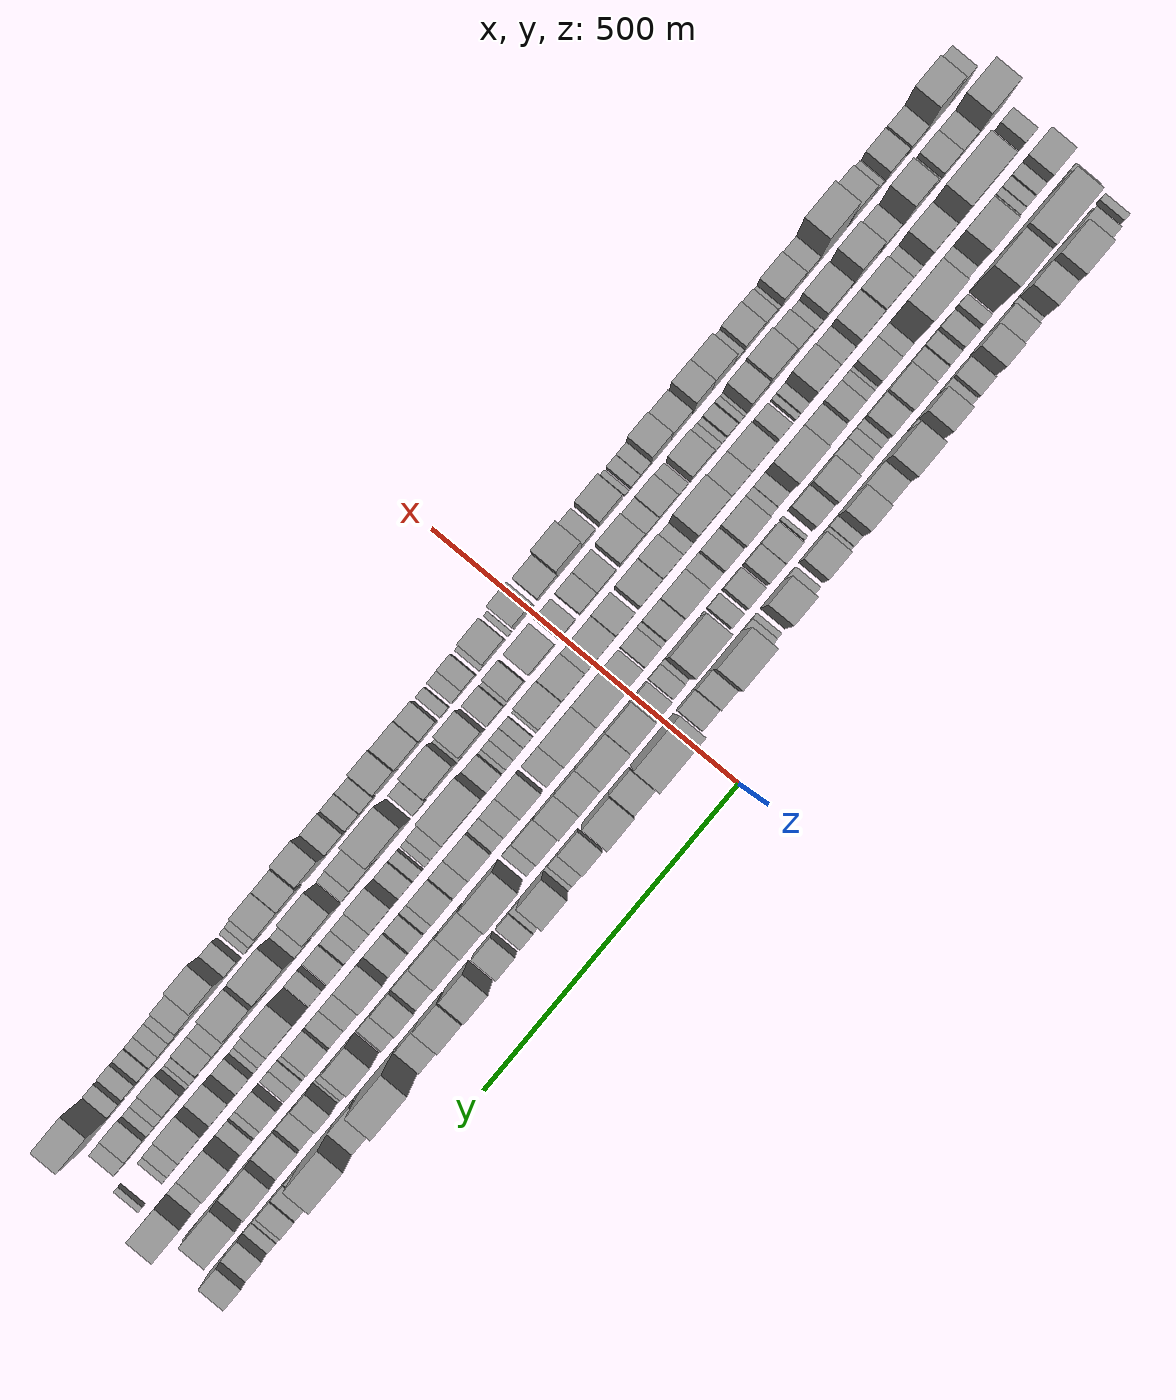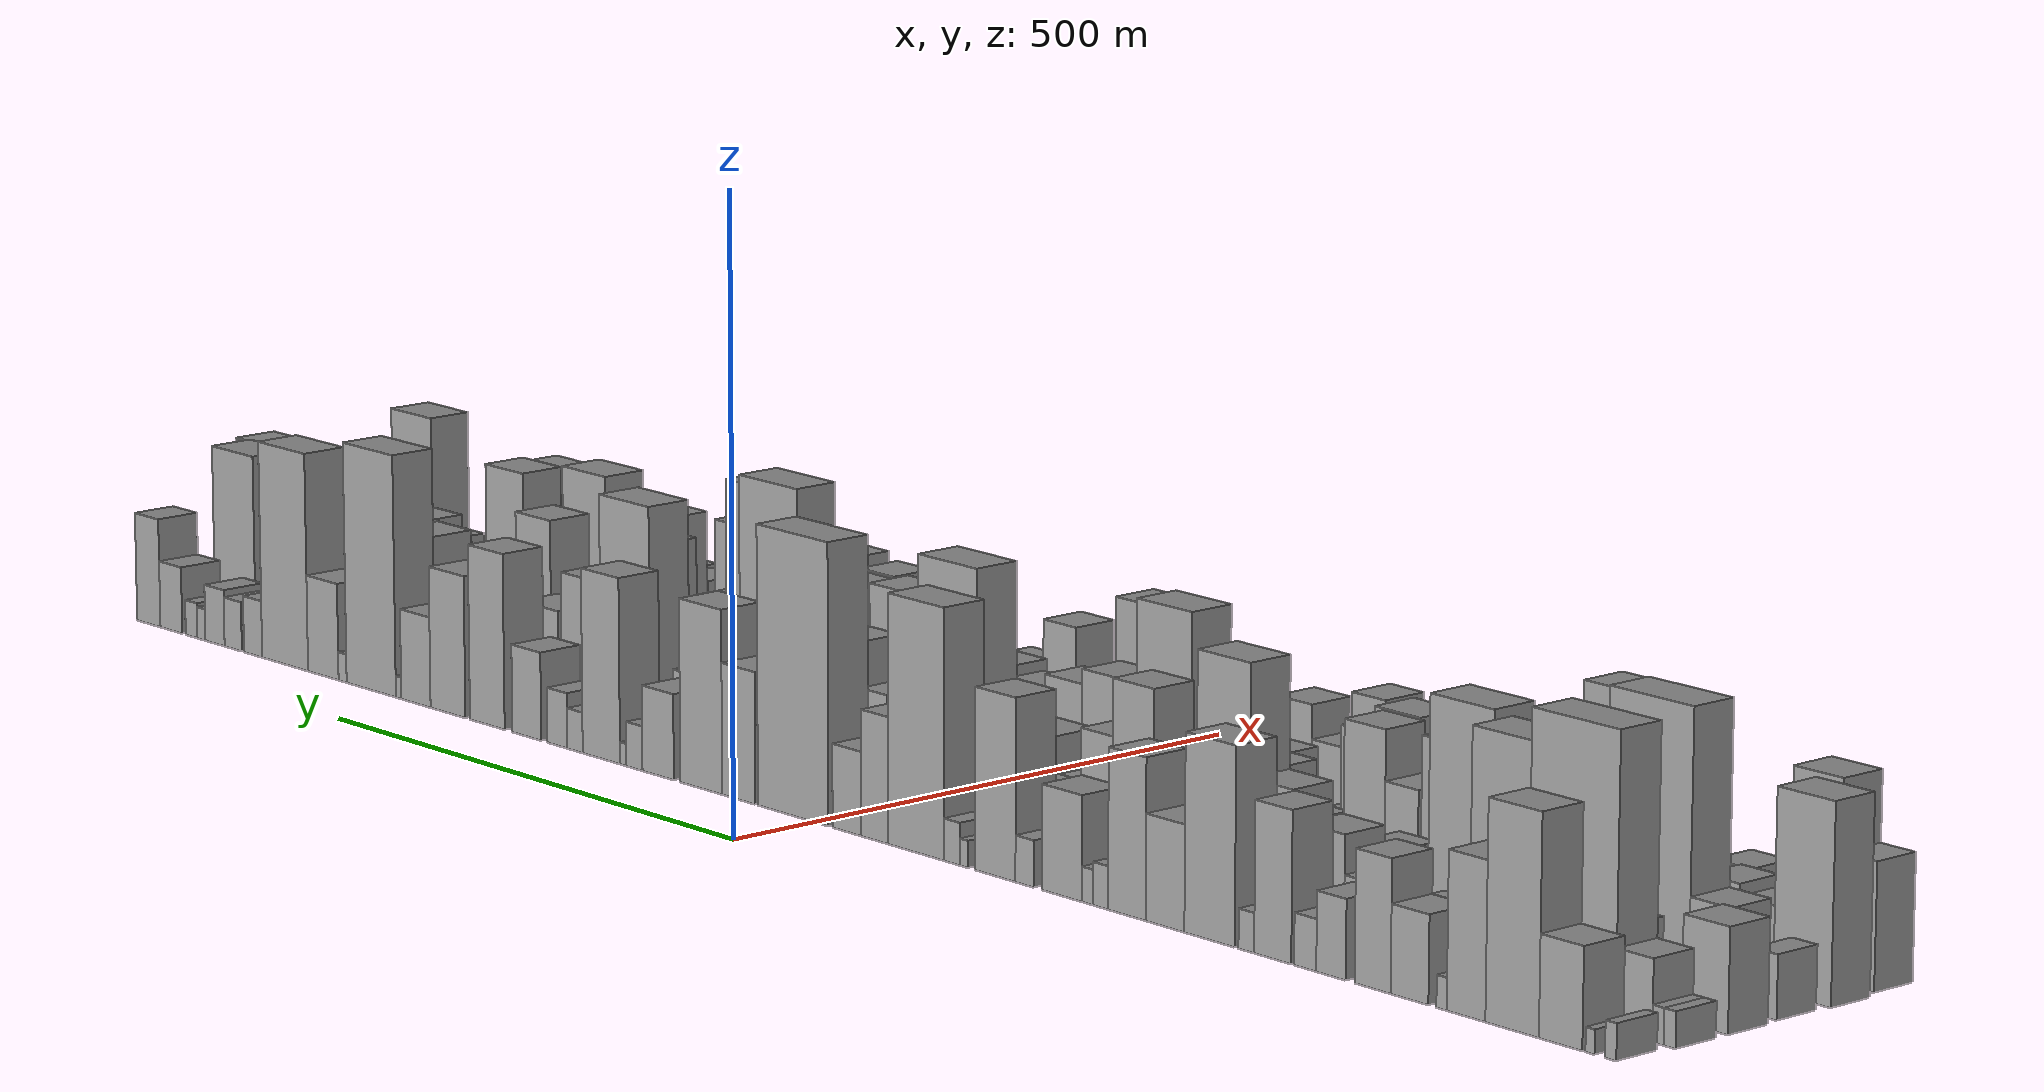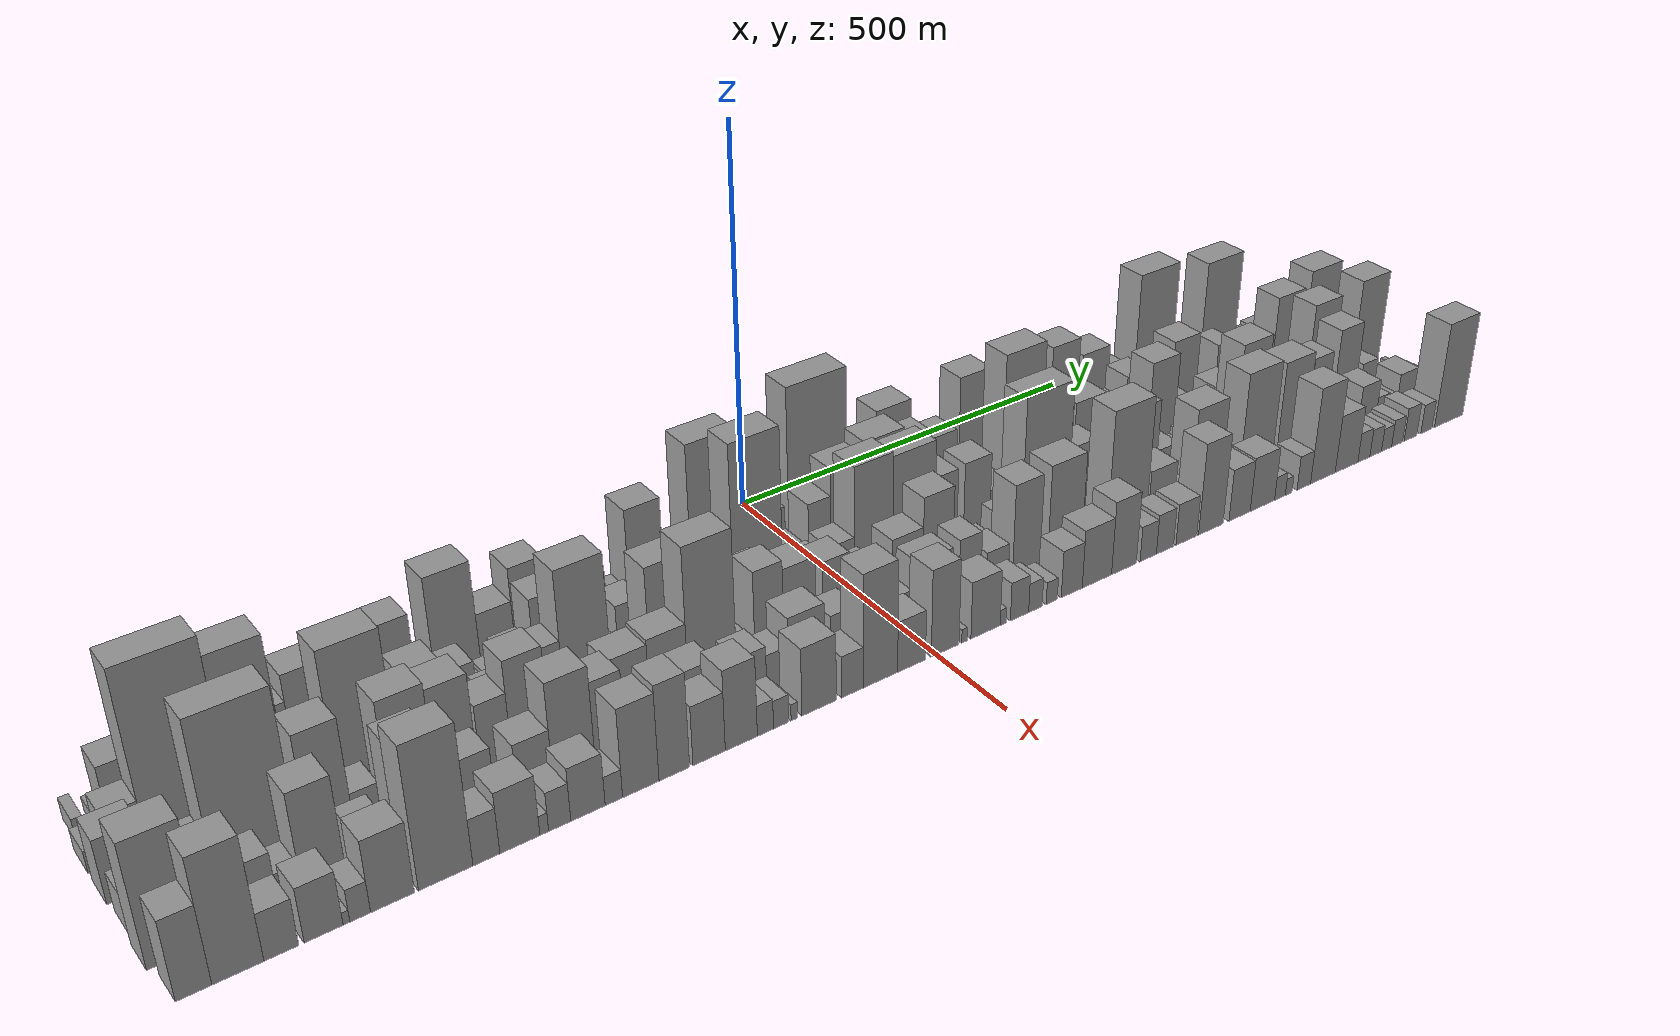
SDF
<sdf version="1.6">
 <world name="default">
  <scene>
   <sky><clouds><speed>12</speed></clouds></sky>
   <ambient>0.4 0.4 0.4 1</ambient>
   <background>0.7 0.7 0.7 1</background>
   <shadows>1</shadows>
  </scene>
  <gravity>0 0 -9.8066</gravity>
  <magnetic_field>6e-06 2.3e-05 -4.2e-05</magnetic_field>
  <physics default="0" name="default_physics" type="ode">
   <ode>
    <solver>
     <type>quick</type>
     <iters>10</iters>
     <sor>1.0</sor>
     <use_dynamic_moi_rescaling>0</use_dynamic_moi_rescaling>
    </solver>
    <constraints>
     <cfm>0</cfm>
     <erp>0.2</erp>
     <contact_max_correcting_vel>100</contact_max_correcting_vel>
     <contact_surface_layer>0.001</contact_surface_layer>
    </constraints>
   </ode>
   <max_step_size>0.004</max_step_size>
   <real_time_factor>1</real_time_factor>
   <real_time_update_rate>250</real_time_update_rate>
  </physics>
  <light name="sun" type="directional">
   <pose>0 0 10 0 0 0</pose>
   <diffuse>0.8 0.8 0.8 1</diffuse>
   <specular>0.2 0.2 0.2 1</specular>
   <attenuation>
    <range>1000</range>
    <constant>0.9</constant>
    <linear>0.01</linear>
    <quadratic>0.001</quadratic>
   </attenuation>
   <direction>-0.5 0.1 -0.9</direction>
  </light>
  <model name="building_1">
   <static>1</static>
   <pose>100.0000 -848.5765 0 0.000000 0.000000 0.000000</pose>
   <link name="link">
    <pose>0 0 13.50 0 0 0</pose>
    <collision name="collision"><geometry><box><size>40.0000 10.8470 27.0000</size></box></geometry></collision>
    <visual name="visual">
     <cast_shadows>0</cast_shadows>
     <geometry><box><size>40.0000 10.8470 27.0000</size></box></geometry>
     <material>
      <script>
       <uri>model://grey_wall/materials/scripts</uri>
       <uri>model://grey_wall/materials/textures</uri>
       <name>vrc/grey_wall</name>
      </script>
     </material>
    </visual>
   </link>
  </model>
  <model name="building_2">
   <static>1</static>
   <pose>100.0000 -828.7338 0 0.000000 0.000000 0.000000</pose>
   <link name="link">
    <pose>0 0 9.00 0 0 0</pose>
    <collision name="collision"><geometry><box><size>40.0000 8.8384 18.0000</size></box></geometry></collision>
    <visual name="visual">
     <cast_shadows>0</cast_shadows>
     <geometry><box><size>40.0000 8.8384 18.0000</size></box></geometry>
     <material>
      <script>
       <uri>model://grey_wall/materials/scripts</uri>
       <uri>model://grey_wall/materials/textures</uri>
       <name>vrc/grey_wall</name>
      </script>
     </material>
    </visual>
   </link>
  </model>
  <model name="building_3">
   <static>1</static>
   <pose>100.0000 -800.2279 0 0.000000 0.000000 0.000000</pose>
   <link name="link">
    <pose>0 0 37.50 0 0 0</pose>
    <collision name="collision"><geometry><box><size>40.0000 42.1734 75.0000</size></box></geometry></collision>
    <visual name="visual">
     <cast_shadows>0</cast_shadows>
     <geometry><box><size>40.0000 42.1734 75.0000</size></box></geometry>
     <material>
      <script>
       <uri>model://grey_wall/materials/scripts</uri>
       <uri>model://grey_wall/materials/textures</uri>
       <name>vrc/grey_wall</name>
      </script>
     </material>
    </visual>
   </link>
  </model>
  <model name="building_4">
   <static>1</static>
   <pose>100.0000 -752.8294 0 0.000000 0.000000 0.000000</pose>
   <link name="link">
    <pose>0 0 81.00 0 0 0</pose>
    <collision name="collision"><geometry><box><size>40.0000 52.6236 162.0000</size></box></geometry></collision>
    <visual name="visual">
     <cast_shadows>0</cast_shadows>
     <geometry><box><size>40.0000 52.6236 162.0000</size></box></geometry>
     <material>
      <script>
       <uri>model://grey_wall/materials/scripts</uri>
       <uri>model://grey_wall/materials/textures</uri>
       <name>vrc/grey_wall</name>
      </script>
     </material>
    </visual>
   </link>
  </model>
  <model name="building_5">
   <static>1</static>
   <pose>100.0000 -707.2681 0 0.000000 0.000000 0.000000</pose>
   <link name="link">
    <pose>0 0 58.50 0 0 0</pose>
    <collision name="collision"><geometry><box><size>40.0000 38.4989 117.0000</size></box></geometry></collision>
    <visual name="visual">
     <cast_shadows>0</cast_shadows>
     <geometry><box><size>40.0000 38.4989 117.0000</size></box></geometry>
     <material>
      <script>
       <uri>model://grey_wall/materials/scripts</uri>
       <uri>model://grey_wall/materials/textures</uri>
       <name>vrc/grey_wall</name>
      </script>
     </material>
    </visual>
   </link>
  </model>
  <model name="building_6">
   <static>1</static>
   <pose>100.0000 -682.8651 0 0.000000 0.000000 0.000000</pose>
   <link name="link">
    <pose>0 0 12.00 0 0 0</pose>
    <collision name="collision"><geometry><box><size>40.0000 10.3071 24.0000</size></box></geometry></collision>
    <visual name="visual">
     <cast_shadows>0</cast_shadows>
     <geometry><box><size>40.0000 10.3071 24.0000</size></box></geometry>
     <material>
      <script>
       <uri>model://grey_wall/materials/scripts</uri>
       <uri>model://grey_wall/materials/textures</uri>
       <name>vrc/grey_wall</name>
      </script>
     </material>
    </visual>
   </link>
  </model>
  <model name="building_7">
   <static>1</static>
   <pose>100.0000 -650.5858 0 0.000000 0.000000 0.000000</pose>
   <link name="link">
    <pose>0 0 33.00 0 0 0</pose>
    <collision name="collision"><geometry><box><size>40.0000 38.2516 66.0000</size></box></geometry></collision>
    <visual name="visual">
     <cast_shadows>0</cast_shadows>
     <geometry><box><size>40.0000 38.2516 66.0000</size></box></geometry>
     <material>
      <script>
       <uri>model://grey_wall/materials/scripts</uri>
       <uri>model://grey_wall/materials/textures</uri>
       <name>vrc/grey_wall</name>
      </script>
     </material>
    </visual>
   </link>
  </model>
  <model name="building_8">
   <static>1</static>
   <pose>100.0000 -613.0949 0 0.000000 0.000000 0.000000</pose>
   <link name="link">
    <pose>0 0 49.50 0 0 0</pose>
    <collision name="collision"><geometry><box><size>40.0000 36.7302 99.0000</size></box></geometry></collision>
    <visual name="visual">
     <cast_shadows>0</cast_shadows>
     <geometry><box><size>40.0000 36.7302 99.0000</size></box></geometry>
     <material>
      <script>
       <uri>model://grey_wall/materials/scripts</uri>
       <uri>model://grey_wall/materials/textures</uri>
       <name>vrc/grey_wall</name>
      </script>
     </material>
    </visual>
   </link>
  </model>
  <model name="building_9">
   <static>1</static>
   <pose>100.0000 -570.5289 0 0.000000 0.000000 0.000000</pose>
   <link name="link">
    <pose>0 0 30.00 0 0 0</pose>
    <collision name="collision"><geometry><box><size>40.0000 30.4017 60.0000</size></box></geometry></collision>
    <visual name="visual">
     <cast_shadows>0</cast_shadows>
     <geometry><box><size>40.0000 30.4017 60.0000</size></box></geometry>
     <material>
      <script>
       <uri>model://grey_wall/materials/scripts</uri>
       <uri>model://grey_wall/materials/textures</uri>
       <name>vrc/grey_wall</name>
      </script>
     </material>
    </visual>
   </link>
  </model>
  <model name="building_10">
   <static>1</static>
   <pose>100.0000 -543.8364 0 0.000000 0.000000 0.000000</pose>
   <link name="link">
    <pose>0 0 19.50 0 0 0</pose>
    <collision name="collision"><geometry><box><size>40.0000 22.9834 39.0000</size></box></geometry></collision>
    <visual name="visual">
     <cast_shadows>0</cast_shadows>
     <geometry><box><size>40.0000 22.9834 39.0000</size></box></geometry>
     <material>
      <script>
       <uri>model://grey_wall/materials/scripts</uri>
       <uri>model://grey_wall/materials/textures</uri>
       <name>vrc/grey_wall</name>
      </script>
     </material>
    </visual>
   </link>
  </model>
  <model name="building_11">
   <static>1</static>
   <pose>100.0000 -509.9247 0 0.000000 0.000000 0.000000</pose>
   <link name="link">
    <pose>0 0 57.00 0 0 0</pose>
    <collision name="collision"><geometry><box><size>40.0000 38.8399 114.0000</size></box></geometry></collision>
    <visual name="visual">
     <cast_shadows>0</cast_shadows>
     <geometry><box><size>40.0000 38.8399 114.0000</size></box></geometry>
     <material>
      <script>
       <uri>model://grey_wall/materials/scripts</uri>
       <uri>model://grey_wall/materials/textures</uri>
       <name>vrc/grey_wall</name>
      </script>
     </material>
    </visual>
   </link>
  </model>
  <model name="building_12">
   <static>1</static>
   <pose>100.0000 -482.2226 0 0.000000 0.000000 0.000000</pose>
   <link name="link">
    <pose>0 0 15.00 0 0 0</pose>
    <collision name="collision"><geometry><box><size>40.0000 16.5643 30.0000</size></box></geometry></collision>
    <visual name="visual">
     <cast_shadows>0</cast_shadows>
     <geometry><box><size>40.0000 16.5643 30.0000</size></box></geometry>
     <material>
      <script>
       <uri>model://grey_wall/materials/scripts</uri>
       <uri>model://grey_wall/materials/textures</uri>
       <name>vrc/grey_wall</name>
      </script>
     </material>
    </visual>
   </link>
  </model>
  <model name="building_13">
   <static>1</static>
   <pose>100.0000 -443.1497 0 0.000000 0.000000 0.000000</pose>
   <link name="link">
    <pose>0 0 75.00 0 0 0</pose>
    <collision name="collision"><geometry><box><size>40.0000 53.5817 150.0000</size></box></geometry></collision>
    <visual name="visual">
     <cast_shadows>0</cast_shadows>
     <geometry><box><size>40.0000 53.5817 150.0000</size></box></geometry>
     <material>
      <script>
       <uri>model://grey_wall/materials/scripts</uri>
       <uri>model://grey_wall/materials/textures</uri>
       <name>vrc/grey_wall</name>
      </script>
     </material>
    </visual>
   </link>
  </model>
  <model name="building_14">
   <static>1</static>
   <pose>100.0000 -395.4743 0 0.000000 0.000000 0.000000</pose>
   <link name="link">
    <pose>0 0 40.50 0 0 0</pose>
    <collision name="collision"><geometry><box><size>40.0000 41.7689 81.0000</size></box></geometry></collision>
    <visual name="visual">
     <cast_shadows>0</cast_shadows>
     <geometry><box><size>40.0000 41.7689 81.0000</size></box></geometry>
     <material>
      <script>
       <uri>model://grey_wall/materials/scripts</uri>
       <uri>model://grey_wall/materials/textures</uri>
       <name>vrc/grey_wall</name>
      </script>
     </material>
    </visual>
   </link>
  </model>
  <model name="building_15">
   <static>1</static>
   <pose>100.0000 -354.0958 0 0.000000 0.000000 0.000000</pose>
   <link name="link">
    <pose>0 0 61.50 0 0 0</pose>
    <collision name="collision"><geometry><box><size>40.0000 40.9882 123.0000</size></box></geometry></collision>
    <visual name="visual">
     <cast_shadows>0</cast_shadows>
     <geometry><box><size>40.0000 40.9882 123.0000</size></box></geometry>
     <material>
      <script>
       <uri>model://grey_wall/materials/scripts</uri>
       <uri>model://grey_wall/materials/textures</uri>
       <name>vrc/grey_wall</name>
      </script>
     </material>
    </visual>
   </link>
  </model>
  <model name="building_16">
   <static>1</static>
   <pose>100.0000 -325.2391 0 0.000000 0.000000 0.000000</pose>
   <link name="link">
    <pose>0 0 16.50 0 0 0</pose>
    <collision name="collision"><geometry><box><size>40.0000 16.7252 33.0000</size></box></geometry></collision>
    <visual name="visual">
     <cast_shadows>0</cast_shadows>
     <geometry><box><size>40.0000 16.7252 33.0000</size></box></geometry>
     <material>
      <script>
       <uri>model://grey_wall/materials/scripts</uri>
       <uri>model://grey_wall/materials/textures</uri>
       <name>vrc/grey_wall</name>
      </script>
     </material>
    </visual>
   </link>
  </model>
  <model name="building_17">
   <static>1</static>
   <pose>100.0000 -310.9203 0 0.000000 0.000000 0.000000</pose>
   <link name="link">
    <pose>0 0 13.50 0 0 0</pose>
    <collision name="collision"><geometry><box><size>40.0000 11.9123 27.0000</size></box></geometry></collision>
    <visual name="visual">
     <cast_shadows>0</cast_shadows>
     <geometry><box><size>40.0000 11.9123 27.0000</size></box></geometry>
     <material>
      <script>
       <uri>model://grey_wall/materials/scripts</uri>
       <uri>model://grey_wall/materials/textures</uri>
       <name>vrc/grey_wall</name>
      </script>
     </material>
    </visual>
   </link>
  </model>
  <model name="building_18">
   <static>1</static>
   <pose>100.0000 -282.7049 0 0.000000 0.000000 0.000000</pose>
   <link name="link">
    <pose>0 0 40.50 0 0 0</pose>
    <collision name="collision"><geometry><box><size>40.0000 44.5185 81.0000</size></box></geometry></collision>
    <visual name="visual">
     <cast_shadows>0</cast_shadows>
     <geometry><box><size>40.0000 44.5185 81.0000</size></box></geometry>
     <material>
      <script>
       <uri>model://grey_wall/materials/scripts</uri>
       <uri>model://grey_wall/materials/textures</uri>
       <name>vrc/grey_wall</name>
      </script>
     </material>
    </visual>
   </link>
  </model>
  <model name="building_19">
   <static>1</static>
   <pose>100.0000 -241.1788 0 0.000000 0.000000 0.000000</pose>
   <link name="link">
    <pose>0 0 18.00 0 0 0</pose>
    <collision name="collision"><geometry><box><size>40.0000 20.5336 36.0000</size></box></geometry></collision>
    <visual name="visual">
     <cast_shadows>0</cast_shadows>
     <geometry><box><size>40.0000 20.5336 36.0000</size></box></geometry>
     <material>
      <script>
       <uri>model://grey_wall/materials/scripts</uri>
       <uri>model://grey_wall/materials/textures</uri>
       <name>vrc/grey_wall</name>
      </script>
     </material>
    </visual>
   </link>
  </model>
  <model name="building_20">
   <static>1</static>
   <pose>100.0000 -208.2263 0 0.000000 0.000000 0.000000</pose>
   <link name="link">
    <pose>0 0 70.50 0 0 0</pose>
    <collision name="collision"><geometry><box><size>40.0000 45.3715 141.0000</size></box></geometry></collision>
    <visual name="visual">
     <cast_shadows>0</cast_shadows>
     <geometry><box><size>40.0000 45.3715 141.0000</size></box></geometry>
     <material>
      <script>
       <uri>model://grey_wall/materials/scripts</uri>
       <uri>model://grey_wall/materials/textures</uri>
       <name>vrc/grey_wall</name>
      </script>
     </material>
    </visual>
   </link>
  </model>
  <model name="building_21">
   <static>1</static>
   <pose>100.0000 -172.8914 0 0.000000 0.000000 0.000000</pose>
   <link name="link">
    <pose>0 0 10.50 0 0 0</pose>
    <collision name="collision"><geometry><box><size>40.0000 9.2983 21.0000</size></box></geometry></collision>
    <visual name="visual">
     <cast_shadows>0</cast_shadows>
     <geometry><box><size>40.0000 9.2983 21.0000</size></box></geometry>
     <material>
      <script>
       <uri>model://grey_wall/materials/scripts</uri>
       <uri>model://grey_wall/materials/textures</uri>
       <name>vrc/grey_wall</name>
      </script>
     </material>
    </visual>
   </link>
  </model>
  <model name="building_22">
   <static>1</static>
   <pose>100.0000 -159.0187 0 0.000000 0.000000 0.000000</pose>
   <link name="link">
    <pose>0 0 16.50 0 0 0</pose>
    <collision name="collision"><geometry><box><size>40.0000 18.4472 33.0000</size></box></geometry></collision>
    <visual name="visual">
     <cast_shadows>0</cast_shadows>
     <geometry><box><size>40.0000 18.4472 33.0000</size></box></geometry>
     <material>
      <script>
       <uri>model://grey_wall/materials/scripts</uri>
       <uri>model://grey_wall/materials/textures</uri>
       <name>vrc/grey_wall</name>
      </script>
     </material>
    </visual>
   </link>
  </model>
  <model name="building_23">
   <static>1</static>
   <pose>100.0000 -117.4576 0 0.000000 0.000000 0.000000</pose>
   <link name="link">
    <pose>0 0 97.50 0 0 0</pose>
    <collision name="collision"><geometry><box><size>40.0000 64.6749 195.0000</size></box></geometry></collision>
    <visual name="visual">
     <cast_shadows>0</cast_shadows>
     <geometry><box><size>40.0000 64.6749 195.0000</size></box></geometry>
     <material>
      <script>
       <uri>model://grey_wall/materials/scripts</uri>
       <uri>model://grey_wall/materials/textures</uri>
       <name>vrc/grey_wall</name>
      </script>
     </material>
    </visual>
   </link>
  </model>
  <model name="building_24">
   <static>1</static>
   <pose>100.0000 -69.4179 0 0.000000 0.000000 0.000000</pose>
   <link name="link">
    <pose>0 0 49.50 0 0 0</pose>
    <collision name="collision"><geometry><box><size>40.0000 31.4046 99.0000</size></box></geometry></collision>
    <visual name="visual">
     <cast_shadows>0</cast_shadows>
     <geometry><box><size>40.0000 31.4046 99.0000</size></box></geometry>
     <material>
      <script>
       <uri>model://grey_wall/materials/scripts</uri>
       <uri>model://grey_wall/materials/textures</uri>
       <name>vrc/grey_wall</name>
      </script>
     </material>
    </visual>
   </link>
  </model>
  <model name="building_25">
   <static>1</static>
   <pose>100.0000 -36.9194 0 0.000000 0.000000 0.000000</pose>
   <link name="link">
    <pose>0 0 33.00 0 0 0</pose>
    <collision name="collision"><geometry><box><size>40.0000 33.5924 66.0000</size></box></geometry></collision>
    <visual name="visual">
     <cast_shadows>0</cast_shadows>
     <geometry><box><size>40.0000 33.5924 66.0000</size></box></geometry>
     <material>
      <script>
       <uri>model://grey_wall/materials/scripts</uri>
       <uri>model://grey_wall/materials/textures</uri>
       <name>vrc/grey_wall</name>
      </script>
     </material>
    </visual>
   </link>
  </model>
  <model name="building_26">
   <static>1</static>
   <pose>100.0000 27.0300 0 0.000000 0.000000 0.000000</pose>
   <link name="link">
    <pose>0 0 111.00 0 0 0</pose>
    <collision name="collision"><geometry><box><size>40.0000 84.3064 222.0000</size></box></geometry></collision>
    <visual name="visual">
     <cast_shadows>0</cast_shadows>
     <geometry><box><size>40.0000 84.3064 222.0000</size></box></geometry>
     <material>
      <script>
       <uri>model://grey_wall/materials/scripts</uri>
       <uri>model://grey_wall/materials/textures</uri>
       <name>vrc/grey_wall</name>
      </script>
     </material>
    </visual>
   </link>
  </model>
  <model name="building_27">
   <static>1</static>
   <pose>100.0000 92.3756 0 0.000000 0.000000 0.000000</pose>
   <link name="link">
    <pose>0 0 52.50 0 0 0</pose>
    <collision name="collision"><geometry><box><size>40.0000 40.3848 105.0000</size></box></geometry></collision>
    <visual name="visual">
     <cast_shadows>0</cast_shadows>
     <geometry><box><size>40.0000 40.3848 105.0000</size></box></geometry>
     <material>
      <script>
       <uri>model://grey_wall/materials/scripts</uri>
       <uri>model://grey_wall/materials/textures</uri>
       <name>vrc/grey_wall</name>
      </script>
     </material>
    </visual>
   </link>
  </model>
  <model name="building_28">
   <static>1</static>
   <pose>100.0000 138.3007 0 0.000000 0.000000 0.000000</pose>
   <link name="link">
    <pose>0 0 73.50 0 0 0</pose>
    <collision name="collision"><geometry><box><size>40.0000 51.4654 147.0000</size></box></geometry></collision>
    <visual name="visual">
     <cast_shadows>0</cast_shadows>
     <geometry><box><size>40.0000 51.4654 147.0000</size></box></geometry>
     <material>
      <script>
       <uri>model://grey_wall/materials/scripts</uri>
       <uri>model://grey_wall/materials/textures</uri>
       <name>vrc/grey_wall</name>
      </script>
     </material>
    </visual>
   </link>
  </model>
  <model name="building_29">
   <static>1</static>
   <pose>100.0000 191.5343 0 0.000000 0.000000 0.000000</pose>
   <link name="link">
    <pose>0 0 34.50 0 0 0</pose>
    <collision name="collision"><geometry><box><size>40.0000 39.0017 69.0000</size></box></geometry></collision>
    <visual name="visual">
     <cast_shadows>0</cast_shadows>
     <geometry><box><size>40.0000 39.0017 69.0000</size></box></geometry>
     <material>
      <script>
       <uri>model://grey_wall/materials/scripts</uri>
       <uri>model://grey_wall/materials/textures</uri>
       <name>vrc/grey_wall</name>
      </script>
     </material>
    </visual>
   </link>
  </model>
  <model name="building_30">
   <static>1</static>
   <pose>100.0000 221.0923 0 0.000000 0.000000 0.000000</pose>
   <link name="link">
    <pose>0 0 18.00 0 0 0</pose>
    <collision name="collision"><geometry><box><size>40.0000 20.1144 36.0000</size></box></geometry></collision>
    <visual name="visual">
     <cast_shadows>0</cast_shadows>
     <geometry><box><size>40.0000 20.1144 36.0000</size></box></geometry>
     <material>
      <script>
       <uri>model://grey_wall/materials/scripts</uri>
       <uri>model://grey_wall/materials/textures</uri>
       <name>vrc/grey_wall</name>
      </script>
     </material>
    </visual>
   </link>
  </model>
  <model name="building_31">
   <static>1</static>
   <pose>100.0000 235.1445 0 0.000000 0.000000 0.000000</pose>
   <link name="link">
    <pose>0 0 9.00 0 0 0</pose>
    <collision name="collision"><geometry><box><size>40.0000 7.9899 18.0000</size></box></geometry></collision>
    <visual name="visual">
     <cast_shadows>0</cast_shadows>
     <geometry><box><size>40.0000 7.9899 18.0000</size></box></geometry>
     <material>
      <script>
       <uri>model://grey_wall/materials/scripts</uri>
       <uri>model://grey_wall/materials/textures</uri>
       <name>vrc/grey_wall</name>
      </script>
     </material>
    </visual>
   </link>
  </model>
  <model name="building_32">
   <static>1</static>
   <pose>100.0000 262.7844 0 0.000000 0.000000 0.000000</pose>
   <link name="link">
    <pose>0 0 75.00 0 0 0</pose>
    <collision name="collision"><geometry><box><size>40.0000 47.2899 150.0000</size></box></geometry></collision>
    <visual name="visual">
     <cast_shadows>0</cast_shadows>
     <geometry><box><size>40.0000 47.2899 150.0000</size></box></geometry>
     <material>
      <script>
       <uri>model://grey_wall/materials/scripts</uri>
       <uri>model://grey_wall/materials/textures</uri>
       <name>vrc/grey_wall</name>
      </script>
     </material>
    </visual>
   </link>
  </model>
  <model name="building_33">
   <static>1</static>
   <pose>100.0000 296.3072 0 0.000000 0.000000 0.000000</pose>
   <link name="link">
    <pose>0 0 16.50 0 0 0</pose>
    <collision name="collision"><geometry><box><size>40.0000 19.7557 33.0000</size></box></geometry></collision>
    <visual name="visual">
     <cast_shadows>0</cast_shadows>
     <geometry><box><size>40.0000 19.7557 33.0000</size></box></geometry>
     <material>
      <script>
       <uri>model://grey_wall/materials/scripts</uri>
       <uri>model://grey_wall/materials/textures</uri>
       <name>vrc/grey_wall</name>
      </script>
     </material>
    </visual>
   </link>
  </model>
  <model name="building_34">
   <static>1</static>
   <pose>100.0000 318.8249 0 0.000000 0.000000 0.000000</pose>
   <link name="link">
    <pose>0 0 22.50 0 0 0</pose>
    <collision name="collision"><geometry><box><size>40.0000 25.2797 45.0000</size></box></geometry></collision>
    <visual name="visual">
     <cast_shadows>0</cast_shadows>
     <geometry><box><size>40.0000 25.2797 45.0000</size></box></geometry>
     <material>
      <script>
       <uri>model://grey_wall/materials/scripts</uri>
       <uri>model://grey_wall/materials/textures</uri>
       <name>vrc/grey_wall</name>
      </script>
     </material>
    </visual>
   </link>
  </model>
  <model name="building_35">
   <static>1</static>
   <pose>100.0000 358.1424 0 0.000000 0.000000 0.000000</pose>
   <link name="link">
    <pose>0 0 36.00 0 0 0</pose>
    <collision name="collision"><geometry><box><size>40.0000 37.3553 72.0000</size></box></geometry></collision>
    <visual name="visual">
     <cast_shadows>0</cast_shadows>
     <geometry><box><size>40.0000 37.3553 72.0000</size></box></geometry>
     <material>
      <script>
       <uri>model://grey_wall/materials/scripts</uri>
       <uri>model://grey_wall/materials/textures</uri>
       <name>vrc/grey_wall</name>
      </script>
     </material>
    </visual>
   </link>
  </model>
  <model name="building_36">
   <static>1</static>
   <pose>100.0000 409.5128 0 0.000000 0.000000 0.000000</pose>
   <link name="link">
    <pose>0 0 72.00 0 0 0</pose>
    <collision name="collision"><geometry><box><size>40.0000 45.3855 144.0000</size></box></geometry></collision>
    <visual name="visual">
     <cast_shadows>0</cast_shadows>
     <geometry><box><size>40.0000 45.3855 144.0000</size></box></geometry>
     <material>
      <script>
       <uri>model://grey_wall/materials/scripts</uri>
       <uri>model://grey_wall/materials/textures</uri>
       <name>vrc/grey_wall</name>
      </script>
     </material>
    </visual>
   </link>
  </model>
  <model name="building_37">
   <static>1</static>
   <pose>100.0000 461.2926 0 0.000000 0.000000 0.000000</pose>
   <link name="link">
    <pose>0 0 58.50 0 0 0</pose>
    <collision name="collision"><geometry><box><size>40.0000 46.1740 117.0000</size></box></geometry></collision>
    <visual name="visual">
     <cast_shadows>0</cast_shadows>
     <geometry><box><size>40.0000 46.1740 117.0000</size></box></geometry>
     <material>
      <script>
       <uri>model://grey_wall/materials/scripts</uri>
       <uri>model://grey_wall/materials/textures</uri>
       <name>vrc/grey_wall</name>
      </script>
     </material>
    </visual>
   </link>
  </model>
  <model name="building_38">
   <static>1</static>
   <pose>100.0000 503.9685 0 0.000000 0.000000 0.000000</pose>
   <link name="link">
    <pose>0 0 37.50 0 0 0</pose>
    <collision name="collision"><geometry><box><size>40.0000 39.1779 75.0000</size></box></geometry></collision>
    <visual name="visual">
     <cast_shadows>0</cast_shadows>
     <geometry><box><size>40.0000 39.1779 75.0000</size></box></geometry>
     <material>
      <script>
       <uri>model://grey_wall/materials/scripts</uri>
       <uri>model://grey_wall/materials/textures</uri>
       <name>vrc/grey_wall</name>
      </script>
     </material>
    </visual>
   </link>
  </model>
  <model name="building_39">
   <static>1</static>
   <pose>100.0000 527.1681 0 0.000000 0.000000 0.000000</pose>
   <link name="link">
    <pose>0 0 9.00 0 0 0</pose>
    <collision name="collision"><geometry><box><size>40.0000 7.2214 18.0000</size></box></geometry></collision>
    <visual name="visual">
     <cast_shadows>0</cast_shadows>
     <geometry><box><size>40.0000 7.2214 18.0000</size></box></geometry>
     <material>
      <script>
       <uri>model://grey_wall/materials/scripts</uri>
       <uri>model://grey_wall/materials/textures</uri>
       <name>vrc/grey_wall</name>
      </script>
     </material>
    </visual>
   </link>
  </model>
  <model name="building_40">
   <static>1</static>
   <pose>100.0000 564.1771 0 0.000000 0.000000 0.000000</pose>
   <link name="link">
    <pose>0 0 100.50 0 0 0</pose>
    <collision name="collision"><geometry><box><size>40.0000 66.7965 201.0000</size></box></geometry></collision>
    <visual name="visual">
     <cast_shadows>0</cast_shadows>
     <geometry><box><size>40.0000 66.7965 201.0000</size></box></geometry>
     <material>
      <script>
       <uri>model://grey_wall/materials/scripts</uri>
       <uri>model://grey_wall/materials/textures</uri>
       <name>vrc/grey_wall</name>
      </script>
     </material>
    </visual>
   </link>
  </model>
  <model name="building_41">
   <static>1</static>
   <pose>100.0000 603.0880 0 0.000000 0.000000 0.000000</pose>
   <link name="link">
    <pose>0 0 12.00 0 0 0</pose>
    <collision name="collision"><geometry><box><size>40.0000 11.0255 24.0000</size></box></geometry></collision>
    <visual name="visual">
     <cast_shadows>0</cast_shadows>
     <geometry><box><size>40.0000 11.0255 24.0000</size></box></geometry>
     <material>
      <script>
       <uri>model://grey_wall/materials/scripts</uri>
       <uri>model://grey_wall/materials/textures</uri>
       <name>vrc/grey_wall</name>
      </script>
     </material>
    </visual>
   </link>
  </model>
  <model name="building_42">
   <static>1</static>
   <pose>100.0000 629.5832 0 0.000000 0.000000 0.000000</pose>
   <link name="link">
    <pose>0 0 40.50 0 0 0</pose>
    <collision name="collision"><geometry><box><size>40.0000 41.9648 81.0000</size></box></geometry></collision>
    <visual name="visual">
     <cast_shadows>0</cast_shadows>
     <geometry><box><size>40.0000 41.9648 81.0000</size></box></geometry>
     <material>
      <script>
       <uri>model://grey_wall/materials/scripts</uri>
       <uri>model://grey_wall/materials/textures</uri>
       <name>vrc/grey_wall</name>
      </script>
     </material>
    </visual>
   </link>
  </model>
  <model name="building_43">
   <static>1</static>
   <pose>100.0000 682.4977 0 0.000000 0.000000 0.000000</pose>
   <link name="link">
    <pose>0 0 91.50 0 0 0</pose>
    <collision name="collision"><geometry><box><size>40.0000 63.8643 183.0000</size></box></geometry></collision>
    <visual name="visual">
     <cast_shadows>0</cast_shadows>
     <geometry><box><size>40.0000 63.8643 183.0000</size></box></geometry>
     <material>
      <script>
       <uri>model://grey_wall/materials/scripts</uri>
       <uri>model://grey_wall/materials/textures</uri>
       <name>vrc/grey_wall</name>
      </script>
     </material>
    </visual>
   </link>
  </model>
  <model name="building_44">
   <static>1</static>
   <pose>100.0000 727.2137 0 0.000000 0.000000 0.000000</pose>
   <link name="link">
    <pose>0 0 24.00 0 0 0</pose>
    <collision name="collision"><geometry><box><size>40.0000 25.5676 48.0000</size></box></geometry></collision>
    <visual name="visual">
     <cast_shadows>0</cast_shadows>
     <geometry><box><size>40.0000 25.5676 48.0000</size></box></geometry>
     <material>
      <script>
       <uri>model://grey_wall/materials/scripts</uri>
       <uri>model://grey_wall/materials/textures</uri>
       <name>vrc/grey_wall</name>
      </script>
     </material>
    </visual>
   </link>
  </model>
  <model name="building_45">
   <static>1</static>
   <pose>100.0000 755.2027 0 0.000000 0.000000 0.000000</pose>
   <link name="link">
    <pose>0 0 21.00 0 0 0</pose>
    <collision name="collision"><geometry><box><size>40.0000 24.4103 42.0000</size></box></geometry></collision>
    <visual name="visual">
     <cast_shadows>0</cast_shadows>
     <geometry><box><size>40.0000 24.4103 42.0000</size></box></geometry>
     <material>
      <script>
       <uri>model://grey_wall/materials/scripts</uri>
       <uri>model://grey_wall/materials/textures</uri>
       <name>vrc/grey_wall</name>
      </script>
     </material>
    </visual>
   </link>
  </model>
  <model name="building_46">
   <static>1</static>
   <pose>100.0000 781.0198 0 0.000000 0.000000 0.000000</pose>
   <link name="link">
    <pose>0 0 24.00 0 0 0</pose>
    <collision name="collision"><geometry><box><size>40.0000 27.2238 48.0000</size></box></geometry></collision>
    <visual name="visual">
     <cast_shadows>0</cast_shadows>
     <geometry><box><size>40.0000 27.2238 48.0000</size></box></geometry>
     <material>
      <script>
       <uri>model://grey_wall/materials/scripts</uri>
       <uri>model://grey_wall/materials/textures</uri>
       <name>vrc/grey_wall</name>
      </script>
     </material>
    </visual>
   </link>
  </model>
  <model name="building_47">
   <static>1</static>
   <pose>100.0000 800.3793 0 0.000000 0.000000 0.000000</pose>
   <link name="link">
    <pose>0 0 13.50 0 0 0</pose>
    <collision name="collision"><geometry><box><size>40.0000 11.4953 27.0000</size></box></geometry></collision>
    <visual name="visual">
     <cast_shadows>0</cast_shadows>
     <geometry><box><size>40.0000 11.4953 27.0000</size></box></geometry>
     <material>
      <script>
       <uri>model://grey_wall/materials/scripts</uri>
       <uri>model://grey_wall/materials/textures</uri>
       <name>vrc/grey_wall</name>
      </script>
     </material>
    </visual>
   </link>
  </model>
  <model name="building_48">
   <static>1</static>
   <pose>100.0000 814.4550 0 0.000000 0.000000 0.000000</pose>
   <link name="link">
    <pose>0 0 15.00 0 0 0</pose>
    <collision name="collision"><geometry><box><size>40.0000 16.6561 30.0000</size></box></geometry></collision>
    <visual name="visual">
     <cast_shadows>0</cast_shadows>
     <geometry><box><size>40.0000 16.6561 30.0000</size></box></geometry>
     <material>
      <script>
       <uri>model://grey_wall/materials/scripts</uri>
       <uri>model://grey_wall/materials/textures</uri>
       <name>vrc/grey_wall</name>
      </script>
     </material>
    </visual>
   </link>
  </model>
  <model name="building_49">
   <static>1</static>
   <pose>100.0000 843.5239 0 0.000000 0.000000 0.000000</pose>
   <link name="link">
    <pose>0 0 28.50 0 0 0</pose>
    <collision name="collision"><geometry><box><size>40.0000 31.4817 57.0000</size></box></geometry></collision>
    <visual name="visual">
     <cast_shadows>0</cast_shadows>
     <geometry><box><size>40.0000 31.4817 57.0000</size></box></geometry>
     <material>
      <script>
       <uri>model://grey_wall/materials/scripts</uri>
       <uri>model://grey_wall/materials/textures</uri>
       <name>vrc/grey_wall</name>
      </script>
     </material>
    </visual>
   </link>
  </model>
  <model name="building_50">
   <static>1</static>
   <pose>100.0000 876.1330 0 0.000000 0.000000 0.000000</pose>
   <link name="link">
    <pose>0 0 46.50 0 0 0</pose>
    <collision name="collision"><geometry><box><size>40.0000 33.7363 93.0000</size></box></geometry></collision>
    <visual name="visual">
     <cast_shadows>0</cast_shadows>
     <geometry><box><size>40.0000 33.7363 93.0000</size></box></geometry>
     <material>
      <script>
       <uri>model://grey_wall/materials/scripts</uri>
       <uri>model://grey_wall/materials/textures</uri>
       <name>vrc/grey_wall</name>
      </script>
     </material>
    </visual>
   </link>
  </model>
  <model name="building_51">
   <static>1</static>
   <pose>152.0000 -854.2418 0 0.000000 0.000000 0.000000</pose>
   <link name="link">
    <pose>0 0 13.50 0 0 0</pose>
    <collision name="collision"><geometry><box><size>40.0000 11.5164 27.0000</size></box></geometry></collision>
    <visual name="visual">
     <cast_shadows>0</cast_shadows>
     <geometry><box><size>40.0000 11.5164 27.0000</size></box></geometry>
     <material>
      <script>
       <uri>model://grey_wall/materials/scripts</uri>
       <uri>model://grey_wall/materials/textures</uri>
       <name>vrc/grey_wall</name>
      </script>
     </material>
    </visual>
   </link>
  </model>
  <model name="building_52">
   <static>1</static>
   <pose>152.0000 -843.0489 0 0.000000 0.000000 0.000000</pose>
   <link name="link">
    <pose>0 0 13.50 0 0 0</pose>
    <collision name="collision"><geometry><box><size>40.0000 10.8695 27.0000</size></box></geometry></collision>
    <visual name="visual">
     <cast_shadows>0</cast_shadows>
     <geometry><box><size>40.0000 10.8695 27.0000</size></box></geometry>
     <material>
      <script>
       <uri>model://grey_wall/materials/scripts</uri>
       <uri>model://grey_wall/materials/textures</uri>
       <name>vrc/grey_wall</name>
      </script>
     </material>
    </visual>
   </link>
  </model>
  <model name="building_53">
   <static>1</static>
   <pose>152.0000 -819.8886 0 0.000000 0.000000 0.000000</pose>
   <link name="link">
    <pose>0 0 30.00 0 0 0</pose>
    <collision name="collision"><geometry><box><size>40.0000 35.4512 60.0000</size></box></geometry></collision>
    <visual name="visual">
     <cast_shadows>0</cast_shadows>
     <geometry><box><size>40.0000 35.4512 60.0000</size></box></geometry>
     <material>
      <script>
       <uri>model://grey_wall/materials/scripts</uri>
       <uri>model://grey_wall/materials/textures</uri>
       <name>vrc/grey_wall</name>
      </script>
     </material>
    </visual>
   </link>
  </model>
  <model name="building_54">
   <static>1</static>
   <pose>152.0000 -759.0774 0 0.000000 0.000000 0.000000</pose>
   <link name="link">
    <pose>0 0 108.00 0 0 0</pose>
    <collision name="collision"><geometry><box><size>40.0000 86.1711 216.0000</size></box></geometry></collision>
    <visual name="visual">
     <cast_shadows>0</cast_shadows>
     <geometry><box><size>40.0000 86.1711 216.0000</size></box></geometry>
     <material>
      <script>
       <uri>model://grey_wall/materials/scripts</uri>
       <uri>model://grey_wall/materials/textures</uri>
       <name>vrc/grey_wall</name>
      </script>
     </material>
    </visual>
   </link>
  </model>
  <model name="building_55">
   <static>1</static>
   <pose>152.0000 -686.6378 0 0.000000 0.000000 0.000000</pose>
   <link name="link">
    <pose>0 0 96.00 0 0 0</pose>
    <collision name="collision"><geometry><box><size>40.0000 58.7080 192.0000</size></box></geometry></collision>
    <visual name="visual">
     <cast_shadows>0</cast_shadows>
     <geometry><box><size>40.0000 58.7080 192.0000</size></box></geometry>
     <material>
      <script>
       <uri>model://grey_wall/materials/scripts</uri>
       <uri>model://grey_wall/materials/textures</uri>
       <name>vrc/grey_wall</name>
      </script>
     </material>
    </visual>
   </link>
  </model>
  <model name="building_56">
   <static>1</static>
   <pose>152.0000 -638.2827 0 0.000000 0.000000 0.000000</pose>
   <link name="link">
    <pose>0 0 18.00 0 0 0</pose>
    <collision name="collision"><geometry><box><size>40.0000 18.0022 36.0000</size></box></geometry></collision>
    <visual name="visual">
     <cast_shadows>0</cast_shadows>
     <geometry><box><size>40.0000 18.0022 36.0000</size></box></geometry>
     <material>
      <script>
       <uri>model://grey_wall/materials/scripts</uri>
       <uri>model://grey_wall/materials/textures</uri>
       <name>vrc/grey_wall</name>
      </script>
     </material>
    </visual>
   </link>
  </model>
  <model name="building_57">
   <static>1</static>
   <pose>152.0000 -605.1365 0 0.000000 0.000000 0.000000</pose>
   <link name="link">
    <pose>0 0 25.50 0 0 0</pose>
    <collision name="collision"><geometry><box><size>40.0000 28.2901 51.0000</size></box></geometry></collision>
    <visual name="visual">
     <cast_shadows>0</cast_shadows>
     <geometry><box><size>40.0000 28.2901 51.0000</size></box></geometry>
     <material>
      <script>
       <uri>model://grey_wall/materials/scripts</uri>
       <uri>model://grey_wall/materials/textures</uri>
       <name>vrc/grey_wall</name>
      </script>
     </material>
    </visual>
   </link>
  </model>
  <model name="building_58">
   <static>1</static>
   <pose>152.0000 -575.1443 0 0.000000 0.000000 0.000000</pose>
   <link name="link">
    <pose>0 0 22.50 0 0 0</pose>
    <collision name="collision"><geometry><box><size>40.0000 23.6943 45.0000</size></box></geometry></collision>
    <visual name="visual">
     <cast_shadows>0</cast_shadows>
     <geometry><box><size>40.0000 23.6943 45.0000</size></box></geometry>
     <material>
      <script>
       <uri>model://grey_wall/materials/scripts</uri>
       <uri>model://grey_wall/materials/textures</uri>
       <name>vrc/grey_wall</name>
      </script>
     </material>
    </visual>
   </link>
  </model>
  <model name="building_59">
   <static>1</static>
   <pose>152.0000 -544.2333 0 0.000000 0.000000 0.000000</pose>
   <link name="link">
    <pose>0 0 28.50 0 0 0</pose>
    <collision name="collision"><geometry><box><size>40.0000 30.1277 57.0000</size></box></geometry></collision>
    <visual name="visual">
     <cast_shadows>0</cast_shadows>
     <geometry><box><size>40.0000 30.1277 57.0000</size></box></geometry>
     <material>
      <script>
       <uri>model://grey_wall/materials/scripts</uri>
       <uri>model://grey_wall/materials/textures</uri>
       <name>vrc/grey_wall</name>
      </script>
     </material>
    </visual>
   </link>
  </model>
  <model name="building_60">
   <static>1</static>
   <pose>152.0000 -507.1727 0 0.000000 0.000000 0.000000</pose>
   <link name="link">
    <pose>0 0 43.50 0 0 0</pose>
    <collision name="collision"><geometry><box><size>40.0000 43.9935 87.0000</size></box></geometry></collision>
    <visual name="visual">
     <cast_shadows>0</cast_shadows>
     <geometry><box><size>40.0000 43.9935 87.0000</size></box></geometry>
     <material>
      <script>
       <uri>model://grey_wall/materials/scripts</uri>
       <uri>model://grey_wall/materials/textures</uri>
       <name>vrc/grey_wall</name>
      </script>
     </material>
    </visual>
   </link>
  </model>
  <model name="building_61">
   <static>1</static>
   <pose>152.0000 -466.2680 0 0.000000 0.000000 0.000000</pose>
   <link name="link">
    <pose>0 0 33.00 0 0 0</pose>
    <collision name="collision"><geometry><box><size>40.0000 37.8158 66.0000</size></box></geometry></collision>
    <visual name="visual">
     <cast_shadows>0</cast_shadows>
     <geometry><box><size>40.0000 37.8158 66.0000</size></box></geometry>
     <material>
      <script>
       <uri>model://grey_wall/materials/scripts</uri>
       <uri>model://grey_wall/materials/textures</uri>
       <name>vrc/grey_wall</name>
      </script>
     </material>
    </visual>
   </link>
  </model>
  <model name="building_62">
   <static>1</static>
   <pose>152.0000 -439.7051 0 0.000000 0.000000 0.000000</pose>
   <link name="link">
    <pose>0 0 15.00 0 0 0</pose>
    <collision name="collision"><geometry><box><size>40.0000 15.3099 30.0000</size></box></geometry></collision>
    <visual name="visual">
     <cast_shadows>0</cast_shadows>
     <geometry><box><size>40.0000 15.3099 30.0000</size></box></geometry>
     <material>
      <script>
       <uri>model://grey_wall/materials/scripts</uri>
       <uri>model://grey_wall/materials/textures</uri>
       <name>vrc/grey_wall</name>
      </script>
     </material>
    </visual>
   </link>
  </model>
  <model name="building_63">
   <static>1</static>
   <pose>152.0000 -422.1635 0 0.000000 0.000000 0.000000</pose>
   <link name="link">
    <pose>0 0 18.00 0 0 0</pose>
    <collision name="collision"><geometry><box><size>40.0000 19.7733 36.0000</size></box></geometry></collision>
    <visual name="visual">
     <cast_shadows>0</cast_shadows>
     <geometry><box><size>40.0000 19.7733 36.0000</size></box></geometry>
     <material>
      <script>
       <uri>model://grey_wall/materials/scripts</uri>
       <uri>model://grey_wall/materials/textures</uri>
       <name>vrc/grey_wall</name>
      </script>
     </material>
    </visual>
   </link>
  </model>
  <model name="building_64">
   <static>1</static>
   <pose>152.0000 -395.3707 0 0.000000 0.000000 0.000000</pose>
   <link name="link">
    <pose>0 0 28.50 0 0 0</pose>
    <collision name="collision"><geometry><box><size>40.0000 33.8123 57.0000</size></box></geometry></collision>
    <visual name="visual">
     <cast_shadows>0</cast_shadows>
     <geometry><box><size>40.0000 33.8123 57.0000</size></box></geometry>
     <material>
      <script>
       <uri>model://grey_wall/materials/scripts</uri>
       <uri>model://grey_wall/materials/textures</uri>
       <name>vrc/grey_wall</name>
      </script>
     </material>
    </visual>
   </link>
  </model>
  <model name="building_65">
   <static>1</static>
   <pose>152.0000 -357.4929 0 0.000000 0.000000 0.000000</pose>
   <link name="link">
    <pose>0 0 57.00 0 0 0</pose>
    <collision name="collision"><geometry><box><size>40.0000 41.9434 114.0000</size></box></geometry></collision>
    <visual name="visual">
     <cast_shadows>0</cast_shadows>
     <geometry><box><size>40.0000 41.9434 114.0000</size></box></geometry>
     <material>
      <script>
       <uri>model://grey_wall/materials/scripts</uri>
       <uri>model://grey_wall/materials/textures</uri>
       <name>vrc/grey_wall</name>
      </script>
     </material>
    </visual>
   </link>
  </model>
  <model name="building_66">
   <static>1</static>
   <pose>152.0000 -319.0967 0 0.000000 0.000000 0.000000</pose>
   <link name="link">
    <pose>0 0 34.50 0 0 0</pose>
    <collision name="collision"><geometry><box><size>40.0000 34.8489 69.0000</size></box></geometry></collision>
    <visual name="visual">
     <cast_shadows>0</cast_shadows>
     <geometry><box><size>40.0000 34.8489 69.0000</size></box></geometry>
     <material>
      <script>
       <uri>model://grey_wall/materials/scripts</uri>
       <uri>model://grey_wall/materials/textures</uri>
       <name>vrc/grey_wall</name>
      </script>
     </material>
    </visual>
   </link>
  </model>
  <model name="building_67">
   <static>1</static>
   <pose>152.0000 -288.5084 0 0.000000 0.000000 0.000000</pose>
   <link name="link">
    <pose>0 0 7.50 0 0 0</pose>
    <collision name="collision"><geometry><box><size>40.0000 6.3277 15.0000</size></box></geometry></collision>
    <visual name="visual">
     <cast_shadows>0</cast_shadows>
     <geometry><box><size>40.0000 6.3277 15.0000</size></box></geometry>
     <material>
      <script>
       <uri>model://grey_wall/materials/scripts</uri>
       <uri>model://grey_wall/materials/textures</uri>
       <name>vrc/grey_wall</name>
      </script>
     </material>
    </visual>
   </link>
  </model>
  <model name="building_68">
   <static>1</static>
   <pose>152.0000 -260.9938 0 0.000000 0.000000 0.000000</pose>
   <link name="link">
    <pose>0 0 31.50 0 0 0</pose>
    <collision name="collision"><geometry><box><size>40.0000 34.7015 63.0000</size></box></geometry></collision>
    <visual name="visual">
     <cast_shadows>0</cast_shadows>
     <geometry><box><size>40.0000 34.7015 63.0000</size></box></geometry>
     <material>
      <script>
       <uri>model://grey_wall/materials/scripts</uri>
       <uri>model://grey_wall/materials/textures</uri>
       <name>vrc/grey_wall</name>
      </script>
     </material>
    </visual>
   </link>
  </model>
  <model name="building_69">
   <static>1</static>
   <pose>152.0000 -228.0221 0 0.000000 0.000000 0.000000</pose>
   <link name="link">
    <pose>0 0 30.00 0 0 0</pose>
    <collision name="collision"><geometry><box><size>40.0000 31.2420 60.0000</size></box></geometry></collision>
    <visual name="visual">
     <cast_shadows>0</cast_shadows>
     <geometry><box><size>40.0000 31.2420 60.0000</size></box></geometry>
     <material>
      <script>
       <uri>model://grey_wall/materials/scripts</uri>
       <uri>model://grey_wall/materials/textures</uri>
       <name>vrc/grey_wall</name>
      </script>
     </material>
    </visual>
   </link>
  </model>
  <model name="building_70">
   <static>1</static>
   <pose>152.0000 -189.3958 0 0.000000 0.000000 0.000000</pose>
   <link name="link">
    <pose>0 0 28.50 0 0 0</pose>
    <collision name="collision"><geometry><box><size>40.0000 34.0106 57.0000</size></box></geometry></collision>
    <visual name="visual">
     <cast_shadows>0</cast_shadows>
     <geometry><box><size>40.0000 34.0106 57.0000</size></box></geometry>
     <material>
      <script>
       <uri>model://grey_wall/materials/scripts</uri>
       <uri>model://grey_wall/materials/textures</uri>
       <name>vrc/grey_wall</name>
      </script>
     </material>
    </visual>
   </link>
  </model>
  <model name="building_71">
   <static>1</static>
   <pose>152.0000 -153.5193 0 0.000000 0.000000 0.000000</pose>
   <link name="link">
    <pose>0 0 22.50 0 0 0</pose>
    <collision name="collision"><geometry><box><size>40.0000 23.7424 45.0000</size></box></geometry></collision>
    <visual name="visual">
     <cast_shadows>0</cast_shadows>
     <geometry><box><size>40.0000 23.7424 45.0000</size></box></geometry>
     <material>
      <script>
       <uri>model://grey_wall/materials/scripts</uri>
       <uri>model://grey_wall/materials/textures</uri>
       <name>vrc/grey_wall</name>
      </script>
     </material>
    </visual>
   </link>
  </model>
  <model name="building_72">
   <static>1</static>
   <pose>152.0000 -134.0008 0 0.000000 0.000000 0.000000</pose>
   <link name="link">
    <pose>0 0 9.00 0 0 0</pose>
    <collision name="collision"><geometry><box><size>40.0000 7.2945 18.0000</size></box></geometry></collision>
    <visual name="visual">
     <cast_shadows>0</cast_shadows>
     <geometry><box><size>40.0000 7.2945 18.0000</size></box></geometry>
     <material>
      <script>
       <uri>model://grey_wall/materials/scripts</uri>
       <uri>model://grey_wall/materials/textures</uri>
       <name>vrc/grey_wall</name>
      </script>
     </material>
    </visual>
   </link>
  </model>
  <model name="building_73">
   <static>1</static>
   <pose>152.0000 -93.7204 0 0.000000 0.000000 0.000000</pose>
   <link name="link">
    <pose>0 0 106.50 0 0 0</pose>
    <collision name="collision"><geometry><box><size>40.0000 67.2662 213.0000</size></box></geometry></collision>
    <visual name="visual">
     <cast_shadows>0</cast_shadows>
     <geometry><box><size>40.0000 67.2662 213.0000</size></box></geometry>
     <material>
      <script>
       <uri>model://grey_wall/materials/scripts</uri>
       <uri>model://grey_wall/materials/textures</uri>
       <name>vrc/grey_wall</name>
      </script>
     </material>
    </visual>
   </link>
  </model>
  <model name="building_74">
   <static>1</static>
   <pose>152.0000 -55.7705 0 0.000000 0.000000 0.000000</pose>
   <link name="link">
    <pose>0 0 10.50 0 0 0</pose>
    <collision name="collision"><geometry><box><size>40.0000 8.6337 21.0000</size></box></geometry></collision>
    <visual name="visual">
     <cast_shadows>0</cast_shadows>
     <geometry><box><size>40.0000 8.6337 21.0000</size></box></geometry>
     <material>
      <script>
       <uri>model://grey_wall/materials/scripts</uri>
       <uri>model://grey_wall/materials/textures</uri>
       <name>vrc/grey_wall</name>
      </script>
     </material>
    </visual>
   </link>
  </model>
  <model name="building_75">
   <static>1</static>
   <pose>152.0000 -39.3930 0 0.000000 0.000000 0.000000</pose>
   <link name="link">
    <pose>0 0 22.50 0 0 0</pose>
    <collision name="collision"><geometry><box><size>40.0000 24.1213 45.0000</size></box></geometry></collision>
    <visual name="visual">
     <cast_shadows>0</cast_shadows>
     <geometry><box><size>40.0000 24.1213 45.0000</size></box></geometry>
     <material>
      <script>
       <uri>model://grey_wall/materials/scripts</uri>
       <uri>model://grey_wall/materials/textures</uri>
       <name>vrc/grey_wall</name>
      </script>
     </material>
    </visual>
   </link>
  </model>
  <model name="building_76">
   <static>1</static>
   <pose>152.0000 -7.5418 0 0.000000 0.000000 0.000000</pose>
   <link name="link">
    <pose>0 0 48.00 0 0 0</pose>
    <collision name="collision"><geometry><box><size>40.0000 31.5811 96.0000</size></box></geometry></collision>
    <visual name="visual">
     <cast_shadows>0</cast_shadows>
     <geometry><box><size>40.0000 31.5811 96.0000</size></box></geometry>
     <material>
      <script>
       <uri>model://grey_wall/materials/scripts</uri>
       <uri>model://grey_wall/materials/textures</uri>
       <name>vrc/grey_wall</name>
      </script>
     </material>
    </visual>
   </link>
  </model>
  <model name="building_77">
   <static>1</static>
   <pose>152.0000 32.6803 0 0.000000 0.000000 0.000000</pose>
   <link name="link">
    <pose>0 0 66.00 0 0 0</pose>
    <collision name="collision"><geometry><box><size>40.0000 48.8631 132.0000</size></box></geometry></collision>
    <visual name="visual">
     <cast_shadows>0</cast_shadows>
     <geometry><box><size>40.0000 48.8631 132.0000</size></box></geometry>
     <material>
      <script>
       <uri>model://grey_wall/materials/scripts</uri>
       <uri>model://grey_wall/materials/textures</uri>
       <name>vrc/grey_wall</name>
      </script>
     </material>
    </visual>
   </link>
  </model>
  <model name="building_78">
   <static>1</static>
   <pose>152.0000 85.6842 0 0.000000 0.000000 0.000000</pose>
   <link name="link">
    <pose>0 0 75.00 0 0 0</pose>
    <collision name="collision"><geometry><box><size>40.0000 57.1447 150.0000</size></box></geometry></collision>
    <visual name="visual">
     <cast_shadows>0</cast_shadows>
     <geometry><box><size>40.0000 57.1447 150.0000</size></box></geometry>
     <material>
      <script>
       <uri>model://grey_wall/materials/scripts</uri>
       <uri>model://grey_wall/materials/textures</uri>
       <name>vrc/grey_wall</name>
      </script>
     </material>
    </visual>
   </link>
  </model>
  <model name="building_79">
   <static>1</static>
   <pose>152.0000 134.1313 0 0.000000 0.000000 0.000000</pose>
   <link name="link">
    <pose>0 0 66.00 0 0 0</pose>
    <collision name="collision"><geometry><box><size>40.0000 39.7495 132.0000</size></box></geometry></collision>
    <visual name="visual">
     <cast_shadows>0</cast_shadows>
     <geometry><box><size>40.0000 39.7495 132.0000</size></box></geometry>
     <material>
      <script>
       <uri>model://grey_wall/materials/scripts</uri>
       <uri>model://grey_wall/materials/textures</uri>
       <name>vrc/grey_wall</name>
      </script>
     </material>
    </visual>
   </link>
  </model>
  <model name="building_80">
   <static>1</static>
   <pose>152.0000 173.3808 0 0.000000 0.000000 0.000000</pose>
   <link name="link">
    <pose>0 0 60.00 0 0 0</pose>
    <collision name="collision"><geometry><box><size>40.0000 38.7493 120.0000</size></box></geometry></collision>
    <visual name="visual">
     <cast_shadows>0</cast_shadows>
     <geometry><box><size>40.0000 38.7493 120.0000</size></box></geometry>
     <material>
      <script>
       <uri>model://grey_wall/materials/scripts</uri>
       <uri>model://grey_wall/materials/textures</uri>
       <name>vrc/grey_wall</name>
      </script>
     </material>
    </visual>
   </link>
  </model>
  <model name="building_81">
   <static>1</static>
   <pose>152.0000 216.3710 0 0.000000 0.000000 0.000000</pose>
   <link name="link">
    <pose>0 0 34.50 0 0 0</pose>
    <collision name="collision"><geometry><box><size>40.0000 41.2310 69.0000</size></box></geometry></collision>
    <visual name="visual">
     <cast_shadows>0</cast_shadows>
     <geometry><box><size>40.0000 41.2310 69.0000</size></box></geometry>
     <material>
      <script>
       <uri>model://grey_wall/materials/scripts</uri>
       <uri>model://grey_wall/materials/textures</uri>
       <name>vrc/grey_wall</name>
      </script>
     </material>
    </visual>
   </link>
  </model>
  <model name="building_82">
   <static>1</static>
   <pose>152.0000 246.8909 0 0.000000 0.000000 0.000000</pose>
   <link name="link">
    <pose>0 0 19.50 0 0 0</pose>
    <collision name="collision"><geometry><box><size>40.0000 19.8089 39.0000</size></box></geometry></collision>
    <visual name="visual">
     <cast_shadows>0</cast_shadows>
     <geometry><box><size>40.0000 19.8089 39.0000</size></box></geometry>
     <material>
      <script>
       <uri>model://grey_wall/materials/scripts</uri>
       <uri>model://grey_wall/materials/textures</uri>
       <name>vrc/grey_wall</name>
      </script>
     </material>
    </visual>
   </link>
  </model>
  <model name="building_83">
   <static>1</static>
   <pose>152.0000 297.0358 0 0.000000 0.000000 0.000000</pose>
   <link name="link">
    <pose>0 0 97.50 0 0 0</pose>
    <collision name="collision"><geometry><box><size>40.0000 62.4808 195.0000</size></box></geometry></collision>
    <visual name="visual">
     <cast_shadows>0</cast_shadows>
     <geometry><box><size>40.0000 62.4808 195.0000</size></box></geometry>
     <material>
      <script>
       <uri>model://grey_wall/materials/scripts</uri>
       <uri>model://grey_wall/materials/textures</uri>
       <name>vrc/grey_wall</name>
      </script>
     </material>
    </visual>
   </link>
  </model>
  <model name="building_84">
   <static>1</static>
   <pose>152.0000 357.4031 0 0.000000 0.000000 0.000000</pose>
   <link name="link">
    <pose>0 0 61.50 0 0 0</pose>
    <collision name="collision"><geometry><box><size>40.0000 42.2539 123.0000</size></box></geometry></collision>
    <visual name="visual">
     <cast_shadows>0</cast_shadows>
     <geometry><box><size>40.0000 42.2539 123.0000</size></box></geometry>
     <material>
      <script>
       <uri>model://grey_wall/materials/scripts</uri>
       <uri>model://grey_wall/materials/textures</uri>
       <name>vrc/grey_wall</name>
      </script>
     </material>
    </visual>
   </link>
  </model>
  <model name="building_85">
   <static>1</static>
   <pose>152.0000 407.4647 0 0.000000 0.000000 0.000000</pose>
   <link name="link">
    <pose>0 0 45.00 0 0 0</pose>
    <collision name="collision"><geometry><box><size>40.0000 49.8692 90.0000</size></box></geometry></collision>
    <visual name="visual">
     <cast_shadows>0</cast_shadows>
     <geometry><box><size>40.0000 49.8692 90.0000</size></box></geometry>
     <material>
      <script>
       <uri>model://grey_wall/materials/scripts</uri>
       <uri>model://grey_wall/materials/textures</uri>
       <name>vrc/grey_wall</name>
      </script>
     </material>
    </visual>
   </link>
  </model>
  <model name="building_86">
   <static>1</static>
   <pose>152.0000 450.0559 0 0.000000 0.000000 0.000000</pose>
   <link name="link">
    <pose>0 0 33.00 0 0 0</pose>
    <collision name="collision"><geometry><box><size>40.0000 35.3134 66.0000</size></box></geometry></collision>
    <visual name="visual">
     <cast_shadows>0</cast_shadows>
     <geometry><box><size>40.0000 35.3134 66.0000</size></box></geometry>
     <material>
      <script>
       <uri>model://grey_wall/materials/scripts</uri>
       <uri>model://grey_wall/materials/textures</uri>
       <name>vrc/grey_wall</name>
      </script>
     </material>
    </visual>
   </link>
  </model>
  <model name="building_87">
   <static>1</static>
   <pose>152.0000 486.1059 0 0.000000 0.000000 0.000000</pose>
   <link name="link">
    <pose>0 0 49.50 0 0 0</pose>
    <collision name="collision"><geometry><box><size>40.0000 36.7866 99.0000</size></box></geometry></collision>
    <visual name="visual">
     <cast_shadows>0</cast_shadows>
     <geometry><box><size>40.0000 36.7866 99.0000</size></box></geometry>
     <material>
      <script>
       <uri>model://grey_wall/materials/scripts</uri>
       <uri>model://grey_wall/materials/textures</uri>
       <name>vrc/grey_wall</name>
      </script>
     </material>
    </visual>
   </link>
  </model>
  <model name="building_88">
   <static>1</static>
   <pose>152.0000 520.0396 0 0.000000 0.000000 0.000000</pose>
   <link name="link">
    <pose>0 0 27.00 0 0 0</pose>
    <collision name="collision"><geometry><box><size>40.0000 31.0809 54.0000</size></box></geometry></collision>
    <visual name="visual">
     <cast_shadows>0</cast_shadows>
     <geometry><box><size>40.0000 31.0809 54.0000</size></box></geometry>
     <material>
      <script>
       <uri>model://grey_wall/materials/scripts</uri>
       <uri>model://grey_wall/materials/textures</uri>
       <name>vrc/grey_wall</name>
      </script>
     </material>
    </visual>
   </link>
  </model>
  <model name="building_89">
   <static>1</static>
   <pose>152.0000 539.5074 0 0.000000 0.000000 0.000000</pose>
   <link name="link">
    <pose>0 0 9.00 0 0 0</pose>
    <collision name="collision"><geometry><box><size>40.0000 7.8546 18.0000</size></box></geometry></collision>
    <visual name="visual">
     <cast_shadows>0</cast_shadows>
     <geometry><box><size>40.0000 7.8546 18.0000</size></box></geometry>
     <material>
      <script>
       <uri>model://grey_wall/materials/scripts</uri>
       <uri>model://grey_wall/materials/textures</uri>
       <name>vrc/grey_wall</name>
      </script>
     </material>
    </visual>
   </link>
  </model>
  <model name="building_90">
   <static>1</static>
   <pose>152.0000 569.6999 0 0.000000 0.000000 0.000000</pose>
   <link name="link">
    <pose>0 0 61.50 0 0 0</pose>
    <collision name="collision"><geometry><box><size>40.0000 44.5305 123.0000</size></box></geometry></collision>
    <visual name="visual">
     <cast_shadows>0</cast_shadows>
     <geometry><box><size>40.0000 44.5305 123.0000</size></box></geometry>
     <material>
      <script>
       <uri>model://grey_wall/materials/scripts</uri>
       <uri>model://grey_wall/materials/textures</uri>
       <name>vrc/grey_wall</name>
      </script>
     </material>
    </visual>
   </link>
  </model>
  <model name="building_91">
   <static>1</static>
   <pose>152.0000 604.1638 0 0.000000 0.000000 0.000000</pose>
   <link name="link">
    <pose>0 0 22.50 0 0 0</pose>
    <collision name="collision"><geometry><box><size>40.0000 24.3972 45.0000</size></box></geometry></collision>
    <visual name="visual">
     <cast_shadows>0</cast_shadows>
     <geometry><box><size>40.0000 24.3972 45.0000</size></box></geometry>
     <material>
      <script>
       <uri>model://grey_wall/materials/scripts</uri>
       <uri>model://grey_wall/materials/textures</uri>
       <name>vrc/grey_wall</name>
      </script>
     </material>
    </visual>
   </link>
  </model>
  <model name="building_92">
   <static>1</static>
   <pose>152.0000 620.6208 0 0.000000 0.000000 0.000000</pose>
   <link name="link">
    <pose>0 0 10.50 0 0 0</pose>
    <collision name="collision"><geometry><box><size>40.0000 8.5168 21.0000</size></box></geometry></collision>
    <visual name="visual">
     <cast_shadows>0</cast_shadows>
     <geometry><box><size>40.0000 8.5168 21.0000</size></box></geometry>
     <material>
      <script>
       <uri>model://grey_wall/materials/scripts</uri>
       <uri>model://grey_wall/materials/textures</uri>
       <name>vrc/grey_wall</name>
      </script>
     </material>
    </visual>
   </link>
  </model>
  <model name="building_93">
   <static>1</static>
   <pose>152.0000 642.2037 0 0.000000 0.000000 0.000000</pose>
   <link name="link">
    <pose>0 0 46.50 0 0 0</pose>
    <collision name="collision"><geometry><box><size>40.0000 28.6489 93.0000</size></box></geometry></collision>
    <visual name="visual">
     <cast_shadows>0</cast_shadows>
     <geometry><box><size>40.0000 28.6489 93.0000</size></box></geometry>
     <material>
      <script>
       <uri>model://grey_wall/materials/scripts</uri>
       <uri>model://grey_wall/materials/textures</uri>
       <name>vrc/grey_wall</name>
      </script>
     </material>
    </visual>
   </link>
  </model>
  <model name="building_94">
   <static>1</static>
   <pose>152.0000 678.6674 0 0.000000 0.000000 0.000000</pose>
   <link name="link">
    <pose>0 0 27.00 0 0 0</pose>
    <collision name="collision"><geometry><box><size>40.0000 28.2787 54.0000</size></box></geometry></collision>
    <visual name="visual">
     <cast_shadows>0</cast_shadows>
     <geometry><box><size>40.0000 28.2787 54.0000</size></box></geometry>
     <material>
      <script>
       <uri>model://grey_wall/materials/scripts</uri>
       <uri>model://grey_wall/materials/textures</uri>
       <name>vrc/grey_wall</name>
      </script>
     </material>
    </visual>
   </link>
  </model>
  <model name="building_95">
   <static>1</static>
   <pose>152.0000 713.8421 0 0.000000 0.000000 0.000000</pose>
   <link name="link">
    <pose>0 0 37.50 0 0 0</pose>
    <collision name="collision"><geometry><box><size>40.0000 42.0707 75.0000</size></box></geometry></collision>
    <visual name="visual">
     <cast_shadows>0</cast_shadows>
     <geometry><box><size>40.0000 42.0707 75.0000</size></box></geometry>
     <material>
      <script>
       <uri>model://grey_wall/materials/scripts</uri>
       <uri>model://grey_wall/materials/textures</uri>
       <name>vrc/grey_wall</name>
      </script>
     </material>
    </visual>
   </link>
  </model>
  <model name="building_96">
   <static>1</static>
   <pose>152.0000 759.8051 0 0.000000 0.000000 0.000000</pose>
   <link name="link">
    <pose>0 0 64.50 0 0 0</pose>
    <collision name="collision"><geometry><box><size>40.0000 49.8551 129.0000</size></box></geometry></collision>
    <visual name="visual">
     <cast_shadows>0</cast_shadows>
     <geometry><box><size>40.0000 49.8551 129.0000</size></box></geometry>
     <material>
      <script>
       <uri>model://grey_wall/materials/scripts</uri>
       <uri>model://grey_wall/materials/textures</uri>
       <name>vrc/grey_wall</name>
      </script>
     </material>
    </visual>
   </link>
  </model>
  <model name="building_97">
   <static>1</static>
   <pose>152.0000 823.6091 0 0.000000 0.000000 0.000000</pose>
   <link name="link">
    <pose>0 0 75.00 0 0 0</pose>
    <collision name="collision"><geometry><box><size>40.0000 57.7530 150.0000</size></box></geometry></collision>
    <visual name="visual">
     <cast_shadows>0</cast_shadows>
     <geometry><box><size>40.0000 57.7530 150.0000</size></box></geometry>
     <material>
      <script>
       <uri>model://grey_wall/materials/scripts</uri>
       <uri>model://grey_wall/materials/textures</uri>
       <name>vrc/grey_wall</name>
      </script>
     </material>
    </visual>
   </link>
  </model>
  <model name="building_98">
   <static>1</static>
   <pose>152.0000 866.8924 0 0.000000 0.000000 0.000000</pose>
   <link name="link">
    <pose>0 0 16.50 0 0 0</pose>
    <collision name="collision"><geometry><box><size>40.0000 18.8136 33.0000</size></box></geometry></collision>
    <visual name="visual">
     <cast_shadows>0</cast_shadows>
     <geometry><box><size>40.0000 18.8136 33.0000</size></box></geometry>
     <material>
      <script>
       <uri>model://grey_wall/materials/scripts</uri>
       <uri>model://grey_wall/materials/textures</uri>
       <name>vrc/grey_wall</name>
      </script>
     </material>
    </visual>
   </link>
  </model>
  <model name="building_99">
   <static>1</static>
   <pose>204.0000 -837.7144 0 0.000000 0.000000 0.000000</pose>
   <link name="link">
    <pose>0 0 39.00 0 0 0</pose>
    <collision name="collision"><geometry><box><size>40.0000 44.5713 78.0000</size></box></geometry></collision>
    <visual name="visual">
     <cast_shadows>0</cast_shadows>
     <geometry><box><size>40.0000 44.5713 78.0000</size></box></geometry>
     <material>
      <script>
       <uri>model://grey_wall/materials/scripts</uri>
       <uri>model://grey_wall/materials/textures</uri>
       <name>vrc/grey_wall</name>
      </script>
     </material>
    </visual>
   </link>
  </model>
  <model name="building_100">
   <static>1</static>
   <pose>204.0000 -805.4372 0 0.000000 0.000000 0.000000</pose>
   <link name="link">
    <pose>0 0 18.00 0 0 0</pose>
    <collision name="collision"><geometry><box><size>40.0000 19.9831 36.0000</size></box></geometry></collision>
    <visual name="visual">
     <cast_shadows>0</cast_shadows>
     <geometry><box><size>40.0000 19.9831 36.0000</size></box></geometry>
     <material>
      <script>
       <uri>model://grey_wall/materials/scripts</uri>
       <uri>model://grey_wall/materials/textures</uri>
       <name>vrc/grey_wall</name>
      </script>
     </material>
    </visual>
   </link>
  </model>
  <model name="building_101">
   <static>1</static>
   <pose>204.0000 -786.7669 0 0.000000 0.000000 0.000000</pose>
   <link name="link">
    <pose>0 0 15.00 0 0 0</pose>
    <collision name="collision"><geometry><box><size>40.0000 17.3576 30.0000</size></box></geometry></collision>
    <visual name="visual">
     <cast_shadows>0</cast_shadows>
     <geometry><box><size>40.0000 17.3576 30.0000</size></box></geometry>
     <material>
      <script>
       <uri>model://grey_wall/materials/scripts</uri>
       <uri>model://grey_wall/materials/textures</uri>
       <name>vrc/grey_wall</name>
      </script>
     </material>
    </visual>
   </link>
  </model>
  <model name="building_102">
   <static>1</static>
   <pose>204.0000 -772.2204 0 0.000000 0.000000 0.000000</pose>
   <link name="link">
    <pose>0 0 13.50 0 0 0</pose>
    <collision name="collision"><geometry><box><size>40.0000 11.7354 27.0000</size></box></geometry></collision>
    <visual name="visual">
     <cast_shadows>0</cast_shadows>
     <geometry><box><size>40.0000 11.7354 27.0000</size></box></geometry>
     <material>
      <script>
       <uri>model://grey_wall/materials/scripts</uri>
       <uri>model://grey_wall/materials/textures</uri>
       <name>vrc/grey_wall</name>
      </script>
     </material>
    </visual>
   </link>
  </model>
  <model name="building_103">
   <static>1</static>
   <pose>204.0000 -762.1519 0 0.000000 0.000000 0.000000</pose>
   <link name="link">
    <pose>0 0 9.00 0 0 0</pose>
    <collision name="collision"><geometry><box><size>40.0000 8.4016 18.0000</size></box></geometry></collision>
    <visual name="visual">
     <cast_shadows>0</cast_shadows>
     <geometry><box><size>40.0000 8.4016 18.0000</size></box></geometry>
     <material>
      <script>
       <uri>model://grey_wall/materials/scripts</uri>
       <uri>model://grey_wall/materials/textures</uri>
       <name>vrc/grey_wall</name>
      </script>
     </material>
    </visual>
   </link>
  </model>
  <model name="building_104">
   <static>1</static>
   <pose>204.0000 -743.3916 0 0.000000 0.000000 0.000000</pose>
   <link name="link">
    <pose>0 0 28.50 0 0 0</pose>
    <collision name="collision"><geometry><box><size>40.0000 29.1189 57.0000</size></box></geometry></collision>
    <visual name="visual">
     <cast_shadows>0</cast_shadows>
     <geometry><box><size>40.0000 29.1189 57.0000</size></box></geometry>
     <material>
      <script>
       <uri>model://grey_wall/materials/scripts</uri>
       <uri>model://grey_wall/materials/textures</uri>
       <name>vrc/grey_wall</name>
      </script>
     </material>
    </visual>
   </link>
  </model>
  <model name="building_105">
   <static>1</static>
   <pose>204.0000 -702.3561 0 0.000000 0.000000 0.000000</pose>
   <link name="link">
    <pose>0 0 79.50 0 0 0</pose>
    <collision name="collision"><geometry><box><size>40.0000 52.9523 159.0000</size></box></geometry></collision>
    <visual name="visual">
     <cast_shadows>0</cast_shadows>
     <geometry><box><size>40.0000 52.9523 159.0000</size></box></geometry>
     <material>
      <script>
       <uri>model://grey_wall/materials/scripts</uri>
       <uri>model://grey_wall/materials/textures</uri>
       <name>vrc/grey_wall</name>
      </script>
     </material>
    </visual>
   </link>
  </model>
  <model name="building_106">
   <static>1</static>
   <pose>204.0000 -660.2107 0 0.000000 0.000000 0.000000</pose>
   <link name="link">
    <pose>0 0 28.50 0 0 0</pose>
    <collision name="collision"><geometry><box><size>40.0000 31.3385 57.0000</size></box></geometry></collision>
    <visual name="visual">
     <cast_shadows>0</cast_shadows>
     <geometry><box><size>40.0000 31.3385 57.0000</size></box></geometry>
     <material>
      <script>
       <uri>model://grey_wall/materials/scripts</uri>
       <uri>model://grey_wall/materials/textures</uri>
       <name>vrc/grey_wall</name>
      </script>
     </material>
    </visual>
   </link>
  </model>
  <model name="building_107">
   <static>1</static>
   <pose>204.0000 -640.6285 0 0.000000 0.000000 0.000000</pose>
   <link name="link">
    <pose>0 0 9.00 0 0 0</pose>
    <collision name="collision"><geometry><box><size>40.0000 7.8259 18.0000</size></box></geometry></collision>
    <visual name="visual">
     <cast_shadows>0</cast_shadows>
     <geometry><box><size>40.0000 7.8259 18.0000</size></box></geometry>
     <material>
      <script>
       <uri>model://grey_wall/materials/scripts</uri>
       <uri>model://grey_wall/materials/textures</uri>
       <name>vrc/grey_wall</name>
      </script>
     </material>
    </visual>
   </link>
  </model>
  <model name="building_108">
   <static>1</static>
   <pose>204.0000 -594.1416 0 0.000000 0.000000 0.000000</pose>
   <link name="link">
    <pose>0 0 94.50 0 0 0</pose>
    <collision name="collision"><geometry><box><size>40.0000 65.1478 189.0000</size></box></geometry></collision>
    <visual name="visual">
     <cast_shadows>0</cast_shadows>
     <geometry><box><size>40.0000 65.1478 189.0000</size></box></geometry>
     <material>
      <script>
       <uri>model://grey_wall/materials/scripts</uri>
       <uri>model://grey_wall/materials/textures</uri>
       <name>vrc/grey_wall</name>
      </script>
     </material>
    </visual>
   </link>
  </model>
  <model name="building_109">
   <static>1</static>
   <pose>204.0000 -542.8027 0 0.000000 0.000000 0.000000</pose>
   <link name="link">
    <pose>0 0 22.50 0 0 0</pose>
    <collision name="collision"><geometry><box><size>40.0000 25.5301 45.0000</size></box></geometry></collision>
    <visual name="visual">
     <cast_shadows>0</cast_shadows>
     <geometry><box><size>40.0000 25.5301 45.0000</size></box></geometry>
     <material>
      <script>
       <uri>model://grey_wall/materials/scripts</uri>
       <uri>model://grey_wall/materials/textures</uri>
       <name>vrc/grey_wall</name>
      </script>
     </material>
    </visual>
   </link>
  </model>
  <model name="building_110">
   <static>1</static>
   <pose>204.0000 -510.4452 0 0.000000 0.000000 0.000000</pose>
   <link name="link">
    <pose>0 0 33.00 0 0 0</pose>
    <collision name="collision"><geometry><box><size>40.0000 39.1849 66.0000</size></box></geometry></collision>
    <visual name="visual">
     <cast_shadows>0</cast_shadows>
     <geometry><box><size>40.0000 39.1849 66.0000</size></box></geometry>
     <material>
      <script>
       <uri>model://grey_wall/materials/scripts</uri>
       <uri>model://grey_wall/materials/textures</uri>
       <name>vrc/grey_wall</name>
      </script>
     </material>
    </visual>
   </link>
  </model>
  <model name="building_111">
   <static>1</static>
   <pose>204.0000 -487.4486 0 0.000000 0.000000 0.000000</pose>
   <link name="link">
    <pose>0 0 7.50 0 0 0</pose>
    <collision name="collision"><geometry><box><size>40.0000 6.8083 15.0000</size></box></geometry></collision>
    <visual name="visual">
     <cast_shadows>0</cast_shadows>
     <geometry><box><size>40.0000 6.8083 15.0000</size></box></geometry>
     <material>
      <script>
       <uri>model://grey_wall/materials/scripts</uri>
       <uri>model://grey_wall/materials/textures</uri>
       <name>vrc/grey_wall</name>
      </script>
     </material>
    </visual>
   </link>
  </model>
  <model name="building_112">
   <static>1</static>
   <pose>204.0000 -471.1519 0 0.000000 0.000000 0.000000</pose>
   <link name="link">
    <pose>0 0 19.50 0 0 0</pose>
    <collision name="collision"><geometry><box><size>40.0000 19.7850 39.0000</size></box></geometry></collision>
    <visual name="visual">
     <cast_shadows>0</cast_shadows>
     <geometry><box><size>40.0000 19.7850 39.0000</size></box></geometry>
     <material>
      <script>
       <uri>model://grey_wall/materials/scripts</uri>
       <uri>model://grey_wall/materials/textures</uri>
       <name>vrc/grey_wall</name>
      </script>
     </material>
    </visual>
   </link>
  </model>
  <model name="building_113">
   <static>1</static>
   <pose>204.0000 -444.9907 0 0.000000 0.000000 0.000000</pose>
   <link name="link">
    <pose>0 0 30.00 0 0 0</pose>
    <collision name="collision"><geometry><box><size>40.0000 32.5374 60.0000</size></box></geometry></collision>
    <visual name="visual">
     <cast_shadows>0</cast_shadows>
     <geometry><box><size>40.0000 32.5374 60.0000</size></box></geometry>
     <material>
      <script>
       <uri>model://grey_wall/materials/scripts</uri>
       <uri>model://grey_wall/materials/textures</uri>
       <name>vrc/grey_wall</name>
      </script>
     </material>
    </visual>
   </link>
  </model>
  <model name="building_114">
   <static>1</static>
   <pose>204.0000 -396.6261 0 0.000000 0.000000 0.000000</pose>
   <link name="link">
    <pose>0 0 45.00 0 0 0</pose>
    <collision name="collision"><geometry><box><size>40.0000 46.1918 90.0000</size></box></geometry></collision>
    <visual name="visual">
     <cast_shadows>0</cast_shadows>
     <geometry><box><size>40.0000 46.1918 90.0000</size></box></geometry>
     <material>
      <script>
       <uri>model://grey_wall/materials/scripts</uri>
       <uri>model://grey_wall/materials/textures</uri>
       <name>vrc/grey_wall</name>
      </script>
     </material>
    </visual>
   </link>
  </model>
  <model name="building_115">
   <static>1</static>
   <pose>204.0000 -344.7378 0 0.000000 0.000000 0.000000</pose>
   <link name="link">
    <pose>0 0 88.50 0 0 0</pose>
    <collision name="collision"><geometry><box><size>40.0000 57.5848 177.0000</size></box></geometry></collision>
    <visual name="visual">
     <cast_shadows>0</cast_shadows>
     <geometry><box><size>40.0000 57.5848 177.0000</size></box></geometry>
     <material>
      <script>
       <uri>model://grey_wall/materials/scripts</uri>
       <uri>model://grey_wall/materials/textures</uri>
       <name>vrc/grey_wall</name>
      </script>
     </material>
    </visual>
   </link>
  </model>
  <model name="building_116">
   <static>1</static>
   <pose>204.0000 -304.5259 0 0.000000 0.000000 0.000000</pose>
   <link name="link">
    <pose>0 0 22.50 0 0 0</pose>
    <collision name="collision"><geometry><box><size>40.0000 22.8391 45.0000</size></box></geometry></collision>
    <visual name="visual">
     <cast_shadows>0</cast_shadows>
     <geometry><box><size>40.0000 22.8391 45.0000</size></box></geometry>
     <material>
      <script>
       <uri>model://grey_wall/materials/scripts</uri>
       <uri>model://grey_wall/materials/textures</uri>
       <name>vrc/grey_wall</name>
      </script>
     </material>
    </visual>
   </link>
  </model>
  <model name="building_117">
   <static>1</static>
   <pose>204.0000 -280.9907 0 0.000000 0.000000 0.000000</pose>
   <link name="link">
    <pose>0 0 21.00 0 0 0</pose>
    <collision name="collision"><geometry><box><size>40.0000 24.2312 42.0000</size></box></geometry></collision>
    <visual name="visual">
     <cast_shadows>0</cast_shadows>
     <geometry><box><size>40.0000 24.2312 42.0000</size></box></geometry>
     <material>
      <script>
       <uri>model://grey_wall/materials/scripts</uri>
       <uri>model://grey_wall/materials/textures</uri>
       <name>vrc/grey_wall</name>
      </script>
     </material>
    </visual>
   </link>
  </model>
  <model name="building_118">
   <static>1</static>
   <pose>204.0000 -245.9667 0 0.000000 0.000000 0.000000</pose>
   <link name="link">
    <pose>0 0 69.00 0 0 0</pose>
    <collision name="collision"><geometry><box><size>40.0000 45.8169 138.0000</size></box></geometry></collision>
    <visual name="visual">
     <cast_shadows>0</cast_shadows>
     <geometry><box><size>40.0000 45.8169 138.0000</size></box></geometry>
     <material>
      <script>
       <uri>model://grey_wall/materials/scripts</uri>
       <uri>model://grey_wall/materials/textures</uri>
       <name>vrc/grey_wall</name>
      </script>
     </material>
    </visual>
   </link>
  </model>
  <model name="building_119">
   <static>1</static>
   <pose>204.0000 -205.0419 0 0.000000 0.000000 0.000000</pose>
   <link name="link">
    <pose>0 0 46.50 0 0 0</pose>
    <collision name="collision"><geometry><box><size>40.0000 36.0326 93.0000</size></box></geometry></collision>
    <visual name="visual">
     <cast_shadows>0</cast_shadows>
     <geometry><box><size>40.0000 36.0326 93.0000</size></box></geometry>
     <material>
      <script>
       <uri>model://grey_wall/materials/scripts</uri>
       <uri>model://grey_wall/materials/textures</uri>
       <name>vrc/grey_wall</name>
      </script>
     </material>
    </visual>
   </link>
  </model>
  <model name="building_120">
   <static>1</static>
   <pose>204.0000 -173.1836 0 0.000000 0.000000 0.000000</pose>
   <link name="link">
    <pose>0 0 25.50 0 0 0</pose>
    <collision name="collision"><geometry><box><size>40.0000 27.6840 51.0000</size></box></geometry></collision>
    <visual name="visual">
     <cast_shadows>0</cast_shadows>
     <geometry><box><size>40.0000 27.6840 51.0000</size></box></geometry>
     <material>
      <script>
       <uri>model://grey_wall/materials/scripts</uri>
       <uri>model://grey_wall/materials/textures</uri>
       <name>vrc/grey_wall</name>
      </script>
     </material>
    </visual>
   </link>
  </model>
  <model name="building_121">
   <static>1</static>
   <pose>204.0000 -135.8335 0 0.000000 0.000000 0.000000</pose>
   <link name="link">
    <pose>0 0 40.50 0 0 0</pose>
    <collision name="collision"><geometry><box><size>40.0000 47.0164 81.0000</size></box></geometry></collision>
    <visual name="visual">
     <cast_shadows>0</cast_shadows>
     <geometry><box><size>40.0000 47.0164 81.0000</size></box></geometry>
     <material>
      <script>
       <uri>model://grey_wall/materials/scripts</uri>
       <uri>model://grey_wall/materials/textures</uri>
       <name>vrc/grey_wall</name>
      </script>
     </material>
    </visual>
   </link>
  </model>
  <model name="building_122">
   <static>1</static>
   <pose>204.0000 -94.7266 0 0.000000 0.000000 0.000000</pose>
   <link name="link">
    <pose>0 0 30.00 0 0 0</pose>
    <collision name="collision"><geometry><box><size>40.0000 35.1974 60.0000</size></box></geometry></collision>
    <visual name="visual">
     <cast_shadows>0</cast_shadows>
     <geometry><box><size>40.0000 35.1974 60.0000</size></box></geometry>
     <material>
      <script>
       <uri>model://grey_wall/materials/scripts</uri>
       <uri>model://grey_wall/materials/textures</uri>
       <name>vrc/grey_wall</name>
      </script>
     </material>
    </visual>
   </link>
  </model>
  <model name="building_123">
   <static>1</static>
   <pose>204.0000 -71.9703 0 0.000000 0.000000 0.000000</pose>
   <link name="link">
    <pose>0 0 10.50 0 0 0</pose>
    <collision name="collision"><geometry><box><size>40.0000 10.3151 21.0000</size></box></geometry></collision>
    <visual name="visual">
     <cast_shadows>0</cast_shadows>
     <geometry><box><size>40.0000 10.3151 21.0000</size></box></geometry>
     <material>
      <script>
       <uri>model://grey_wall/materials/scripts</uri>
       <uri>model://grey_wall/materials/textures</uri>
       <name>vrc/grey_wall</name>
      </script>
     </material>
    </visual>
   </link>
  </model>
  <model name="building_124">
   <static>1</static>
   <pose>204.0000 -50.9998 0 0.000000 0.000000 0.000000</pose>
   <link name="link">
    <pose>0 0 30.00 0 0 0</pose>
    <collision name="collision"><geometry><box><size>40.0000 31.6260 60.0000</size></box></geometry></collision>
    <visual name="visual">
     <cast_shadows>0</cast_shadows>
     <geometry><box><size>40.0000 31.6260 60.0000</size></box></geometry>
     <material>
      <script>
       <uri>model://grey_wall/materials/scripts</uri>
       <uri>model://grey_wall/materials/textures</uri>
       <name>vrc/grey_wall</name>
      </script>
     </material>
    </visual>
   </link>
  </model>
  <model name="building_125">
   <static>1</static>
   <pose>204.0000 -13.8302 0 0.000000 0.000000 0.000000</pose>
   <link name="link">
    <pose>0 0 34.50 0 0 0</pose>
    <collision name="collision"><geometry><box><size>40.0000 34.7131 69.0000</size></box></geometry></collision>
    <visual name="visual">
     <cast_shadows>0</cast_shadows>
     <geometry><box><size>40.0000 34.7131 69.0000</size></box></geometry>
     <material>
      <script>
       <uri>model://grey_wall/materials/scripts</uri>
       <uri>model://grey_wall/materials/textures</uri>
       <name>vrc/grey_wall</name>
      </script>
     </material>
    </visual>
   </link>
  </model>
  <model name="building_126">
   <static>1</static>
   <pose>204.0000 30.9780 0 0.000000 0.000000 0.000000</pose>
   <link name="link">
    <pose>0 0 81.00 0 0 0</pose>
    <collision name="collision"><geometry><box><size>40.0000 54.9033 162.0000</size></box></geometry></collision>
    <visual name="visual">
     <cast_shadows>0</cast_shadows>
     <geometry><box><size>40.0000 54.9033 162.0000</size></box></geometry>
     <material>
      <script>
       <uri>model://grey_wall/materials/scripts</uri>
       <uri>model://grey_wall/materials/textures</uri>
       <name>vrc/grey_wall</name>
      </script>
     </material>
    </visual>
   </link>
  </model>
  <model name="building_127">
   <static>1</static>
   <pose>204.0000 89.1128 0 0.000000 0.000000 0.000000</pose>
   <link name="link">
    <pose>0 0 78.00 0 0 0</pose>
    <collision name="collision"><geometry><box><size>40.0000 61.3663 156.0000</size></box></geometry></collision>
    <visual name="visual">
     <cast_shadows>0</cast_shadows>
     <geometry><box><size>40.0000 61.3663 156.0000</size></box></geometry>
     <material>
      <script>
       <uri>model://grey_wall/materials/scripts</uri>
       <uri>model://grey_wall/materials/textures</uri>
       <name>vrc/grey_wall</name>
      </script>
     </material>
    </visual>
   </link>
  </model>
  <model name="building_128">
   <static>1</static>
   <pose>204.0000 136.5996 0 0.000000 0.000000 0.000000</pose>
   <link name="link">
    <pose>0 0 52.50 0 0 0</pose>
    <collision name="collision"><geometry><box><size>40.0000 33.6071 105.0000</size></box></geometry></collision>
    <visual name="visual">
     <cast_shadows>0</cast_shadows>
     <geometry><box><size>40.0000 33.6071 105.0000</size></box></geometry>
     <material>
      <script>
       <uri>model://grey_wall/materials/scripts</uri>
       <uri>model://grey_wall/materials/textures</uri>
       <name>vrc/grey_wall</name>
      </script>
     </material>
    </visual>
   </link>
  </model>
  <model name="building_129">
   <static>1</static>
   <pose>204.0000 183.4770 0 0.000000 0.000000 0.000000</pose>
   <link name="link">
    <pose>0 0 54.00 0 0 0</pose>
    <collision name="collision"><geometry><box><size>40.0000 40.1476 108.0000</size></box></geometry></collision>
    <visual name="visual">
     <cast_shadows>0</cast_shadows>
     <geometry><box><size>40.0000 40.1476 108.0000</size></box></geometry>
     <material>
      <script>
       <uri>model://grey_wall/materials/scripts</uri>
       <uri>model://grey_wall/materials/textures</uri>
       <name>vrc/grey_wall</name>
      </script>
     </material>
    </visual>
   </link>
  </model>
  <model name="building_130">
   <static>1</static>
   <pose>204.0000 220.5026 0 0.000000 0.000000 0.000000</pose>
   <link name="link">
    <pose>0 0 28.50 0 0 0</pose>
    <collision name="collision"><geometry><box><size>40.0000 33.9036 57.0000</size></box></geometry></collision>
    <visual name="visual">
     <cast_shadows>0</cast_shadows>
     <geometry><box><size>40.0000 33.9036 57.0000</size></box></geometry>
     <material>
      <script>
       <uri>model://grey_wall/materials/scripts</uri>
       <uri>model://grey_wall/materials/textures</uri>
       <name>vrc/grey_wall</name>
      </script>
     </material>
    </visual>
   </link>
  </model>
  <model name="building_131">
   <static>1</static>
   <pose>204.0000 249.2107 0 0.000000 0.000000 0.000000</pose>
   <link name="link">
    <pose>0 0 21.00 0 0 0</pose>
    <collision name="collision"><geometry><box><size>40.0000 23.5128 42.0000</size></box></geometry></collision>
    <visual name="visual">
     <cast_shadows>0</cast_shadows>
     <geometry><box><size>40.0000 23.5128 42.0000</size></box></geometry>
     <material>
      <script>
       <uri>model://grey_wall/materials/scripts</uri>
       <uri>model://grey_wall/materials/textures</uri>
       <name>vrc/grey_wall</name>
      </script>
     </material>
    </visual>
   </link>
  </model>
  <model name="building_132">
   <static>1</static>
   <pose>204.0000 282.3592 0 0.000000 0.000000 0.000000</pose>
   <link name="link">
    <pose>0 0 42.00 0 0 0</pose>
    <collision name="collision"><geometry><box><size>40.0000 42.7842 84.0000</size></box></geometry></collision>
    <visual name="visual">
     <cast_shadows>0</cast_shadows>
     <geometry><box><size>40.0000 42.7842 84.0000</size></box></geometry>
     <material>
      <script>
       <uri>model://grey_wall/materials/scripts</uri>
       <uri>model://grey_wall/materials/textures</uri>
       <name>vrc/grey_wall</name>
      </script>
     </material>
    </visual>
   </link>
  </model>
  <model name="building_133">
   <static>1</static>
   <pose>204.0000 320.8927 0 0.000000 0.000000 0.000000</pose>
   <link name="link">
    <pose>0 0 25.50 0 0 0</pose>
    <collision name="collision"><geometry><box><size>40.0000 28.2828 51.0000</size></box></geometry></collision>
    <visual name="visual">
     <cast_shadows>0</cast_shadows>
     <geometry><box><size>40.0000 28.2828 51.0000</size></box></geometry>
     <material>
      <script>
       <uri>model://grey_wall/materials/scripts</uri>
       <uri>model://grey_wall/materials/textures</uri>
       <name>vrc/grey_wall</name>
      </script>
     </material>
    </visual>
   </link>
  </model>
  <model name="building_134">
   <static>1</static>
   <pose>204.0000 355.1964 0 0.000000 0.000000 0.000000</pose>
   <link name="link">
    <pose>0 0 34.50 0 0 0</pose>
    <collision name="collision"><geometry><box><size>40.0000 40.3246 69.0000</size></box></geometry></collision>
    <visual name="visual">
     <cast_shadows>0</cast_shadows>
     <geometry><box><size>40.0000 40.3246 69.0000</size></box></geometry>
     <material>
      <script>
       <uri>model://grey_wall/materials/scripts</uri>
       <uri>model://grey_wall/materials/textures</uri>
       <name>vrc/grey_wall</name>
      </script>
     </material>
    </visual>
   </link>
  </model>
  <model name="building_135">
   <static>1</static>
   <pose>204.0000 384.3293 0 0.000000 0.000000 0.000000</pose>
   <link name="link">
    <pose>0 0 16.50 0 0 0</pose>
    <collision name="collision"><geometry><box><size>40.0000 17.9412 33.0000</size></box></geometry></collision>
    <visual name="visual">
     <cast_shadows>0</cast_shadows>
     <geometry><box><size>40.0000 17.9412 33.0000</size></box></geometry>
     <material>
      <script>
       <uri>model://grey_wall/materials/scripts</uri>
       <uri>model://grey_wall/materials/textures</uri>
       <name>vrc/grey_wall</name>
      </script>
     </material>
    </visual>
   </link>
  </model>
  <model name="building_136">
   <static>1</static>
   <pose>204.0000 407.4024 0 0.000000 0.000000 0.000000</pose>
   <link name="link">
    <pose>0 0 24.00 0 0 0</pose>
    <collision name="collision"><geometry><box><size>40.0000 28.2051 48.0000</size></box></geometry></collision>
    <visual name="visual">
     <cast_shadows>0</cast_shadows>
     <geometry><box><size>40.0000 28.2051 48.0000</size></box></geometry>
     <material>
      <script>
       <uri>model://grey_wall/materials/scripts</uri>
       <uri>model://grey_wall/materials/textures</uri>
       <name>vrc/grey_wall</name>
      </script>
     </material>
    </visual>
   </link>
  </model>
  <model name="building_137">
   <static>1</static>
   <pose>204.0000 439.9204 0 0.000000 0.000000 0.000000</pose>
   <link name="link">
    <pose>0 0 33.00 0 0 0</pose>
    <collision name="collision"><geometry><box><size>40.0000 36.8308 66.0000</size></box></geometry></collision>
    <visual name="visual">
     <cast_shadows>0</cast_shadows>
     <geometry><box><size>40.0000 36.8308 66.0000</size></box></geometry>
     <material>
      <script>
       <uri>model://grey_wall/materials/scripts</uri>
       <uri>model://grey_wall/materials/textures</uri>
       <name>vrc/grey_wall</name>
      </script>
     </material>
    </visual>
   </link>
  </model>
  <model name="building_138">
   <static>1</static>
   <pose>204.0000 481.0618 0 0.000000 0.000000 0.000000</pose>
   <link name="link">
    <pose>0 0 72.00 0 0 0</pose>
    <collision name="collision"><geometry><box><size>40.0000 45.4520 144.0000</size></box></geometry></collision>
    <visual name="visual">
     <cast_shadows>0</cast_shadows>
     <geometry><box><size>40.0000 45.4520 144.0000</size></box></geometry>
     <material>
      <script>
       <uri>model://grey_wall/materials/scripts</uri>
       <uri>model://grey_wall/materials/textures</uri>
       <name>vrc/grey_wall</name>
      </script>
     </material>
    </visual>
   </link>
  </model>
  <model name="building_139">
   <static>1</static>
   <pose>204.0000 527.3427 0 0.000000 0.000000 0.000000</pose>
   <link name="link">
    <pose>0 0 33.00 0 0 0</pose>
    <collision name="collision"><geometry><box><size>40.0000 33.1098 66.0000</size></box></geometry></collision>
    <visual name="visual">
     <cast_shadows>0</cast_shadows>
     <geometry><box><size>40.0000 33.1098 66.0000</size></box></geometry>
     <material>
      <script>
       <uri>model://grey_wall/materials/scripts</uri>
       <uri>model://grey_wall/materials/textures</uri>
       <name>vrc/grey_wall</name>
      </script>
     </material>
    </visual>
   </link>
  </model>
  <model name="building_140">
   <static>1</static>
   <pose>204.0000 558.8875 0 0.000000 0.000000 0.000000</pose>
   <link name="link">
    <pose>0 0 25.50 0 0 0</pose>
    <collision name="collision"><geometry><box><size>40.0000 29.9798 51.0000</size></box></geometry></collision>
    <visual name="visual">
     <cast_shadows>0</cast_shadows>
     <geometry><box><size>40.0000 29.9798 51.0000</size></box></geometry>
     <material>
      <script>
       <uri>model://grey_wall/materials/scripts</uri>
       <uri>model://grey_wall/materials/textures</uri>
       <name>vrc/grey_wall</name>
      </script>
     </material>
    </visual>
   </link>
  </model>
  <model name="building_141">
   <static>1</static>
   <pose>204.0000 594.1034 0 0.000000 0.000000 0.000000</pose>
   <link name="link">
    <pose>0 0 36.00 0 0 0</pose>
    <collision name="collision"><geometry><box><size>40.0000 40.4520 72.0000</size></box></geometry></collision>
    <visual name="visual">
     <cast_shadows>0</cast_shadows>
     <geometry><box><size>40.0000 40.4520 72.0000</size></box></geometry>
     <material>
      <script>
       <uri>model://grey_wall/materials/scripts</uri>
       <uri>model://grey_wall/materials/textures</uri>
       <name>vrc/grey_wall</name>
      </script>
     </material>
    </visual>
   </link>
  </model>
  <model name="building_142">
   <static>1</static>
   <pose>204.0000 624.7492 0 0.000000 0.000000 0.000000</pose>
   <link name="link">
    <pose>0 0 13.50 0 0 0</pose>
    <collision name="collision"><geometry><box><size>40.0000 10.8395 27.0000</size></box></geometry></collision>
    <visual name="visual">
     <cast_shadows>0</cast_shadows>
     <geometry><box><size>40.0000 10.8395 27.0000</size></box></geometry>
     <material>
      <script>
       <uri>model://grey_wall/materials/scripts</uri>
       <uri>model://grey_wall/materials/textures</uri>
       <name>vrc/grey_wall</name>
      </script>
     </material>
    </visual>
   </link>
  </model>
  <model name="building_143">
   <static>1</static>
   <pose>204.0000 638.6174 0 0.000000 0.000000 0.000000</pose>
   <link name="link">
    <pose>0 0 16.50 0 0 0</pose>
    <collision name="collision"><geometry><box><size>40.0000 16.8969 33.0000</size></box></geometry></collision>
    <visual name="visual">
     <cast_shadows>0</cast_shadows>
     <geometry><box><size>40.0000 16.8969 33.0000</size></box></geometry>
     <material>
      <script>
       <uri>model://grey_wall/materials/scripts</uri>
       <uri>model://grey_wall/materials/textures</uri>
       <name>vrc/grey_wall</name>
      </script>
     </material>
    </visual>
   </link>
  </model>
  <model name="building_144">
   <static>1</static>
   <pose>204.0000 656.0647 0 0.000000 0.000000 0.000000</pose>
   <link name="link">
    <pose>0 0 15.00 0 0 0</pose>
    <collision name="collision"><geometry><box><size>40.0000 17.9976 30.0000</size></box></geometry></collision>
    <visual name="visual">
     <cast_shadows>0</cast_shadows>
     <geometry><box><size>40.0000 17.9976 30.0000</size></box></geometry>
     <material>
      <script>
       <uri>model://grey_wall/materials/scripts</uri>
       <uri>model://grey_wall/materials/textures</uri>
       <name>vrc/grey_wall</name>
      </script>
     </material>
    </visual>
   </link>
  </model>
  <model name="building_145">
   <static>1</static>
   <pose>204.0000 690.3027 0 0.000000 0.000000 0.000000</pose>
   <link name="link">
    <pose>0 0 28.50 0 0 0</pose>
    <collision name="collision"><geometry><box><size>40.0000 32.4785 57.0000</size></box></geometry></collision>
    <visual name="visual">
     <cast_shadows>0</cast_shadows>
     <geometry><box><size>40.0000 32.4785 57.0000</size></box></geometry>
     <material>
      <script>
       <uri>model://grey_wall/materials/scripts</uri>
       <uri>model://grey_wall/materials/textures</uri>
       <name>vrc/grey_wall</name>
      </script>
     </material>
    </visual>
   </link>
  </model>
  <model name="building_146">
   <static>1</static>
   <pose>204.0000 718.4819 0 0.000000 0.000000 0.000000</pose>
   <link name="link">
    <pose>0 0 13.50 0 0 0</pose>
    <collision name="collision"><geometry><box><size>40.0000 11.8799 27.0000</size></box></geometry></collision>
    <visual name="visual">
     <cast_shadows>0</cast_shadows>
     <geometry><box><size>40.0000 11.8799 27.0000</size></box></geometry>
     <material>
      <script>
       <uri>model://grey_wall/materials/scripts</uri>
       <uri>model://grey_wall/materials/textures</uri>
       <name>vrc/grey_wall</name>
      </script>
     </material>
    </visual>
   </link>
  </model>
  <model name="building_147">
   <static>1</static>
   <pose>204.0000 736.1165 0 0.000000 0.000000 0.000000</pose>
   <link name="link">
    <pose>0 0 21.00 0 0 0</pose>
    <collision name="collision"><geometry><box><size>40.0000 23.3892 42.0000</size></box></geometry></collision>
    <visual name="visual">
     <cast_shadows>0</cast_shadows>
     <geometry><box><size>40.0000 23.3892 42.0000</size></box></geometry>
     <material>
      <script>
       <uri>model://grey_wall/materials/scripts</uri>
       <uri>model://grey_wall/materials/textures</uri>
       <name>vrc/grey_wall</name>
      </script>
     </material>
    </visual>
   </link>
  </model>
  <model name="building_148">
   <static>1</static>
   <pose>204.0000 772.6777 0 0.000000 0.000000 0.000000</pose>
   <link name="link">
    <pose>0 0 67.50 0 0 0</pose>
    <collision name="collision"><geometry><box><size>40.0000 49.7332 135.0000</size></box></geometry></collision>
    <visual name="visual">
     <cast_shadows>0</cast_shadows>
     <geometry><box><size>40.0000 49.7332 135.0000</size></box></geometry>
     <material>
      <script>
       <uri>model://grey_wall/materials/scripts</uri>
       <uri>model://grey_wall/materials/textures</uri>
       <name>vrc/grey_wall</name>
      </script>
     </material>
    </visual>
   </link>
  </model>
  <model name="building_149">
   <static>1</static>
   <pose>204.0000 820.5145 0 0.000000 0.000000 0.000000</pose>
   <link name="link">
    <pose>0 0 30.00 0 0 0</pose>
    <collision name="collision"><geometry><box><size>40.0000 31.9405 60.0000</size></box></geometry></collision>
    <visual name="visual">
     <cast_shadows>0</cast_shadows>
     <geometry><box><size>40.0000 31.9405 60.0000</size></box></geometry>
     <material>
      <script>
       <uri>model://grey_wall/materials/scripts</uri>
       <uri>model://grey_wall/materials/textures</uri>
       <name>vrc/grey_wall</name>
      </script>
     </material>
    </visual>
   </link>
  </model>
  <model name="building_150">
   <static>1</static>
   <pose>204.0000 862.9094 0 0.000000 0.000000 0.000000</pose>
   <link name="link">
    <pose>0 0 72.00 0 0 0</pose>
    <collision name="collision"><geometry><box><size>40.0000 52.8493 144.0000</size></box></geometry></collision>
    <visual name="visual">
     <cast_shadows>0</cast_shadows>
     <geometry><box><size>40.0000 52.8493 144.0000</size></box></geometry>
     <material>
      <script>
       <uri>model://grey_wall/materials/scripts</uri>
       <uri>model://grey_wall/materials/textures</uri>
       <name>vrc/grey_wall</name>
      </script>
     </material>
    </visual>
   </link>
  </model>
  <model name="building_151">
   <static>1</static>
   <pose>256.0000 -844.9221 0 0.000000 0.000000 0.000000</pose>
   <link name="link">
    <pose>0 0 24.00 0 0 0</pose>
    <collision name="collision"><geometry><box><size>40.0000 24.1557 48.0000</size></box></geometry></collision>
    <visual name="visual">
     <cast_shadows>0</cast_shadows>
     <geometry><box><size>40.0000 24.1557 48.0000</size></box></geometry>
     <material>
      <script>
       <uri>model://grey_wall/materials/scripts</uri>
       <uri>model://grey_wall/materials/textures</uri>
       <name>vrc/grey_wall</name>
      </script>
     </material>
    </visual>
   </link>
  </model>
  <model name="building_152">
   <static>1</static>
   <pose>256.0000 -817.2485 0 0.000000 0.000000 0.000000</pose>
   <link name="link">
    <pose>0 0 13.50 0 0 0</pose>
    <collision name="collision"><geometry><box><size>40.0000 11.1915 27.0000</size></box></geometry></collision>
    <visual name="visual">
     <cast_shadows>0</cast_shadows>
     <geometry><box><size>40.0000 11.1915 27.0000</size></box></geometry>
     <material>
      <script>
       <uri>model://grey_wall/materials/scripts</uri>
       <uri>model://grey_wall/materials/textures</uri>
       <name>vrc/grey_wall</name>
      </script>
     </material>
    </visual>
   </link>
  </model>
  <model name="building_153">
   <static>1</static>
   <pose>256.0000 -791.8278 0 0.000000 0.000000 0.000000</pose>
   <link name="link">
    <pose>0 0 36.00 0 0 0</pose>
    <collision name="collision"><geometry><box><size>40.0000 39.6499 72.0000</size></box></geometry></collision>
    <visual name="visual">
     <cast_shadows>0</cast_shadows>
     <geometry><box><size>40.0000 39.6499 72.0000</size></box></geometry>
     <material>
      <script>
       <uri>model://grey_wall/materials/scripts</uri>
       <uri>model://grey_wall/materials/textures</uri>
       <name>vrc/grey_wall</name>
      </script>
     </material>
    </visual>
   </link>
  </model>
  <model name="building_154">
   <static>1</static>
   <pose>256.0000 -730.6134 0 0.000000 0.000000 0.000000</pose>
   <link name="link">
    <pose>0 0 105.00 0 0 0</pose>
    <collision name="collision"><geometry><box><size>40.0000 82.7790 210.0000</size></box></geometry></collision>
    <visual name="visual">
     <cast_shadows>0</cast_shadows>
     <geometry><box><size>40.0000 82.7790 210.0000</size></box></geometry>
     <material>
      <script>
       <uri>model://grey_wall/materials/scripts</uri>
       <uri>model://grey_wall/materials/textures</uri>
       <name>vrc/grey_wall</name>
      </script>
     </material>
    </visual>
   </link>
  </model>
  <model name="building_155">
   <static>1</static>
   <pose>256.0000 -656.6274 0 0.000000 0.000000 0.000000</pose>
   <link name="link">
    <pose>0 0 73.50 0 0 0</pose>
    <collision name="collision"><geometry><box><size>40.0000 45.1929 147.0000</size></box></geometry></collision>
    <visual name="visual">
     <cast_shadows>0</cast_shadows>
     <geometry><box><size>40.0000 45.1929 147.0000</size></box></geometry>
     <material>
      <script>
       <uri>model://grey_wall/materials/scripts</uri>
       <uri>model://grey_wall/materials/textures</uri>
       <name>vrc/grey_wall</name>
      </script>
     </material>
    </visual>
   </link>
  </model>
  <model name="building_156">
   <static>1</static>
   <pose>256.0000 -619.0655 0 0.000000 0.000000 0.000000</pose>
   <link name="link">
    <pose>0 0 27.00 0 0 0</pose>
    <collision name="collision"><geometry><box><size>40.0000 29.9308 54.0000</size></box></geometry></collision>
    <visual name="visual">
     <cast_shadows>0</cast_shadows>
     <geometry><box><size>40.0000 29.9308 54.0000</size></box></geometry>
     <material>
      <script>
       <uri>model://grey_wall/materials/scripts</uri>
       <uri>model://grey_wall/materials/textures</uri>
       <name>vrc/grey_wall</name>
      </script>
     </material>
    </visual>
   </link>
  </model>
  <model name="building_157">
   <static>1</static>
   <pose>256.0000 -571.0725 0 0.000000 0.000000 0.000000</pose>
   <link name="link">
    <pose>0 0 73.50 0 0 0</pose>
    <collision name="collision"><geometry><box><size>40.0000 50.0552 147.0000</size></box></geometry></collision>
    <visual name="visual">
     <cast_shadows>0</cast_shadows>
     <geometry><box><size>40.0000 50.0552 147.0000</size></box></geometry>
     <material>
      <script>
       <uri>model://grey_wall/materials/scripts</uri>
       <uri>model://grey_wall/materials/textures</uri>
       <name>vrc/grey_wall</name>
      </script>
     </material>
    </visual>
   </link>
  </model>
  <model name="building_158">
   <static>1</static>
   <pose>256.0000 -523.3412 0 0.000000 0.000000 0.000000</pose>
   <link name="link">
    <pose>0 0 69.00 0 0 0</pose>
    <collision name="collision"><geometry><box><size>40.0000 45.4072 138.0000</size></box></geometry></collision>
    <visual name="visual">
     <cast_shadows>0</cast_shadows>
     <geometry><box><size>40.0000 45.4072 138.0000</size></box></geometry>
     <material>
      <script>
       <uri>model://grey_wall/materials/scripts</uri>
       <uri>model://grey_wall/materials/textures</uri>
       <name>vrc/grey_wall</name>
      </script>
     </material>
    </visual>
   </link>
  </model>
  <model name="building_159">
   <static>1</static>
   <pose>256.0000 -480.2026 0 0.000000 0.000000 0.000000</pose>
   <link name="link">
    <pose>0 0 48.00 0 0 0</pose>
    <collision name="collision"><geometry><box><size>40.0000 34.8700 96.0000</size></box></geometry></collision>
    <visual name="visual">
     <cast_shadows>0</cast_shadows>
     <geometry><box><size>40.0000 34.8700 96.0000</size></box></geometry>
     <material>
      <script>
       <uri>model://grey_wall/materials/scripts</uri>
       <uri>model://grey_wall/materials/textures</uri>
       <name>vrc/grey_wall</name>
      </script>
     </material>
    </visual>
   </link>
  </model>
  <model name="building_160">
   <static>1</static>
   <pose>256.0000 -440.9085 0 0.000000 0.000000 0.000000</pose>
   <link name="link">
    <pose>0 0 67.50 0 0 0</pose>
    <collision name="collision"><geometry><box><size>40.0000 43.7182 135.0000</size></box></geometry></collision>
    <visual name="visual">
     <cast_shadows>0</cast_shadows>
     <geometry><box><size>40.0000 43.7182 135.0000</size></box></geometry>
     <material>
      <script>
       <uri>model://grey_wall/materials/scripts</uri>
       <uri>model://grey_wall/materials/textures</uri>
       <name>vrc/grey_wall</name>
      </script>
     </material>
    </visual>
   </link>
  </model>
  <model name="building_161">
   <static>1</static>
   <pose>256.0000 -410.5949 0 0.000000 0.000000 0.000000</pose>
   <link name="link">
    <pose>0 0 15.00 0 0 0</pose>
    <collision name="collision"><geometry><box><size>40.0000 16.9091 30.0000</size></box></geometry></collision>
    <visual name="visual">
     <cast_shadows>0</cast_shadows>
     <geometry><box><size>40.0000 16.9091 30.0000</size></box></geometry>
     <material>
      <script>
       <uri>model://grey_wall/materials/scripts</uri>
       <uri>model://grey_wall/materials/textures</uri>
       <name>vrc/grey_wall</name>
      </script>
     </material>
    </visual>
   </link>
  </model>
  <model name="building_162">
   <static>1</static>
   <pose>256.0000 -397.6101 0 0.000000 0.000000 0.000000</pose>
   <link name="link">
    <pose>0 0 10.50 0 0 0</pose>
    <collision name="collision"><geometry><box><size>40.0000 9.0605 21.0000</size></box></geometry></collision>
    <visual name="visual">
     <cast_shadows>0</cast_shadows>
     <geometry><box><size>40.0000 9.0605 21.0000</size></box></geometry>
     <material>
      <script>
       <uri>model://grey_wall/materials/scripts</uri>
       <uri>model://grey_wall/materials/textures</uri>
       <name>vrc/grey_wall</name>
      </script>
     </material>
    </visual>
   </link>
  </model>
  <model name="building_163">
   <static>1</static>
   <pose>256.0000 -370.1024 0 0.000000 0.000000 0.000000</pose>
   <link name="link">
    <pose>0 0 25.50 0 0 0</pose>
    <collision name="collision"><geometry><box><size>40.0000 25.9549 51.0000</size></box></geometry></collision>
    <visual name="visual">
     <cast_shadows>0</cast_shadows>
     <geometry><box><size>40.0000 25.9549 51.0000</size></box></geometry>
     <material>
      <script>
       <uri>model://grey_wall/materials/scripts</uri>
       <uri>model://grey_wall/materials/textures</uri>
       <name>vrc/grey_wall</name>
      </script>
     </material>
    </visual>
   </link>
  </model>
  <model name="building_164">
   <static>1</static>
   <pose>256.0000 -324.6481 0 0.000000 0.000000 0.000000</pose>
   <link name="link">
    <pose>0 0 42.00 0 0 0</pose>
    <collision name="collision"><geometry><box><size>40.0000 46.9536 84.0000</size></box></geometry></collision>
    <visual name="visual">
     <cast_shadows>0</cast_shadows>
     <geometry><box><size>40.0000 46.9536 84.0000</size></box></geometry>
     <material>
      <script>
       <uri>model://grey_wall/materials/scripts</uri>
       <uri>model://grey_wall/materials/textures</uri>
       <name>vrc/grey_wall</name>
      </script>
     </material>
    </visual>
   </link>
  </model>
  <model name="building_165">
   <static>1</static>
   <pose>256.0000 -277.3480 0 0.000000 0.000000 0.000000</pose>
   <link name="link">
    <pose>0 0 45.00 0 0 0</pose>
    <collision name="collision"><geometry><box><size>40.0000 47.6466 90.0000</size></box></geometry></collision>
    <visual name="visual">
     <cast_shadows>0</cast_shadows>
     <geometry><box><size>40.0000 47.6466 90.0000</size></box></geometry>
     <material>
      <script>
       <uri>model://grey_wall/materials/scripts</uri>
       <uri>model://grey_wall/materials/textures</uri>
       <name>vrc/grey_wall</name>
      </script>
     </material>
    </visual>
   </link>
  </model>
  <model name="building_166">
   <static>1</static>
   <pose>256.0000 -222.9375 0 0.000000 0.000000 0.000000</pose>
   <link name="link">
    <pose>0 0 93.00 0 0 0</pose>
    <collision name="collision"><geometry><box><size>40.0000 61.1745 186.0000</size></box></geometry></collision>
    <visual name="visual">
     <cast_shadows>0</cast_shadows>
     <geometry><box><size>40.0000 61.1745 186.0000</size></box></geometry>
     <material>
      <script>
       <uri>model://grey_wall/materials/scripts</uri>
       <uri>model://grey_wall/materials/textures</uri>
       <name>vrc/grey_wall</name>
      </script>
     </material>
    </visual>
   </link>
  </model>
  <model name="building_167">
   <static>1</static>
   <pose>256.0000 -182.2184 0 0.000000 0.000000 0.000000</pose>
   <link name="link">
    <pose>0 0 19.50 0 0 0</pose>
    <collision name="collision"><geometry><box><size>40.0000 20.2637 39.0000</size></box></geometry></collision>
    <visual name="visual">
     <cast_shadows>0</cast_shadows>
     <geometry><box><size>40.0000 20.2637 39.0000</size></box></geometry>
     <material>
      <script>
       <uri>model://grey_wall/materials/scripts</uri>
       <uri>model://grey_wall/materials/textures</uri>
       <name>vrc/grey_wall</name>
      </script>
     </material>
    </visual>
   </link>
  </model>
  <model name="building_168">
   <static>1</static>
   <pose>256.0000 -149.1735 0 0.000000 0.000000 0.000000</pose>
   <link name="link">
    <pose>0 0 60.00 0 0 0</pose>
    <collision name="collision"><geometry><box><size>40.0000 37.8262 120.0000</size></box></geometry></collision>
    <visual name="visual">
     <cast_shadows>0</cast_shadows>
     <geometry><box><size>40.0000 37.8262 120.0000</size></box></geometry>
     <material>
      <script>
       <uri>model://grey_wall/materials/scripts</uri>
       <uri>model://grey_wall/materials/textures</uri>
       <name>vrc/grey_wall</name>
      </script>
     </material>
    </visual>
   </link>
  </model>
  <model name="building_169">
   <static>1</static>
   <pose>256.0000 -108.7090 0 0.000000 0.000000 0.000000</pose>
   <link name="link">
    <pose>0 0 54.00 0 0 0</pose>
    <collision name="collision"><geometry><box><size>40.0000 43.1027 108.0000</size></box></geometry></collision>
    <visual name="visual">
     <cast_shadows>0</cast_shadows>
     <geometry><box><size>40.0000 43.1027 108.0000</size></box></geometry>
     <material>
      <script>
       <uri>model://grey_wall/materials/scripts</uri>
       <uri>model://grey_wall/materials/textures</uri>
       <name>vrc/grey_wall</name>
      </script>
     </material>
    </visual>
   </link>
  </model>
  <model name="building_170">
   <static>1</static>
   <pose>256.0000 -59.7627 0 0.000000 0.000000 0.000000</pose>
   <link name="link">
    <pose>0 0 48.00 0 0 0</pose>
    <collision name="collision"><geometry><box><size>40.0000 36.7899 96.0000</size></box></geometry></collision>
    <visual name="visual">
     <cast_shadows>0</cast_shadows>
     <geometry><box><size>40.0000 36.7899 96.0000</size></box></geometry>
     <material>
      <script>
       <uri>model://grey_wall/materials/scripts</uri>
       <uri>model://grey_wall/materials/textures</uri>
       <name>vrc/grey_wall</name>
      </script>
     </material>
    </visual>
   </link>
  </model>
  <model name="building_171">
   <static>1</static>
   <pose>256.0000 -21.5975 0 0.000000 0.000000 0.000000</pose>
   <link name="link">
    <pose>0 0 33.00 0 0 0</pose>
    <collision name="collision"><geometry><box><size>40.0000 39.5406 66.0000</size></box></geometry></collision>
    <visual name="visual">
     <cast_shadows>0</cast_shadows>
     <geometry><box><size>40.0000 39.5406 66.0000</size></box></geometry>
     <material>
      <script>
       <uri>model://grey_wall/materials/scripts</uri>
       <uri>model://grey_wall/materials/textures</uri>
       <name>vrc/grey_wall</name>
      </script>
     </material>
    </visual>
   </link>
  </model>
  <model name="building_172">
   <static>1</static>
   <pose>256.0000 8.1144 0 0.000000 0.000000 0.000000</pose>
   <link name="link">
    <pose>0 0 18.00 0 0 0</pose>
    <collision name="collision"><geometry><box><size>40.0000 19.8833 36.0000</size></box></geometry></collision>
    <visual name="visual">
     <cast_shadows>0</cast_shadows>
     <geometry><box><size>40.0000 19.8833 36.0000</size></box></geometry>
     <material>
      <script>
       <uri>model://grey_wall/materials/scripts</uri>
       <uri>model://grey_wall/materials/textures</uri>
       <name>vrc/grey_wall</name>
      </script>
     </material>
    </visual>
   </link>
  </model>
  <model name="building_173">
   <static>1</static>
   <pose>256.0000 40.0104 0 0.000000 0.000000 0.000000</pose>
   <link name="link">
    <pose>0 0 43.50 0 0 0</pose>
    <collision name="collision"><geometry><box><size>40.0000 43.9087 87.0000</size></box></geometry></collision>
    <visual name="visual">
     <cast_shadows>0</cast_shadows>
     <geometry><box><size>40.0000 43.9087 87.0000</size></box></geometry>
     <material>
      <script>
       <uri>model://grey_wall/materials/scripts</uri>
       <uri>model://grey_wall/materials/textures</uri>
       <name>vrc/grey_wall</name>
      </script>
     </material>
    </visual>
   </link>
  </model>
  <model name="building_174">
   <static>1</static>
   <pose>256.0000 83.8368 0 0.000000 0.000000 0.000000</pose>
   <link name="link">
    <pose>0 0 63.00 0 0 0</pose>
    <collision name="collision"><geometry><box><size>40.0000 43.7442 126.0000</size></box></geometry></collision>
    <visual name="visual">
     <cast_shadows>0</cast_shadows>
     <geometry><box><size>40.0000 43.7442 126.0000</size></box></geometry>
     <material>
      <script>
       <uri>model://grey_wall/materials/scripts</uri>
       <uri>model://grey_wall/materials/textures</uri>
       <name>vrc/grey_wall</name>
      </script>
     </material>
    </visual>
   </link>
  </model>
  <model name="building_175">
   <static>1</static>
   <pose>256.0000 109.5484 0 0.000000 0.000000 0.000000</pose>
   <link name="link">
    <pose>0 0 9.00 0 0 0</pose>
    <collision name="collision"><geometry><box><size>40.0000 7.6789 18.0000</size></box></geometry></collision>
    <visual name="visual">
     <cast_shadows>0</cast_shadows>
     <geometry><box><size>40.0000 7.6789 18.0000</size></box></geometry>
     <material>
      <script>
       <uri>model://grey_wall/materials/scripts</uri>
       <uri>model://grey_wall/materials/textures</uri>
       <name>vrc/grey_wall</name>
      </script>
     </material>
    </visual>
   </link>
  </model>
  <model name="building_176">
   <static>1</static>
   <pose>256.0000 128.5216 0 0.000000 0.000000 0.000000</pose>
   <link name="link">
    <pose>0 0 16.50 0 0 0</pose>
    <collision name="collision"><geometry><box><size>40.0000 18.2675 33.0000</size></box></geometry></collision>
    <visual name="visual">
     <cast_shadows>0</cast_shadows>
     <geometry><box><size>40.0000 18.2675 33.0000</size></box></geometry>
     <material>
      <script>
       <uri>model://grey_wall/materials/scripts</uri>
       <uri>model://grey_wall/materials/textures</uri>
       <name>vrc/grey_wall</name>
      </script>
     </material>
    </visual>
   </link>
  </model>
  <model name="building_177">
   <static>1</static>
   <pose>256.0000 147.1443 0 0.000000 0.000000 0.000000</pose>
   <link name="link">
    <pose>0 0 18.00 0 0 0</pose>
    <collision name="collision"><geometry><box><size>40.0000 18.9779 36.0000</size></box></geometry></collision>
    <visual name="visual">
     <cast_shadows>0</cast_shadows>
     <geometry><box><size>40.0000 18.9779 36.0000</size></box></geometry>
     <material>
      <script>
       <uri>model://grey_wall/materials/scripts</uri>
       <uri>model://grey_wall/materials/textures</uri>
       <name>vrc/grey_wall</name>
      </script>
     </material>
    </visual>
   </link>
  </model>
  <model name="building_178">
   <static>1</static>
   <pose>256.0000 164.4992 0 0.000000 0.000000 0.000000</pose>
   <link name="link">
    <pose>0 0 15.00 0 0 0</pose>
    <collision name="collision"><geometry><box><size>40.0000 15.7319 30.0000</size></box></geometry></collision>
    <visual name="visual">
     <cast_shadows>0</cast_shadows>
     <geometry><box><size>40.0000 15.7319 30.0000</size></box></geometry>
     <material>
      <script>
       <uri>model://grey_wall/materials/scripts</uri>
       <uri>model://grey_wall/materials/textures</uri>
       <name>vrc/grey_wall</name>
      </script>
     </material>
    </visual>
   </link>
  </model>
  <model name="building_179">
   <static>1</static>
   <pose>256.0000 175.9818 0 0.000000 0.000000 0.000000</pose>
   <link name="link">
    <pose>0 0 7.50 0 0 0</pose>
    <collision name="collision"><geometry><box><size>40.0000 7.2333 15.0000</size></box></geometry></collision>
    <visual name="visual">
     <cast_shadows>0</cast_shadows>
     <geometry><box><size>40.0000 7.2333 15.0000</size></box></geometry>
     <material>
      <script>
       <uri>model://grey_wall/materials/scripts</uri>
       <uri>model://grey_wall/materials/textures</uri>
       <name>vrc/grey_wall</name>
      </script>
     </material>
    </visual>
   </link>
  </model>
  <model name="building_180">
   <static>1</static>
   <pose>256.0000 194.0044 0 0.000000 0.000000 0.000000</pose>
   <link name="link">
    <pose>0 0 27.00 0 0 0</pose>
    <collision name="collision"><geometry><box><size>40.0000 28.8118 54.0000</size></box></geometry></collision>
    <visual name="visual">
     <cast_shadows>0</cast_shadows>
     <geometry><box><size>40.0000 28.8118 54.0000</size></box></geometry>
     <material>
      <script>
       <uri>model://grey_wall/materials/scripts</uri>
       <uri>model://grey_wall/materials/textures</uri>
       <name>vrc/grey_wall</name>
      </script>
     </material>
    </visual>
   </link>
  </model>
  <model name="building_181">
   <static>1</static>
   <pose>256.0000 244.2311 0 0.000000 0.000000 0.000000</pose>
   <link name="link">
    <pose>0 0 102.00 0 0 0</pose>
    <collision name="collision"><geometry><box><size>40.0000 71.6417 204.0000</size></box></geometry></collision>
    <visual name="visual">
     <cast_shadows>0</cast_shadows>
     <geometry><box><size>40.0000 71.6417 204.0000</size></box></geometry>
     <material>
      <script>
       <uri>model://grey_wall/materials/scripts</uri>
       <uri>model://grey_wall/materials/textures</uri>
       <name>vrc/grey_wall</name>
      </script>
     </material>
    </visual>
   </link>
  </model>
  <model name="building_182">
   <static>1</static>
   <pose>256.0000 297.6205 0 0.000000 0.000000 0.000000</pose>
   <link name="link">
    <pose>0 0 30.00 0 0 0</pose>
    <collision name="collision"><geometry><box><size>40.0000 35.1369 60.0000</size></box></geometry></collision>
    <visual name="visual">
     <cast_shadows>0</cast_shadows>
     <geometry><box><size>40.0000 35.1369 60.0000</size></box></geometry>
     <material>
      <script>
       <uri>model://grey_wall/materials/scripts</uri>
       <uri>model://grey_wall/materials/textures</uri>
       <name>vrc/grey_wall</name>
      </script>
     </material>
    </visual>
   </link>
  </model>
  <model name="building_183">
   <static>1</static>
   <pose>256.0000 323.9845 0 0.000000 0.000000 0.000000</pose>
   <link name="link">
    <pose>0 0 12.00 0 0 0</pose>
    <collision name="collision"><geometry><box><size>40.0000 11.5911 24.0000</size></box></geometry></collision>
    <visual name="visual">
     <cast_shadows>0</cast_shadows>
     <geometry><box><size>40.0000 11.5911 24.0000</size></box></geometry>
     <material>
      <script>
       <uri>model://grey_wall/materials/scripts</uri>
       <uri>model://grey_wall/materials/textures</uri>
       <name>vrc/grey_wall</name>
      </script>
     </material>
    </visual>
   </link>
  </model>
  <model name="building_184">
   <static>1</static>
   <pose>256.0000 343.4936 0 0.000000 0.000000 0.000000</pose>
   <link name="link">
    <pose>0 0 16.50 0 0 0</pose>
    <collision name="collision"><geometry><box><size>40.0000 17.4272 33.0000</size></box></geometry></collision>
    <visual name="visual">
     <cast_shadows>0</cast_shadows>
     <geometry><box><size>40.0000 17.4272 33.0000</size></box></geometry>
     <material>
      <script>
       <uri>model://grey_wall/materials/scripts</uri>
       <uri>model://grey_wall/materials/textures</uri>
       <name>vrc/grey_wall</name>
      </script>
     </material>
    </visual>
   </link>
  </model>
  <model name="building_185">
   <static>1</static>
   <pose>256.0000 365.4815 0 0.000000 0.000000 0.000000</pose>
   <link name="link">
    <pose>0 0 24.00 0 0 0</pose>
    <collision name="collision"><geometry><box><size>40.0000 26.5486 48.0000</size></box></geometry></collision>
    <visual name="visual">
     <cast_shadows>0</cast_shadows>
     <geometry><box><size>40.0000 26.5486 48.0000</size></box></geometry>
     <material>
      <script>
       <uri>model://grey_wall/materials/scripts</uri>
       <uri>model://grey_wall/materials/textures</uri>
       <name>vrc/grey_wall</name>
      </script>
     </material>
    </visual>
   </link>
  </model>
  <model name="building_186">
   <static>1</static>
   <pose>256.0000 403.6799 0 0.000000 0.000000 0.000000</pose>
   <link name="link">
    <pose>0 0 64.50 0 0 0</pose>
    <collision name="collision"><geometry><box><size>40.0000 39.8481 129.0000</size></box></geometry></collision>
    <visual name="visual">
     <cast_shadows>0</cast_shadows>
     <geometry><box><size>40.0000 39.8481 129.0000</size></box></geometry>
     <material>
      <script>
       <uri>model://grey_wall/materials/scripts</uri>
       <uri>model://grey_wall/materials/textures</uri>
       <name>vrc/grey_wall</name>
      </script>
     </material>
    </visual>
   </link>
  </model>
  <model name="building_187">
   <static>1</static>
   <pose>256.0000 443.5906 0 0.000000 0.000000 0.000000</pose>
   <link name="link">
    <pose>0 0 28.50 0 0 0</pose>
    <collision name="collision"><geometry><box><size>40.0000 33.9734 57.0000</size></box></geometry></collision>
    <visual name="visual">
     <cast_shadows>0</cast_shadows>
     <geometry><box><size>40.0000 33.9734 57.0000</size></box></geometry>
     <material>
      <script>
       <uri>model://grey_wall/materials/scripts</uri>
       <uri>model://grey_wall/materials/textures</uri>
       <name>vrc/grey_wall</name>
      </script>
     </material>
    </visual>
   </link>
  </model>
  <model name="building_188">
   <static>1</static>
   <pose>256.0000 472.3663 0 0.000000 0.000000 0.000000</pose>
   <link name="link">
    <pose>0 0 21.00 0 0 0</pose>
    <collision name="collision"><geometry><box><size>40.0000 23.5779 42.0000</size></box></geometry></collision>
    <visual name="visual">
     <cast_shadows>0</cast_shadows>
     <geometry><box><size>40.0000 23.5779 42.0000</size></box></geometry>
     <material>
      <script>
       <uri>model://grey_wall/materials/scripts</uri>
       <uri>model://grey_wall/materials/textures</uri>
       <name>vrc/grey_wall</name>
      </script>
     </material>
    </visual>
   </link>
  </model>
  <model name="building_189">
   <static>1</static>
   <pose>256.0000 499.7709 0 0.000000 0.000000 0.000000</pose>
   <link name="link">
    <pose>0 0 27.00 0 0 0</pose>
    <collision name="collision"><geometry><box><size>40.0000 31.2312 54.0000</size></box></geometry></collision>
    <visual name="visual">
     <cast_shadows>0</cast_shadows>
     <geometry><box><size>40.0000 31.2312 54.0000</size></box></geometry>
     <material>
      <script>
       <uri>model://grey_wall/materials/scripts</uri>
       <uri>model://grey_wall/materials/textures</uri>
       <name>vrc/grey_wall</name>
      </script>
     </material>
    </visual>
   </link>
  </model>
  <model name="building_190">
   <static>1</static>
   <pose>256.0000 538.5346 0 0.000000 0.000000 0.000000</pose>
   <link name="link">
    <pose>0 0 24.00 0 0 0</pose>
    <collision name="collision"><geometry><box><size>40.0000 26.2963 48.0000</size></box></geometry></collision>
    <visual name="visual">
     <cast_shadows>0</cast_shadows>
     <geometry><box><size>40.0000 26.2963 48.0000</size></box></geometry>
     <material>
      <script>
       <uri>model://grey_wall/materials/scripts</uri>
       <uri>model://grey_wall/materials/textures</uri>
       <name>vrc/grey_wall</name>
      </script>
     </material>
    </visual>
   </link>
  </model>
  <model name="building_191">
   <static>1</static>
   <pose>256.0000 585.6969 0 0.000000 0.000000 0.000000</pose>
   <link name="link">
    <pose>0 0 79.50 0 0 0</pose>
    <collision name="collision"><geometry><box><size>40.0000 50.0282 159.0000</size></box></geometry></collision>
    <visual name="visual">
     <cast_shadows>0</cast_shadows>
     <geometry><box><size>40.0000 50.0282 159.0000</size></box></geometry>
     <material>
      <script>
       <uri>model://grey_wall/materials/scripts</uri>
       <uri>model://grey_wall/materials/textures</uri>
       <name>vrc/grey_wall</name>
      </script>
     </material>
    </visual>
   </link>
  </model>
  <model name="building_192">
   <static>1</static>
   <pose>256.0000 613.9818 0 0.000000 0.000000 0.000000</pose>
   <link name="link">
    <pose>0 0 7.50 0 0 0</pose>
    <collision name="collision"><geometry><box><size>40.0000 6.5415 15.0000</size></box></geometry></collision>
    <visual name="visual">
     <cast_shadows>0</cast_shadows>
     <geometry><box><size>40.0000 6.5415 15.0000</size></box></geometry>
     <material>
      <script>
       <uri>model://grey_wall/materials/scripts</uri>
       <uri>model://grey_wall/materials/textures</uri>
       <name>vrc/grey_wall</name>
      </script>
     </material>
    </visual>
   </link>
  </model>
  <model name="building_193">
   <static>1</static>
   <pose>256.0000 632.5971 0 0.000000 0.000000 0.000000</pose>
   <link name="link">
    <pose>0 0 27.00 0 0 0</pose>
    <collision name="collision"><geometry><box><size>40.0000 30.6892 54.0000</size></box></geometry></collision>
    <visual name="visual">
     <cast_shadows>0</cast_shadows>
     <geometry><box><size>40.0000 30.6892 54.0000</size></box></geometry>
     <material>
      <script>
       <uri>model://grey_wall/materials/scripts</uri>
       <uri>model://grey_wall/materials/textures</uri>
       <name>vrc/grey_wall</name>
      </script>
     </material>
    </visual>
   </link>
  </model>
  <model name="building_194">
   <static>1</static>
   <pose>256.0000 659.4112 0 0.000000 0.000000 0.000000</pose>
   <link name="link">
    <pose>0 0 10.50 0 0 0</pose>
    <collision name="collision"><geometry><box><size>40.0000 8.9390 21.0000</size></box></geometry></collision>
    <visual name="visual">
     <cast_shadows>0</cast_shadows>
     <geometry><box><size>40.0000 8.9390 21.0000</size></box></geometry>
     <material>
      <script>
       <uri>model://grey_wall/materials/scripts</uri>
       <uri>model://grey_wall/materials/textures</uri>
       <name>vrc/grey_wall</name>
      </script>
     </material>
    </visual>
   </link>
  </model>
  <model name="building_195">
   <static>1</static>
   <pose>256.0000 679.5983 0 0.000000 0.000000 0.000000</pose>
   <link name="link">
    <pose>0 0 24.00 0 0 0</pose>
    <collision name="collision"><geometry><box><size>40.0000 25.4351 48.0000</size></box></geometry></collision>
    <visual name="visual">
     <cast_shadows>0</cast_shadows>
     <geometry><box><size>40.0000 25.4351 48.0000</size></box></geometry>
     <material>
      <script>
       <uri>model://grey_wall/materials/scripts</uri>
       <uri>model://grey_wall/materials/textures</uri>
       <name>vrc/grey_wall</name>
      </script>
     </material>
    </visual>
   </link>
  </model>
  <model name="building_196">
   <static>1</static>
   <pose>256.0000 713.8268 0 0.000000 0.000000 0.000000</pose>
   <link name="link">
    <pose>0 0 48.00 0 0 0</pose>
    <collision name="collision"><geometry><box><size>40.0000 35.0218 96.0000</size></box></geometry></collision>
    <visual name="visual">
     <cast_shadows>0</cast_shadows>
     <geometry><box><size>40.0000 35.0218 96.0000</size></box></geometry>
     <material>
      <script>
       <uri>model://grey_wall/materials/scripts</uri>
       <uri>model://grey_wall/materials/textures</uri>
       <name>vrc/grey_wall</name>
      </script>
     </material>
    </visual>
   </link>
  </model>
  <model name="building_197">
   <static>1</static>
   <pose>256.0000 762.3632 0 0.000000 0.000000 0.000000</pose>
   <link name="link">
    <pose>0 0 61.50 0 0 0</pose>
    <collision name="collision"><geometry><box><size>40.0000 42.0511 123.0000</size></box></geometry></collision>
    <visual name="visual">
     <cast_shadows>0</cast_shadows>
     <geometry><box><size>40.0000 42.0511 123.0000</size></box></geometry>
     <material>
      <script>
       <uri>model://grey_wall/materials/scripts</uri>
       <uri>model://grey_wall/materials/textures</uri>
       <name>vrc/grey_wall</name>
      </script>
     </material>
    </visual>
   </link>
  </model>
  <model name="building_198">
   <static>1</static>
   <pose>256.0000 807.8912 0 0.000000 0.000000 0.000000</pose>
   <link name="link">
    <pose>0 0 28.50 0 0 0</pose>
    <collision name="collision"><geometry><box><size>40.0000 29.0049 57.0000</size></box></geometry></collision>
    <visual name="visual">
     <cast_shadows>0</cast_shadows>
     <geometry><box><size>40.0000 29.0049 57.0000</size></box></geometry>
     <material>
      <script>
       <uri>model://grey_wall/materials/scripts</uri>
       <uri>model://grey_wall/materials/textures</uri>
       <name>vrc/grey_wall</name>
      </script>
     </material>
    </visual>
   </link>
  </model>
  <model name="building_199">
   <static>1</static>
   <pose>256.0000 830.8741 0 0.000000 0.000000 0.000000</pose>
   <link name="link">
    <pose>0 0 15.00 0 0 0</pose>
    <collision name="collision"><geometry><box><size>40.0000 16.9607 30.0000</size></box></geometry></collision>
    <visual name="visual">
     <cast_shadows>0</cast_shadows>
     <geometry><box><size>40.0000 16.9607 30.0000</size></box></geometry>
     <material>
      <script>
       <uri>model://grey_wall/materials/scripts</uri>
       <uri>model://grey_wall/materials/textures</uri>
       <name>vrc/grey_wall</name>
      </script>
     </material>
    </visual>
   </link>
  </model>
  <model name="building_200">
   <static>1</static>
   <pose>256.0000 884.1530 0 0.000000 0.000000 0.000000</pose>
   <link name="link">
    <pose>0 0 10.50 0 0 0</pose>
    <collision name="collision"><geometry><box><size>40.0000 8.5324 21.0000</size></box></geometry></collision>
    <visual name="visual">
     <cast_shadows>0</cast_shadows>
     <geometry><box><size>40.0000 8.5324 21.0000</size></box></geometry>
     <material>
      <script>
       <uri>model://grey_wall/materials/scripts</uri>
       <uri>model://grey_wall/materials/textures</uri>
       <name>vrc/grey_wall</name>
      </script>
     </material>
    </visual>
   </link>
  </model>
  <model name="building_201">
   <static>1</static>
   <pose>308.0000 -832.1944 0 0.000000 0.000000 0.000000</pose>
   <link name="link">
    <pose>0 0 75.00 0 0 0</pose>
    <collision name="collision"><geometry><box><size>40.0000 55.6111 150.0000</size></box></geometry></collision>
    <visual name="visual">
     <cast_shadows>0</cast_shadows>
     <geometry><box><size>40.0000 55.6111 150.0000</size></box></geometry>
     <material>
      <script>
       <uri>model://grey_wall/materials/scripts</uri>
       <uri>model://grey_wall/materials/textures</uri>
       <name>vrc/grey_wall</name>
      </script>
     </material>
    </visual>
   </link>
  </model>
  <model name="building_202">
   <static>1</static>
   <pose>308.0000 -787.3812 0 0.000000 0.000000 0.000000</pose>
   <link name="link">
    <pose>0 0 31.50 0 0 0</pose>
    <collision name="collision"><geometry><box><size>40.0000 34.0152 63.0000</size></box></geometry></collision>
    <visual name="visual">
     <cast_shadows>0</cast_shadows>
     <geometry><box><size>40.0000 34.0152 63.0000</size></box></geometry>
     <material>
      <script>
       <uri>model://grey_wall/materials/scripts</uri>
       <uri>model://grey_wall/materials/textures</uri>
       <name>vrc/grey_wall</name>
      </script>
     </material>
    </visual>
   </link>
  </model>
  <model name="building_203">
   <static>1</static>
   <pose>308.0000 -752.0325 0 0.000000 0.000000 0.000000</pose>
   <link name="link">
    <pose>0 0 36.00 0 0 0</pose>
    <collision name="collision"><geometry><box><size>40.0000 36.6822 72.0000</size></box></geometry></collision>
    <visual name="visual">
     <cast_shadows>0</cast_shadows>
     <geometry><box><size>40.0000 36.6822 72.0000</size></box></geometry>
     <material>
      <script>
       <uri>model://grey_wall/materials/scripts</uri>
       <uri>model://grey_wall/materials/textures</uri>
       <name>vrc/grey_wall</name>
      </script>
     </material>
    </visual>
   </link>
  </model>
  <model name="building_204">
   <static>1</static>
   <pose>308.0000 -721.8908 0 0.000000 0.000000 0.000000</pose>
   <link name="link">
    <pose>0 0 22.50 0 0 0</pose>
    <collision name="collision"><geometry><box><size>40.0000 23.6012 45.0000</size></box></geometry></collision>
    <visual name="visual">
     <cast_shadows>0</cast_shadows>
     <geometry><box><size>40.0000 23.6012 45.0000</size></box></geometry>
     <material>
      <script>
       <uri>model://grey_wall/materials/scripts</uri>
       <uri>model://grey_wall/materials/textures</uri>
       <name>vrc/grey_wall</name>
      </script>
     </material>
    </visual>
   </link>
  </model>
  <model name="building_205">
   <static>1</static>
   <pose>308.0000 -688.2619 0 0.000000 0.000000 0.000000</pose>
   <link name="link">
    <pose>0 0 64.50 0 0 0</pose>
    <collision name="collision"><geometry><box><size>40.0000 43.6565 129.0000</size></box></geometry></collision>
    <visual name="visual">
     <cast_shadows>0</cast_shadows>
     <geometry><box><size>40.0000 43.6565 129.0000</size></box></geometry>
     <material>
      <script>
       <uri>model://grey_wall/materials/scripts</uri>
       <uri>model://grey_wall/materials/textures</uri>
       <name>vrc/grey_wall</name>
      </script>
     </material>
    </visual>
   </link>
  </model>
  <model name="building_206">
   <static>1</static>
   <pose>308.0000 -639.3593 0 0.000000 0.000000 0.000000</pose>
   <link name="link">
    <pose>0 0 28.50 0 0 0</pose>
    <collision name="collision"><geometry><box><size>40.0000 34.1489 57.0000</size></box></geometry></collision>
    <visual name="visual">
     <cast_shadows>0</cast_shadows>
     <geometry><box><size>40.0000 34.1489 57.0000</size></box></geometry>
     <material>
      <script>
       <uri>model://grey_wall/materials/scripts</uri>
       <uri>model://grey_wall/materials/textures</uri>
       <name>vrc/grey_wall</name>
      </script>
     </material>
    </visual>
   </link>
  </model>
  <model name="building_207">
   <static>1</static>
   <pose>308.0000 -618.7280 0 0.000000 0.000000 0.000000</pose>
   <link name="link">
    <pose>0 0 7.50 0 0 0</pose>
    <collision name="collision"><geometry><box><size>40.0000 7.1136 15.0000</size></box></geometry></collision>
    <visual name="visual">
     <cast_shadows>0</cast_shadows>
     <geometry><box><size>40.0000 7.1136 15.0000</size></box></geometry>
     <material>
      <script>
       <uri>model://grey_wall/materials/scripts</uri>
       <uri>model://grey_wall/materials/textures</uri>
       <name>vrc/grey_wall</name>
      </script>
     </material>
    </visual>
   </link>
  </model>
  <model name="building_208">
   <static>1</static>
   <pose>308.0000 -588.4398 0 0.000000 0.000000 0.000000</pose>
   <link name="link">
    <pose>0 0 67.50 0 0 0</pose>
    <collision name="collision"><geometry><box><size>40.0000 43.4629 135.0000</size></box></geometry></collision>
    <visual name="visual">
     <cast_shadows>0</cast_shadows>
     <geometry><box><size>40.0000 43.4629 135.0000</size></box></geometry>
     <material>
      <script>
       <uri>model://grey_wall/materials/scripts</uri>
       <uri>model://grey_wall/materials/textures</uri>
       <name>vrc/grey_wall</name>
      </script>
     </material>
    </visual>
   </link>
  </model>
  <model name="building_209">
   <static>1</static>
   <pose>308.0000 -533.6918 0 0.000000 0.000000 0.000000</pose>
   <link name="link">
    <pose>0 0 42.00 0 0 0</pose>
    <collision name="collision"><geometry><box><size>40.0000 50.0331 84.0000</size></box></geometry></collision>
    <visual name="visual">
     <cast_shadows>0</cast_shadows>
     <geometry><box><size>40.0000 50.0331 84.0000</size></box></geometry>
     <material>
      <script>
       <uri>model://grey_wall/materials/scripts</uri>
       <uri>model://grey_wall/materials/textures</uri>
       <name>vrc/grey_wall</name>
      </script>
     </material>
    </visual>
   </link>
  </model>
  <model name="building_210">
   <static>1</static>
   <pose>308.0000 -500.3927 0 0.000000 0.000000 0.000000</pose>
   <link name="link">
    <pose>0 0 15.00 0 0 0</pose>
    <collision name="collision"><geometry><box><size>40.0000 16.5652 30.0000</size></box></geometry></collision>
    <visual name="visual">
     <cast_shadows>0</cast_shadows>
     <geometry><box><size>40.0000 16.5652 30.0000</size></box></geometry>
     <material>
      <script>
       <uri>model://grey_wall/materials/scripts</uri>
       <uri>model://grey_wall/materials/textures</uri>
       <name>vrc/grey_wall</name>
      </script>
     </material>
    </visual>
   </link>
  </model>
  <model name="building_211">
   <static>1</static>
   <pose>308.0000 -488.7202 0 0.000000 0.000000 0.000000</pose>
   <link name="link">
    <pose>0 0 7.50 0 0 0</pose>
    <collision name="collision"><geometry><box><size>40.0000 6.7797 15.0000</size></box></geometry></collision>
    <visual name="visual">
     <cast_shadows>0</cast_shadows>
     <geometry><box><size>40.0000 6.7797 15.0000</size></box></geometry>
     <material>
      <script>
       <uri>model://grey_wall/materials/scripts</uri>
       <uri>model://grey_wall/materials/textures</uri>
       <name>vrc/grey_wall</name>
      </script>
     </material>
    </visual>
   </link>
  </model>
  <model name="building_212">
   <static>1</static>
   <pose>308.0000 -465.3381 0 0.000000 0.000000 0.000000</pose>
   <link name="link">
    <pose>0 0 37.50 0 0 0</pose>
    <collision name="collision"><geometry><box><size>40.0000 39.9846 75.0000</size></box></geometry></collision>
    <visual name="visual">
     <cast_shadows>0</cast_shadows>
     <geometry><box><size>40.0000 39.9846 75.0000</size></box></geometry>
     <material>
      <script>
       <uri>model://grey_wall/materials/scripts</uri>
       <uri>model://grey_wall/materials/textures</uri>
       <name>vrc/grey_wall</name>
      </script>
     </material>
    </visual>
   </link>
  </model>
  <model name="building_213">
   <static>1</static>
   <pose>308.0000 -421.2263 0 0.000000 0.000000 0.000000</pose>
   <link name="link">
    <pose>0 0 66.00 0 0 0</pose>
    <collision name="collision"><geometry><box><size>40.0000 48.2389 132.0000</size></box></geometry></collision>
    <visual name="visual">
     <cast_shadows>0</cast_shadows>
     <geometry><box><size>40.0000 48.2389 132.0000</size></box></geometry>
     <material>
      <script>
       <uri>model://grey_wall/materials/scripts</uri>
       <uri>model://grey_wall/materials/textures</uri>
       <name>vrc/grey_wall</name>
      </script>
     </material>
    </visual>
   </link>
  </model>
  <model name="building_214">
   <static>1</static>
   <pose>308.0000 -379.2983 0 0.000000 0.000000 0.000000</pose>
   <link name="link">
    <pose>0 0 55.50 0 0 0</pose>
    <collision name="collision"><geometry><box><size>40.0000 35.6173 111.0000</size></box></geometry></collision>
    <visual name="visual">
     <cast_shadows>0</cast_shadows>
     <geometry><box><size>40.0000 35.6173 111.0000</size></box></geometry>
     <material>
      <script>
       <uri>model://grey_wall/materials/scripts</uri>
       <uri>model://grey_wall/materials/textures</uri>
       <name>vrc/grey_wall</name>
      </script>
     </material>
    </visual>
   </link>
  </model>
  <model name="building_215">
   <static>1</static>
   <pose>308.0000 -358.3458 0 0.000000 0.000000 0.000000</pose>
   <link name="link">
    <pose>0 0 7.50 0 0 0</pose>
    <collision name="collision"><geometry><box><size>40.0000 6.2877 15.0000</size></box></geometry></collision>
    <visual name="visual">
     <cast_shadows>0</cast_shadows>
     <geometry><box><size>40.0000 6.2877 15.0000</size></box></geometry>
     <material>
      <script>
       <uri>model://grey_wall/materials/scripts</uri>
       <uri>model://grey_wall/materials/textures</uri>
       <name>vrc/grey_wall</name>
      </script>
     </material>
    </visual>
   </link>
  </model>
  <model name="building_216">
   <static>1</static>
   <pose>308.0000 -350.2053 0 0.000000 0.000000 0.000000</pose>
   <link name="link">
    <pose>0 0 12.00 0 0 0</pose>
    <collision name="collision"><geometry><box><size>40.0000 9.9932 24.0000</size></box></geometry></collision>
    <visual name="visual">
     <cast_shadows>0</cast_shadows>
     <geometry><box><size>40.0000 9.9932 24.0000</size></box></geometry>
     <material>
      <script>
       <uri>model://grey_wall/materials/scripts</uri>
       <uri>model://grey_wall/materials/textures</uri>
       <name>vrc/grey_wall</name>
      </script>
     </material>
    </visual>
   </link>
  </model>
  <model name="building_217">
   <static>1</static>
   <pose>308.0000 -331.6777 0 0.000000 0.000000 0.000000</pose>
   <link name="link">
    <pose>0 0 18.00 0 0 0</pose>
    <collision name="collision"><geometry><box><size>40.0000 21.0621 36.0000</size></box></geometry></collision>
    <visual name="visual">
     <cast_shadows>0</cast_shadows>
     <geometry><box><size>40.0000 21.0621 36.0000</size></box></geometry>
     <material>
      <script>
       <uri>model://grey_wall/materials/scripts</uri>
       <uri>model://grey_wall/materials/textures</uri>
       <name>vrc/grey_wall</name>
      </script>
     </material>
    </visual>
   </link>
  </model>
  <model name="building_218">
   <static>1</static>
   <pose>308.0000 -315.9336 0 0.000000 0.000000 0.000000</pose>
   <link name="link">
    <pose>0 0 10.50 0 0 0</pose>
    <collision name="collision"><geometry><box><size>40.0000 10.4261 21.0000</size></box></geometry></collision>
    <visual name="visual">
     <cast_shadows>0</cast_shadows>
     <geometry><box><size>40.0000 10.4261 21.0000</size></box></geometry>
     <material>
      <script>
       <uri>model://grey_wall/materials/scripts</uri>
       <uri>model://grey_wall/materials/textures</uri>
       <name>vrc/grey_wall</name>
      </script>
     </material>
    </visual>
   </link>
  </model>
  <model name="building_219">
   <static>1</static>
   <pose>308.0000 -302.6461 0 0.000000 0.000000 0.000000</pose>
   <link name="link">
    <pose>0 0 15.00 0 0 0</pose>
    <collision name="collision"><geometry><box><size>40.0000 16.1489 30.0000</size></box></geometry></collision>
    <visual name="visual">
     <cast_shadows>0</cast_shadows>
     <geometry><box><size>40.0000 16.1489 30.0000</size></box></geometry>
     <material>
      <script>
       <uri>model://grey_wall/materials/scripts</uri>
       <uri>model://grey_wall/materials/textures</uri>
       <name>vrc/grey_wall</name>
      </script>
     </material>
    </visual>
   </link>
  </model>
  <model name="building_220">
   <static>1</static>
   <pose>308.0000 -272.7863 0 0.000000 0.000000 0.000000</pose>
   <link name="link">
    <pose>0 0 37.50 0 0 0</pose>
    <collision name="collision"><geometry><box><size>40.0000 43.5706 75.0000</size></box></geometry></collision>
    <visual name="visual">
     <cast_shadows>0</cast_shadows>
     <geometry><box><size>40.0000 43.5706 75.0000</size></box></geometry>
     <material>
      <script>
       <uri>model://grey_wall/materials/scripts</uri>
       <uri>model://grey_wall/materials/textures</uri>
       <name>vrc/grey_wall</name>
      </script>
     </material>
    </visual>
   </link>
  </model>
  <model name="building_221">
   <static>1</static>
   <pose>308.0000 -235.4747 0 0.000000 0.000000 0.000000</pose>
   <link name="link">
    <pose>0 0 18.00 0 0 0</pose>
    <collision name="collision"><geometry><box><size>40.0000 21.0527 36.0000</size></box></geometry></collision>
    <visual name="visual">
     <cast_shadows>0</cast_shadows>
     <geometry><box><size>40.0000 21.0527 36.0000</size></box></geometry>
     <material>
      <script>
       <uri>model://grey_wall/materials/scripts</uri>
       <uri>model://grey_wall/materials/textures</uri>
       <name>vrc/grey_wall</name>
      </script>
     </material>
    </visual>
   </link>
  </model>
  <model name="building_222">
   <static>1</static>
   <pose>308.0000 -206.6944 0 0.000000 0.000000 0.000000</pose>
   <link name="link">
    <pose>0 0 31.50 0 0 0</pose>
    <collision name="collision"><geometry><box><size>40.0000 36.5080 63.0000</size></box></geometry></collision>
    <visual name="visual">
     <cast_shadows>0</cast_shadows>
     <geometry><box><size>40.0000 36.5080 63.0000</size></box></geometry>
     <material>
      <script>
       <uri>model://grey_wall/materials/scripts</uri>
       <uri>model://grey_wall/materials/textures</uri>
       <name>vrc/grey_wall</name>
      </script>
     </material>
    </visual>
   </link>
  </model>
  <model name="building_223">
   <static>1</static>
   <pose>308.0000 -174.2514 0 0.000000 0.000000 0.000000</pose>
   <link name="link">
    <pose>0 0 25.50 0 0 0</pose>
    <collision name="collision"><geometry><box><size>40.0000 28.3778 51.0000</size></box></geometry></collision>
    <visual name="visual">
     <cast_shadows>0</cast_shadows>
     <geometry><box><size>40.0000 28.3778 51.0000</size></box></geometry>
     <material>
      <script>
       <uri>model://grey_wall/materials/scripts</uri>
       <uri>model://grey_wall/materials/textures</uri>
       <name>vrc/grey_wall</name>
      </script>
     </material>
    </visual>
   </link>
  </model>
  <model name="building_224">
   <static>1</static>
   <pose>308.0000 -136.3993 0 0.000000 0.000000 0.000000</pose>
   <link name="link">
    <pose>0 0 43.50 0 0 0</pose>
    <collision name="collision"><geometry><box><size>40.0000 47.3264 87.0000</size></box></geometry></collision>
    <visual name="visual">
     <cast_shadows>0</cast_shadows>
     <geometry><box><size>40.0000 47.3264 87.0000</size></box></geometry>
     <material>
      <script>
       <uri>model://grey_wall/materials/scripts</uri>
       <uri>model://grey_wall/materials/textures</uri>
       <name>vrc/grey_wall</name>
      </script>
     </material>
    </visual>
   </link>
  </model>
  <model name="building_225">
   <static>1</static>
   <pose>308.0000 -86.3762 0 0.000000 0.000000 0.000000</pose>
   <link name="link">
    <pose>0 0 33.00 0 0 0</pose>
    <collision name="collision"><geometry><box><size>40.0000 36.7200 66.0000</size></box></geometry></collision>
    <visual name="visual">
     <cast_shadows>0</cast_shadows>
     <geometry><box><size>40.0000 36.7200 66.0000</size></box></geometry>
     <material>
      <script>
       <uri>model://grey_wall/materials/scripts</uri>
       <uri>model://grey_wall/materials/textures</uri>
       <name>vrc/grey_wall</name>
      </script>
     </material>
    </visual>
   </link>
  </model>
  <model name="building_226">
   <static>1</static>
   <pose>308.0000 -51.2881 0 0.000000 0.000000 0.000000</pose>
   <link name="link">
    <pose>0 0 31.50 0 0 0</pose>
    <collision name="collision"><geometry><box><size>40.0000 33.4562 63.0000</size></box></geometry></collision>
    <visual name="visual">
     <cast_shadows>0</cast_shadows>
     <geometry><box><size>40.0000 33.4562 63.0000</size></box></geometry>
     <material>
      <script>
       <uri>model://grey_wall/materials/scripts</uri>
       <uri>model://grey_wall/materials/textures</uri>
       <name>vrc/grey_wall</name>
      </script>
     </material>
    </visual>
   </link>
  </model>
  <model name="building_227">
   <static>1</static>
   <pose>308.0000 -10.4296 0 0.000000 0.000000 0.000000</pose>
   <link name="link">
    <pose>0 0 27.00 0 0 0</pose>
    <collision name="collision"><geometry><box><size>40.0000 32.2607 54.0000</size></box></geometry></collision>
    <visual name="visual">
     <cast_shadows>0</cast_shadows>
     <geometry><box><size>40.0000 32.2607 54.0000</size></box></geometry>
     <material>
      <script>
       <uri>model://grey_wall/materials/scripts</uri>
       <uri>model://grey_wall/materials/textures</uri>
       <name>vrc/grey_wall</name>
      </script>
     </material>
    </visual>
   </link>
  </model>
  <model name="building_228">
   <static>1</static>
   <pose>308.0000 38.6006 0 0.000000 0.000000 0.000000</pose>
   <link name="link">
    <pose>0 0 43.50 0 0 0</pose>
    <collision name="collision"><geometry><box><size>40.0000 49.7997 87.0000</size></box></geometry></collision>
    <visual name="visual">
     <cast_shadows>0</cast_shadows>
     <geometry><box><size>40.0000 49.7997 87.0000</size></box></geometry>
     <material>
      <script>
       <uri>model://grey_wall/materials/scripts</uri>
       <uri>model://grey_wall/materials/textures</uri>
       <name>vrc/grey_wall</name>
      </script>
     </material>
    </visual>
   </link>
  </model>
  <model name="building_229">
   <static>1</static>
   <pose>308.0000 88.3138 0 0.000000 0.000000 0.000000</pose>
   <link name="link">
    <pose>0 0 46.50 0 0 0</pose>
    <collision name="collision"><geometry><box><size>40.0000 31.6268 93.0000</size></box></geometry></collision>
    <visual name="visual">
     <cast_shadows>0</cast_shadows>
     <geometry><box><size>40.0000 31.6268 93.0000</size></box></geometry>
     <material>
      <script>
       <uri>model://grey_wall/materials/scripts</uri>
       <uri>model://grey_wall/materials/textures</uri>
       <name>vrc/grey_wall</name>
      </script>
     </material>
    </visual>
   </link>
  </model>
  <model name="building_230">
   <static>1</static>
   <pose>308.0000 108.4873 0 0.000000 0.000000 0.000000</pose>
   <link name="link">
    <pose>0 0 10.50 0 0 0</pose>
    <collision name="collision"><geometry><box><size>40.0000 8.7203 21.0000</size></box></geometry></collision>
    <visual name="visual">
     <cast_shadows>0</cast_shadows>
     <geometry><box><size>40.0000 8.7203 21.0000</size></box></geometry>
     <material>
      <script>
       <uri>model://grey_wall/materials/scripts</uri>
       <uri>model://grey_wall/materials/textures</uri>
       <name>vrc/grey_wall</name>
      </script>
     </material>
    </visual>
   </link>
  </model>
  <model name="building_231">
   <static>1</static>
   <pose>308.0000 129.1007 0 0.000000 0.000000 0.000000</pose>
   <link name="link">
    <pose>0 0 30.00 0 0 0</pose>
    <collision name="collision"><geometry><box><size>40.0000 32.5064 60.0000</size></box></geometry></collision>
    <visual name="visual">
     <cast_shadows>0</cast_shadows>
     <geometry><box><size>40.0000 32.5064 60.0000</size></box></geometry>
     <material>
      <script>
       <uri>model://grey_wall/materials/scripts</uri>
       <uri>model://grey_wall/materials/textures</uri>
       <name>vrc/grey_wall</name>
      </script>
     </material>
    </visual>
   </link>
  </model>
  <model name="building_232">
   <static>1</static>
   <pose>308.0000 171.9487 0 0.000000 0.000000 0.000000</pose>
   <link name="link">
    <pose>0 0 67.50 0 0 0</pose>
    <collision name="collision"><geometry><box><size>40.0000 41.1897 135.0000</size></box></geometry></collision>
    <visual name="visual">
     <cast_shadows>0</cast_shadows>
     <geometry><box><size>40.0000 41.1897 135.0000</size></box></geometry>
     <material>
      <script>
       <uri>model://grey_wall/materials/scripts</uri>
       <uri>model://grey_wall/materials/textures</uri>
       <name>vrc/grey_wall</name>
      </script>
     </material>
    </visual>
   </link>
  </model>
  <model name="building_233">
   <static>1</static>
   <pose>308.0000 198.3933 0 0.000000 0.000000 0.000000</pose>
   <link name="link">
    <pose>0 0 13.50 0 0 0</pose>
    <collision name="collision"><geometry><box><size>40.0000 11.6993 27.0000</size></box></geometry></collision>
    <visual name="visual">
     <cast_shadows>0</cast_shadows>
     <geometry><box><size>40.0000 11.6993 27.0000</size></box></geometry>
     <material>
      <script>
       <uri>model://grey_wall/materials/scripts</uri>
       <uri>model://grey_wall/materials/textures</uri>
       <name>vrc/grey_wall</name>
      </script>
     </material>
    </visual>
   </link>
  </model>
  <model name="building_234">
   <static>1</static>
   <pose>308.0000 230.7272 0 0.000000 0.000000 0.000000</pose>
   <link name="link">
    <pose>0 0 70.50 0 0 0</pose>
    <collision name="collision"><geometry><box><size>40.0000 52.9686 141.0000</size></box></geometry></collision>
    <visual name="visual">
     <cast_shadows>0</cast_shadows>
     <geometry><box><size>40.0000 52.9686 141.0000</size></box></geometry>
     <material>
      <script>
       <uri>model://grey_wall/materials/scripts</uri>
       <uri>model://grey_wall/materials/textures</uri>
       <name>vrc/grey_wall</name>
      </script>
     </material>
    </visual>
   </link>
  </model>
  <model name="building_235">
   <static>1</static>
   <pose>308.0000 277.7159 0 0.000000 0.000000 0.000000</pose>
   <link name="link">
    <pose>0 0 19.50 0 0 0</pose>
    <collision name="collision"><geometry><box><size>40.0000 23.0088 39.0000</size></box></geometry></collision>
    <visual name="visual">
     <cast_shadows>0</cast_shadows>
     <geometry><box><size>40.0000 23.0088 39.0000</size></box></geometry>
     <material>
      <script>
       <uri>model://grey_wall/materials/scripts</uri>
       <uri>model://grey_wall/materials/textures</uri>
       <name>vrc/grey_wall</name>
      </script>
     </material>
    </visual>
   </link>
  </model>
  <model name="building_236">
   <static>1</static>
   <pose>308.0000 328.7182 0 0.000000 0.000000 0.000000</pose>
   <link name="link">
    <pose>0 0 90.00 0 0 0</pose>
    <collision name="collision"><geometry><box><size>40.0000 62.9957 180.0000</size></box></geometry></collision>
    <visual name="visual">
     <cast_shadows>0</cast_shadows>
     <geometry><box><size>40.0000 62.9957 180.0000</size></box></geometry>
     <material>
      <script>
       <uri>model://grey_wall/materials/scripts</uri>
       <uri>model://grey_wall/materials/textures</uri>
       <name>vrc/grey_wall</name>
      </script>
     </material>
    </visual>
   </link>
  </model>
  <model name="building_237">
   <static>1</static>
   <pose>308.0000 384.7673 0 0.000000 0.000000 0.000000</pose>
   <link name="link">
    <pose>0 0 37.50 0 0 0</pose>
    <collision name="collision"><geometry><box><size>40.0000 43.1025 75.0000</size></box></geometry></collision>
    <visual name="visual">
     <cast_shadows>0</cast_shadows>
     <geometry><box><size>40.0000 43.1025 75.0000</size></box></geometry>
     <material>
      <script>
       <uri>model://grey_wall/materials/scripts</uri>
       <uri>model://grey_wall/materials/textures</uri>
       <name>vrc/grey_wall</name>
      </script>
     </material>
    </visual>
   </link>
  </model>
  <model name="building_238">
   <static>1</static>
   <pose>308.0000 417.1842 0 0.000000 0.000000 0.000000</pose>
   <link name="link">
    <pose>0 0 19.50 0 0 0</pose>
    <collision name="collision"><geometry><box><size>40.0000 21.7313 39.0000</size></box></geometry></collision>
    <visual name="visual">
     <cast_shadows>0</cast_shadows>
     <geometry><box><size>40.0000 21.7313 39.0000</size></box></geometry>
     <material>
      <script>
       <uri>model://grey_wall/materials/scripts</uri>
       <uri>model://grey_wall/materials/textures</uri>
       <name>vrc/grey_wall</name>
      </script>
     </material>
    </visual>
   </link>
  </model>
  <model name="building_239">
   <static>1</static>
   <pose>308.0000 459.6906 0 0.000000 0.000000 0.000000</pose>
   <link name="link">
    <pose>0 0 67.50 0 0 0</pose>
    <collision name="collision"><geometry><box><size>40.0000 51.2815 135.0000</size></box></geometry></collision>
    <visual name="visual">
     <cast_shadows>0</cast_shadows>
     <geometry><box><size>40.0000 51.2815 135.0000</size></box></geometry>
     <material>
      <script>
       <uri>model://grey_wall/materials/scripts</uri>
       <uri>model://grey_wall/materials/textures</uri>
       <name>vrc/grey_wall</name>
      </script>
     </material>
    </visual>
   </link>
  </model>
  <model name="building_240">
   <static>1</static>
   <pose>308.0000 504.1638 0 0.000000 0.000000 0.000000</pose>
   <link name="link">
    <pose>0 0 22.50 0 0 0</pose>
    <collision name="collision"><geometry><box><size>40.0000 25.6649 45.0000</size></box></geometry></collision>
    <visual name="visual">
     <cast_shadows>0</cast_shadows>
     <geometry><box><size>40.0000 25.6649 45.0000</size></box></geometry>
     <material>
      <script>
       <uri>model://grey_wall/materials/scripts</uri>
       <uri>model://grey_wall/materials/textures</uri>
       <name>vrc/grey_wall</name>
      </script>
     </material>
    </visual>
   </link>
  </model>
  <model name="building_241">
   <static>1</static>
   <pose>308.0000 545.6120 0 0.000000 0.000000 0.000000</pose>
   <link name="link">
    <pose>0 0 78.00 0 0 0</pose>
    <collision name="collision"><geometry><box><size>40.0000 57.2314 156.0000</size></box></geometry></collision>
    <visual name="visual">
     <cast_shadows>0</cast_shadows>
     <geometry><box><size>40.0000 57.2314 156.0000</size></box></geometry>
     <material>
      <script>
       <uri>model://grey_wall/materials/scripts</uri>
       <uri>model://grey_wall/materials/textures</uri>
       <name>vrc/grey_wall</name>
      </script>
     </material>
    </visual>
   </link>
  </model>
  <model name="building_242">
   <static>1</static>
   <pose>308.0000 606.5811 0 0.000000 0.000000 0.000000</pose>
   <link name="link">
    <pose>0 0 75.00 0 0 0</pose>
    <collision name="collision"><geometry><box><size>40.0000 50.7069 150.0000</size></box></geometry></collision>
    <visual name="visual">
     <cast_shadows>0</cast_shadows>
     <geometry><box><size>40.0000 50.7069 150.0000</size></box></geometry>
     <material>
      <script>
       <uri>model://grey_wall/materials/scripts</uri>
       <uri>model://grey_wall/materials/textures</uri>
       <name>vrc/grey_wall</name>
      </script>
     </material>
    </visual>
   </link>
  </model>
  <model name="building_243">
   <static>1</static>
   <pose>308.0000 651.6000 0 0.000000 0.000000 0.000000</pose>
   <link name="link">
    <pose>0 0 33.00 0 0 0</pose>
    <collision name="collision"><geometry><box><size>40.0000 39.3308 66.0000</size></box></geometry></collision>
    <visual name="visual">
     <cast_shadows>0</cast_shadows>
     <geometry><box><size>40.0000 39.3308 66.0000</size></box></geometry>
     <material>
      <script>
       <uri>model://grey_wall/materials/scripts</uri>
       <uri>model://grey_wall/materials/textures</uri>
       <name>vrc/grey_wall</name>
      </script>
     </material>
    </visual>
   </link>
  </model>
  <model name="building_244">
   <static>1</static>
   <pose>308.0000 687.5106 0 0.000000 0.000000 0.000000</pose>
   <link name="link">
    <pose>0 0 31.50 0 0 0</pose>
    <collision name="collision"><geometry><box><size>40.0000 32.4905 63.0000</size></box></geometry></collision>
    <visual name="visual">
     <cast_shadows>0</cast_shadows>
     <geometry><box><size>40.0000 32.4905 63.0000</size></box></geometry>
     <material>
      <script>
       <uri>model://grey_wall/materials/scripts</uri>
       <uri>model://grey_wall/materials/textures</uri>
       <name>vrc/grey_wall</name>
      </script>
     </material>
    </visual>
   </link>
  </model>
  <model name="building_245">
   <static>1</static>
   <pose>308.0000 718.9356 0 0.000000 0.000000 0.000000</pose>
   <link name="link">
    <pose>0 0 13.50 0 0 0</pose>
    <collision name="collision"><geometry><box><size>40.0000 12.3596 27.0000</size></box></geometry></collision>
    <visual name="visual">
     <cast_shadows>0</cast_shadows>
     <geometry><box><size>40.0000 12.3596 27.0000</size></box></geometry>
     <material>
      <script>
       <uri>model://grey_wall/materials/scripts</uri>
       <uri>model://grey_wall/materials/textures</uri>
       <name>vrc/grey_wall</name>
      </script>
     </material>
    </visual>
   </link>
  </model>
  <model name="building_246">
   <static>1</static>
   <pose>308.0000 729.2502 0 0.000000 0.000000 0.000000</pose>
   <link name="link">
    <pose>0 0 9.00 0 0 0</pose>
    <collision name="collision"><geometry><box><size>40.0000 8.2696 18.0000</size></box></geometry></collision>
    <visual name="visual">
     <cast_shadows>0</cast_shadows>
     <geometry><box><size>40.0000 8.2696 18.0000</size></box></geometry>
     <material>
      <script>
       <uri>model://grey_wall/materials/scripts</uri>
       <uri>model://grey_wall/materials/textures</uri>
       <name>vrc/grey_wall</name>
      </script>
     </material>
    </visual>
   </link>
  </model>
  <model name="building_247">
   <static>1</static>
   <pose>308.0000 750.2485 0 0.000000 0.000000 0.000000</pose>
   <link name="link">
    <pose>0 0 33.00 0 0 0</pose>
    <collision name="collision"><geometry><box><size>40.0000 33.7269 66.0000</size></box></geometry></collision>
    <visual name="visual">
     <cast_shadows>0</cast_shadows>
     <geometry><box><size>40.0000 33.7269 66.0000</size></box></geometry>
     <material>
      <script>
       <uri>model://grey_wall/materials/scripts</uri>
       <uri>model://grey_wall/materials/textures</uri>
       <name>vrc/grey_wall</name>
      </script>
     </material>
    </visual>
   </link>
  </model>
  <model name="building_248">
   <static>1</static>
   <pose>308.0000 778.2965 0 0.000000 0.000000 0.000000</pose>
   <link name="link">
    <pose>0 0 19.50 0 0 0</pose>
    <collision name="collision"><geometry><box><size>40.0000 22.3692 39.0000</size></box></geometry></collision>
    <visual name="visual">
     <cast_shadows>0</cast_shadows>
     <geometry><box><size>40.0000 22.3692 39.0000</size></box></geometry>
     <material>
      <script>
       <uri>model://grey_wall/materials/scripts</uri>
       <uri>model://grey_wall/materials/textures</uri>
       <name>vrc/grey_wall</name>
      </script>
     </material>
    </visual>
   </link>
  </model>
  <model name="building_249">
   <static>1</static>
   <pose>308.0000 797.8351 0 0.000000 0.000000 0.000000</pose>
   <link name="link">
    <pose>0 0 16.50 0 0 0</pose>
    <collision name="collision"><geometry><box><size>40.0000 16.7080 33.0000</size></box></geometry></collision>
    <visual name="visual">
     <cast_shadows>0</cast_shadows>
     <geometry><box><size>40.0000 16.7080 33.0000</size></box></geometry>
     <material>
      <script>
       <uri>model://grey_wall/materials/scripts</uri>
       <uri>model://grey_wall/materials/textures</uri>
       <name>vrc/grey_wall</name>
      </script>
     </material>
    </visual>
   </link>
  </model>
  <model name="building_250">
   <static>1</static>
   <pose>308.0000 823.7986 0 0.000000 0.000000 0.000000</pose>
   <link name="link">
    <pose>0 0 30.00 0 0 0</pose>
    <collision name="collision"><geometry><box><size>40.0000 35.2189 60.0000</size></box></geometry></collision>
    <visual name="visual">
     <cast_shadows>0</cast_shadows>
     <geometry><box><size>40.0000 35.2189 60.0000</size></box></geometry>
     <material>
      <script>
       <uri>model://grey_wall/materials/scripts</uri>
       <uri>model://grey_wall/materials/textures</uri>
       <name>vrc/grey_wall</name>
      </script>
     </material>
    </visual>
   </link>
  </model>
  <model name="building_251">
   <static>1</static>
   <pose>308.0000 853.7837 0 0.000000 0.000000 0.000000</pose>
   <link name="link">
    <pose>0 0 22.50 0 0 0</pose>
    <collision name="collision"><geometry><box><size>40.0000 24.7515 45.0000</size></box></geometry></collision>
    <visual name="visual">
     <cast_shadows>0</cast_shadows>
     <geometry><box><size>40.0000 24.7515 45.0000</size></box></geometry>
     <material>
      <script>
       <uri>model://grey_wall/materials/scripts</uri>
       <uri>model://grey_wall/materials/textures</uri>
       <name>vrc/grey_wall</name>
      </script>
     </material>
    </visual>
   </link>
  </model>
  <model name="building_252">
   <static>1</static>
   <pose>360.0000 -836.2457 0 0.000000 0.000000 0.000000</pose>
   <link name="link">
    <pose>0 0 48.00 0 0 0</pose>
    <collision name="collision"><geometry><box><size>40.0000 33.5087 96.0000</size></box></geometry></collision>
    <visual name="visual">
     <cast_shadows>0</cast_shadows>
     <geometry><box><size>40.0000 33.5087 96.0000</size></box></geometry>
     <material>
      <script>
       <uri>model://grey_wall/materials/scripts</uri>
       <uri>model://grey_wall/materials/textures</uri>
       <name>vrc/grey_wall</name>
      </script>
     </material>
    </visual>
   </link>
  </model>
  <model name="building_253">
   <static>1</static>
   <pose>360.0000 -795.2308 0 0.000000 0.000000 0.000000</pose>
   <link name="link">
    <pose>0 0 75.00 0 0 0</pose>
    <collision name="collision"><geometry><box><size>40.0000 48.5211 150.0000</size></box></geometry></collision>
    <visual name="visual">
     <cast_shadows>0</cast_shadows>
     <geometry><box><size>40.0000 48.5211 150.0000</size></box></geometry>
     <material>
      <script>
       <uri>model://grey_wall/materials/scripts</uri>
       <uri>model://grey_wall/materials/textures</uri>
       <name>vrc/grey_wall</name>
      </script>
     </material>
    </visual>
   </link>
  </model>
  <model name="building_254">
   <static>1</static>
   <pose>360.0000 -754.3148 0 0.000000 0.000000 0.000000</pose>
   <link name="link">
    <pose>0 0 28.50 0 0 0</pose>
    <collision name="collision"><geometry><box><size>40.0000 33.3107 57.0000</size></box></geometry></collision>
    <visual name="visual">
     <cast_shadows>0</cast_shadows>
     <geometry><box><size>40.0000 33.3107 57.0000</size></box></geometry>
     <material>
      <script>
       <uri>model://grey_wall/materials/scripts</uri>
       <uri>model://grey_wall/materials/textures</uri>
       <name>vrc/grey_wall</name>
      </script>
     </material>
    </visual>
   </link>
  </model>
  <model name="building_255">
   <static>1</static>
   <pose>360.0000 -713.6006 0 0.000000 0.000000 0.000000</pose>
   <link name="link">
    <pose>0 0 33.00 0 0 0</pose>
    <collision name="collision"><geometry><box><size>40.0000 38.1177 66.0000</size></box></geometry></collision>
    <visual name="visual">
     <cast_shadows>0</cast_shadows>
     <geometry><box><size>40.0000 38.1177 66.0000</size></box></geometry>
     <material>
      <script>
       <uri>model://grey_wall/materials/scripts</uri>
       <uri>model://grey_wall/materials/textures</uri>
       <name>vrc/grey_wall</name>
      </script>
     </material>
    </visual>
   </link>
  </model>
  <model name="building_256">
   <static>1</static>
   <pose>360.0000 -691.2568 0 0.000000 0.000000 0.000000</pose>
   <link name="link">
    <pose>0 0 7.50 0 0 0</pose>
    <collision name="collision"><geometry><box><size>40.0000 6.5699 15.0000</size></box></geometry></collision>
    <visual name="visual">
     <cast_shadows>0</cast_shadows>
     <geometry><box><size>40.0000 6.5699 15.0000</size></box></geometry>
     <material>
      <script>
       <uri>model://grey_wall/materials/scripts</uri>
       <uri>model://grey_wall/materials/textures</uri>
       <name>vrc/grey_wall</name>
      </script>
     </material>
    </visual>
   </link>
  </model>
  <model name="building_257">
   <static>1</static>
   <pose>360.0000 -677.6385 0 0.000000 0.000000 0.000000</pose>
   <link name="link">
    <pose>0 0 19.50 0 0 0</pose>
    <collision name="collision"><geometry><box><size>40.0000 20.6667 39.0000</size></box></geometry></collision>
    <visual name="visual">
     <cast_shadows>0</cast_shadows>
     <geometry><box><size>40.0000 20.6667 39.0000</size></box></geometry>
     <material>
      <script>
       <uri>model://grey_wall/materials/scripts</uri>
       <uri>model://grey_wall/materials/textures</uri>
       <name>vrc/grey_wall</name>
      </script>
     </material>
    </visual>
   </link>
  </model>
  <model name="building_258">
   <static>1</static>
   <pose>360.0000 -645.0775 0 0.000000 0.000000 0.000000</pose>
   <link name="link">
    <pose>0 0 43.50 0 0 0</pose>
    <collision name="collision"><geometry><box><size>40.0000 44.4554 87.0000</size></box></geometry></collision>
    <visual name="visual">
     <cast_shadows>0</cast_shadows>
     <geometry><box><size>40.0000 44.4554 87.0000</size></box></geometry>
     <material>
      <script>
       <uri>model://grey_wall/materials/scripts</uri>
       <uri>model://grey_wall/materials/textures</uri>
       <name>vrc/grey_wall</name>
      </script>
     </material>
    </visual>
   </link>
  </model>
  <model name="building_259">
   <static>1</static>
   <pose>360.0000 -590.4368 0 0.000000 0.000000 0.000000</pose>
   <link name="link">
    <pose>0 0 87.00 0 0 0</pose>
    <collision name="collision"><geometry><box><size>40.0000 56.8258 174.0000</size></box></geometry></collision>
    <visual name="visual">
     <cast_shadows>0</cast_shadows>
     <geometry><box><size>40.0000 56.8258 174.0000</size></box></geometry>
     <material>
      <script>
       <uri>model://grey_wall/materials/scripts</uri>
       <uri>model://grey_wall/materials/textures</uri>
       <name>vrc/grey_wall</name>
      </script>
     </material>
    </visual>
   </link>
  </model>
  <model name="building_260">
   <static>1</static>
   <pose>360.0000 -547.7073 0 0.000000 0.000000 0.000000</pose>
   <link name="link">
    <pose>0 0 28.50 0 0 0</pose>
    <collision name="collision"><geometry><box><size>40.0000 28.6334 57.0000</size></box></geometry></collision>
    <visual name="visual">
     <cast_shadows>0</cast_shadows>
     <geometry><box><size>40.0000 28.6334 57.0000</size></box></geometry>
     <material>
      <script>
       <uri>model://grey_wall/materials/scripts</uri>
       <uri>model://grey_wall/materials/textures</uri>
       <name>vrc/grey_wall</name>
      </script>
     </material>
    </visual>
   </link>
  </model>
  <model name="building_261">
   <static>1</static>
   <pose>360.0000 -511.6894 0 0.000000 0.000000 0.000000</pose>
   <link name="link">
    <pose>0 0 37.50 0 0 0</pose>
    <collision name="collision"><geometry><box><size>40.0000 43.4024 75.0000</size></box></geometry></collision>
    <visual name="visual">
     <cast_shadows>0</cast_shadows>
     <geometry><box><size>40.0000 43.4024 75.0000</size></box></geometry>
     <material>
      <script>
       <uri>model://grey_wall/materials/scripts</uri>
       <uri>model://grey_wall/materials/textures</uri>
       <name>vrc/grey_wall</name>
      </script>
     </material>
    </visual>
   </link>
  </model>
  <model name="building_262">
   <static>1</static>
   <pose>360.0000 -485.1389 0 0.000000 0.000000 0.000000</pose>
   <link name="link">
    <pose>0 0 12.00 0 0 0</pose>
    <collision name="collision"><geometry><box><size>40.0000 9.6985 24.0000</size></box></geometry></collision>
    <visual name="visual">
     <cast_shadows>0</cast_shadows>
     <geometry><box><size>40.0000 9.6985 24.0000</size></box></geometry>
     <material>
      <script>
       <uri>model://grey_wall/materials/scripts</uri>
       <uri>model://grey_wall/materials/textures</uri>
       <name>vrc/grey_wall</name>
      </script>
     </material>
    </visual>
   </link>
  </model>
  <model name="building_263">
   <static>1</static>
   <pose>360.0000 -467.9705 0 0.000000 0.000000 0.000000</pose>
   <link name="link">
    <pose>0 0 24.00 0 0 0</pose>
    <collision name="collision"><geometry><box><size>40.0000 24.6385 48.0000</size></box></geometry></collision>
    <visual name="visual">
     <cast_shadows>0</cast_shadows>
     <geometry><box><size>40.0000 24.6385 48.0000</size></box></geometry>
     <material>
      <script>
       <uri>model://grey_wall/materials/scripts</uri>
       <uri>model://grey_wall/materials/textures</uri>
       <name>vrc/grey_wall</name>
      </script>
     </material>
    </visual>
   </link>
  </model>
  <model name="building_264">
   <static>1</static>
   <pose>360.0000 -436.2860 0 0.000000 0.000000 0.000000</pose>
   <link name="link">
    <pose>0 0 33.00 0 0 0</pose>
    <collision name="collision"><geometry><box><size>40.0000 38.7304 66.0000</size></box></geometry></collision>
    <visual name="visual">
     <cast_shadows>0</cast_shadows>
     <geometry><box><size>40.0000 38.7304 66.0000</size></box></geometry>
     <material>
      <script>
       <uri>model://grey_wall/materials/scripts</uri>
       <uri>model://grey_wall/materials/textures</uri>
       <name>vrc/grey_wall</name>
      </script>
     </material>
    </visual>
   </link>
  </model>
  <model name="building_265">
   <static>1</static>
   <pose>360.0000 -406.9645 0 0.000000 0.000000 0.000000</pose>
   <link name="link">
    <pose>0 0 18.00 0 0 0</pose>
    <collision name="collision"><geometry><box><size>40.0000 19.9127 36.0000</size></box></geometry></collision>
    <visual name="visual">
     <cast_shadows>0</cast_shadows>
     <geometry><box><size>40.0000 19.9127 36.0000</size></box></geometry>
     <material>
      <script>
       <uri>model://grey_wall/materials/scripts</uri>
       <uri>model://grey_wall/materials/textures</uri>
       <name>vrc/grey_wall</name>
      </script>
     </material>
    </visual>
   </link>
  </model>
  <model name="building_266">
   <static>1</static>
   <pose>360.0000 -375.8251 0 0.000000 0.000000 0.000000</pose>
   <link name="link">
    <pose>0 0 55.50 0 0 0</pose>
    <collision name="collision"><geometry><box><size>40.0000 42.3661 111.0000</size></box></geometry></collision>
    <visual name="visual">
     <cast_shadows>0</cast_shadows>
     <geometry><box><size>40.0000 42.3661 111.0000</size></box></geometry>
     <material>
      <script>
       <uri>model://grey_wall/materials/scripts</uri>
       <uri>model://grey_wall/materials/textures</uri>
       <name>vrc/grey_wall</name>
      </script>
     </material>
    </visual>
   </link>
  </model>
  <model name="building_267">
   <static>1</static>
   <pose>360.0000 -336.5235 0 0.000000 0.000000 0.000000</pose>
   <link name="link">
    <pose>0 0 60.00 0 0 0</pose>
    <collision name="collision"><geometry><box><size>40.0000 36.2370 120.0000</size></box></geometry></collision>
    <visual name="visual">
     <cast_shadows>0</cast_shadows>
     <geometry><box><size>40.0000 36.2370 120.0000</size></box></geometry>
     <material>
      <script>
       <uri>model://grey_wall/materials/scripts</uri>
       <uri>model://grey_wall/materials/textures</uri>
       <name>vrc/grey_wall</name>
      </script>
     </material>
    </visual>
   </link>
  </model>
  <model name="building_268">
   <static>1</static>
   <pose>360.0000 -294.8145 0 0.000000 0.000000 0.000000</pose>
   <link name="link">
    <pose>0 0 37.50 0 0 0</pose>
    <collision name="collision"><geometry><box><size>40.0000 39.1812 75.0000</size></box></geometry></collision>
    <visual name="visual">
     <cast_shadows>0</cast_shadows>
     <geometry><box><size>40.0000 39.1812 75.0000</size></box></geometry>
     <material>
      <script>
       <uri>model://grey_wall/materials/scripts</uri>
       <uri>model://grey_wall/materials/textures</uri>
       <name>vrc/grey_wall</name>
      </script>
     </material>
    </visual>
   </link>
  </model>
  <model name="building_269">
   <static>1</static>
   <pose>360.0000 -255.4805 0 0.000000 0.000000 0.000000</pose>
   <link name="link">
    <pose>0 0 51.00 0 0 0</pose>
    <collision name="collision"><geometry><box><size>40.0000 39.4868 102.0000</size></box></geometry></collision>
    <visual name="visual">
     <cast_shadows>0</cast_shadows>
     <geometry><box><size>40.0000 39.4868 102.0000</size></box></geometry>
     <material>
      <script>
       <uri>model://grey_wall/materials/scripts</uri>
       <uri>model://grey_wall/materials/textures</uri>
       <name>vrc/grey_wall</name>
      </script>
     </material>
    </visual>
   </link>
  </model>
  <model name="building_270">
   <static>1</static>
   <pose>360.0000 -225.6431 0 0.000000 0.000000 0.000000</pose>
   <link name="link">
    <pose>0 0 19.50 0 0 0</pose>
    <collision name="collision"><geometry><box><size>40.0000 20.1881 39.0000</size></box></geometry></collision>
    <visual name="visual">
     <cast_shadows>0</cast_shadows>
     <geometry><box><size>40.0000 20.1881 39.0000</size></box></geometry>
     <material>
      <script>
       <uri>model://grey_wall/materials/scripts</uri>
       <uri>model://grey_wall/materials/textures</uri>
       <name>vrc/grey_wall</name>
      </script>
     </material>
    </visual>
   </link>
  </model>
  <model name="building_271">
   <static>1</static>
   <pose>360.0000 -205.9347 0 0.000000 0.000000 0.000000</pose>
   <link name="link">
    <pose>0 0 18.00 0 0 0</pose>
    <collision name="collision"><geometry><box><size>40.0000 19.2286 36.0000</size></box></geometry></collision>
    <visual name="visual">
     <cast_shadows>0</cast_shadows>
     <geometry><box><size>40.0000 19.2286 36.0000</size></box></geometry>
     <material>
      <script>
       <uri>model://grey_wall/materials/scripts</uri>
       <uri>model://grey_wall/materials/textures</uri>
       <name>vrc/grey_wall</name>
      </script>
     </material>
    </visual>
   </link>
  </model>
  <model name="building_272">
   <static>1</static>
   <pose>360.0000 -188.9629 0 0.000000 0.000000 0.000000</pose>
   <link name="link">
    <pose>0 0 10.50 0 0 0</pose>
    <collision name="collision"><geometry><box><size>40.0000 8.7150 21.0000</size></box></geometry></collision>
    <visual name="visual">
     <cast_shadows>0</cast_shadows>
     <geometry><box><size>40.0000 8.7150 21.0000</size></box></geometry>
     <material>
      <script>
       <uri>model://grey_wall/materials/scripts</uri>
       <uri>model://grey_wall/materials/textures</uri>
       <name>vrc/grey_wall</name>
      </script>
     </material>
    </visual>
   </link>
  </model>
  <model name="building_273">
   <static>1</static>
   <pose>360.0000 -157.3156 0 0.000000 0.000000 0.000000</pose>
   <link name="link">
    <pose>0 0 43.50 0 0 0</pose>
    <collision name="collision"><geometry><box><size>40.0000 44.5797 87.0000</size></box></geometry></collision>
    <visual name="visual">
     <cast_shadows>0</cast_shadows>
     <geometry><box><size>40.0000 44.5797 87.0000</size></box></geometry>
     <material>
      <script>
       <uri>model://grey_wall/materials/scripts</uri>
       <uri>model://grey_wall/materials/textures</uri>
       <name>vrc/grey_wall</name>
      </script>
     </material>
    </visual>
   </link>
  </model>
  <model name="building_274">
   <static>1</static>
   <pose>360.0000 -113.9214 0 0.000000 0.000000 0.000000</pose>
   <link name="link">
    <pose>0 0 27.00 0 0 0</pose>
    <collision name="collision"><geometry><box><size>40.0000 28.2087 54.0000</size></box></geometry></collision>
    <visual name="visual">
     <cast_shadows>0</cast_shadows>
     <geometry><box><size>40.0000 28.2087 54.0000</size></box></geometry>
     <material>
      <script>
       <uri>model://grey_wall/materials/scripts</uri>
       <uri>model://grey_wall/materials/textures</uri>
       <name>vrc/grey_wall</name>
      </script>
     </material>
    </visual>
   </link>
  </model>
  <model name="building_275">
   <static>1</static>
   <pose>360.0000 -76.6029 0 0.000000 0.000000 0.000000</pose>
   <link name="link">
    <pose>0 0 73.50 0 0 0</pose>
    <collision name="collision"><geometry><box><size>40.0000 46.4283 147.0000</size></box></geometry></collision>
    <visual name="visual">
     <cast_shadows>0</cast_shadows>
     <geometry><box><size>40.0000 46.4283 147.0000</size></box></geometry>
     <material>
      <script>
       <uri>model://grey_wall/materials/scripts</uri>
       <uri>model://grey_wall/materials/textures</uri>
       <name>vrc/grey_wall</name>
      </script>
     </material>
    </visual>
   </link>
  </model>
  <model name="building_276">
   <static>1</static>
   <pose>360.0000 -34.2971 0 0.000000 0.000000 0.000000</pose>
   <link name="link">
    <pose>0 0 33.00 0 0 0</pose>
    <collision name="collision"><geometry><box><size>40.0000 38.1832 66.0000</size></box></geometry></collision>
    <visual name="visual">
     <cast_shadows>0</cast_shadows>
     <geometry><box><size>40.0000 38.1832 66.0000</size></box></geometry>
     <material>
      <script>
       <uri>model://grey_wall/materials/scripts</uri>
       <uri>model://grey_wall/materials/textures</uri>
       <name>vrc/grey_wall</name>
      </script>
     </material>
    </visual>
   </link>
  </model>
  <model name="building_277">
   <static>1</static>
   <pose>360.0000 12.0751 0 0.000000 0.000000 0.000000</pose>
   <link name="link">
    <pose>0 0 57.00 0 0 0</pose>
    <collision name="collision"><geometry><box><size>40.0000 38.5612 114.0000</size></box></geometry></collision>
    <visual name="visual">
     <cast_shadows>0</cast_shadows>
     <geometry><box><size>40.0000 38.5612 114.0000</size></box></geometry>
     <material>
      <script>
       <uri>model://grey_wall/materials/scripts</uri>
       <uri>model://grey_wall/materials/textures</uri>
       <name>vrc/grey_wall</name>
      </script>
     </material>
    </visual>
   </link>
  </model>
  <model name="building_278">
   <static>1</static>
   <pose>360.0000 39.3333 0 0.000000 0.000000 0.000000</pose>
   <link name="link">
    <pose>0 0 9.00 0 0 0</pose>
    <collision name="collision"><geometry><box><size>40.0000 7.9552 18.0000</size></box></geometry></collision>
    <visual name="visual">
     <cast_shadows>0</cast_shadows>
     <geometry><box><size>40.0000 7.9552 18.0000</size></box></geometry>
     <material>
      <script>
       <uri>model://grey_wall/materials/scripts</uri>
       <uri>model://grey_wall/materials/textures</uri>
       <name>vrc/grey_wall</name>
      </script>
     </material>
    </visual>
   </link>
  </model>
  <model name="building_279">
   <static>1</static>
   <pose>360.0000 69.2983 0 0.000000 0.000000 0.000000</pose>
   <link name="link">
    <pose>0 0 37.50 0 0 0</pose>
    <collision name="collision"><geometry><box><size>40.0000 41.9748 75.0000</size></box></geometry></collision>
    <visual name="visual">
     <cast_shadows>0</cast_shadows>
     <geometry><box><size>40.0000 41.9748 75.0000</size></box></geometry>
     <material>
      <script>
       <uri>model://grey_wall/materials/scripts</uri>
       <uri>model://grey_wall/materials/textures</uri>
       <name>vrc/grey_wall</name>
      </script>
     </material>
    </visual>
   </link>
  </model>
  <model name="building_280">
   <static>1</static>
   <pose>360.0000 94.7409 0 0.000000 0.000000 0.000000</pose>
   <link name="link">
    <pose>0 0 10.50 0 0 0</pose>
    <collision name="collision"><geometry><box><size>40.0000 8.9105 21.0000</size></box></geometry></collision>
    <visual name="visual">
     <cast_shadows>0</cast_shadows>
     <geometry><box><size>40.0000 8.9105 21.0000</size></box></geometry>
     <material>
      <script>
       <uri>model://grey_wall/materials/scripts</uri>
       <uri>model://grey_wall/materials/textures</uri>
       <name>vrc/grey_wall</name>
      </script>
     </material>
    </visual>
   </link>
  </model>
  <model name="building_281">
   <static>1</static>
   <pose>360.0000 118.5671 0 0.000000 0.000000 0.000000</pose>
   <link name="link">
    <pose>0 0 25.50 0 0 0</pose>
    <collision name="collision"><geometry><box><size>40.0000 26.7419 51.0000</size></box></geometry></collision>
    <visual name="visual">
     <cast_shadows>0</cast_shadows>
     <geometry><box><size>40.0000 26.7419 51.0000</size></box></geometry>
     <material>
      <script>
       <uri>model://grey_wall/materials/scripts</uri>
       <uri>model://grey_wall/materials/textures</uri>
       <name>vrc/grey_wall</name>
      </script>
     </material>
    </visual>
   </link>
  </model>
  <model name="building_282">
   <static>1</static>
   <pose>360.0000 141.9351 0 0.000000 0.000000 0.000000</pose>
   <link name="link">
    <pose>0 0 19.50 0 0 0</pose>
    <collision name="collision"><geometry><box><size>40.0000 19.9942 39.0000</size></box></geometry></collision>
    <visual name="visual">
     <cast_shadows>0</cast_shadows>
     <geometry><box><size>40.0000 19.9942 39.0000</size></box></geometry>
     <material>
      <script>
       <uri>model://grey_wall/materials/scripts</uri>
       <uri>model://grey_wall/materials/textures</uri>
       <name>vrc/grey_wall</name>
      </script>
     </material>
    </visual>
   </link>
  </model>
  <model name="building_283">
   <static>1</static>
   <pose>360.0000 166.2778 0 0.000000 0.000000 0.000000</pose>
   <link name="link">
    <pose>0 0 15.00 0 0 0</pose>
    <collision name="collision"><geometry><box><size>40.0000 16.6911 30.0000</size></box></geometry></collision>
    <visual name="visual">
     <cast_shadows>0</cast_shadows>
     <geometry><box><size>40.0000 16.6911 30.0000</size></box></geometry>
     <material>
      <script>
       <uri>model://grey_wall/materials/scripts</uri>
       <uri>model://grey_wall/materials/textures</uri>
       <name>vrc/grey_wall</name>
      </script>
     </material>
    </visual>
   </link>
  </model>
  <model name="building_284">
   <static>1</static>
   <pose>360.0000 196.5166 0 0.000000 0.000000 0.000000</pose>
   <link name="link">
    <pose>0 0 31.50 0 0 0</pose>
    <collision name="collision"><geometry><box><size>40.0000 31.7865 63.0000</size></box></geometry></collision>
    <visual name="visual">
     <cast_shadows>0</cast_shadows>
     <geometry><box><size>40.0000 31.7865 63.0000</size></box></geometry>
     <material>
      <script>
       <uri>model://grey_wall/materials/scripts</uri>
       <uri>model://grey_wall/materials/textures</uri>
       <name>vrc/grey_wall</name>
      </script>
     </material>
    </visual>
   </link>
  </model>
  <model name="building_285">
   <static>1</static>
   <pose>360.0000 235.0598 0 0.000000 0.000000 0.000000</pose>
   <link name="link">
    <pose>0 0 39.00 0 0 0</pose>
    <collision name="collision"><geometry><box><size>40.0000 45.3000 78.0000</size></box></geometry></collision>
    <visual name="visual">
     <cast_shadows>0</cast_shadows>
     <geometry><box><size>40.0000 45.3000 78.0000</size></box></geometry>
     <material>
      <script>
       <uri>model://grey_wall/materials/scripts</uri>
       <uri>model://grey_wall/materials/textures</uri>
       <name>vrc/grey_wall</name>
      </script>
     </material>
    </visual>
   </link>
  </model>
  <model name="building_286">
   <static>1</static>
   <pose>360.0000 277.1307 0 0.000000 0.000000 0.000000</pose>
   <link name="link">
    <pose>0 0 49.50 0 0 0</pose>
    <collision name="collision"><geometry><box><size>40.0000 38.8417 99.0000</size></box></geometry></collision>
    <visual name="visual">
     <cast_shadows>0</cast_shadows>
     <geometry><box><size>40.0000 38.8417 99.0000</size></box></geometry>
     <material>
      <script>
       <uri>model://grey_wall/materials/scripts</uri>
       <uri>model://grey_wall/materials/textures</uri>
       <name>vrc/grey_wall</name>
      </script>
     </material>
    </visual>
   </link>
  </model>
  <model name="building_287">
   <static>1</static>
   <pose>360.0000 315.6087 0 0.000000 0.000000 0.000000</pose>
   <link name="link">
    <pose>0 0 24.00 0 0 0</pose>
    <collision name="collision"><geometry><box><size>40.0000 26.1142 48.0000</size></box></geometry></collision>
    <visual name="visual">
     <cast_shadows>0</cast_shadows>
     <geometry><box><size>40.0000 26.1142 48.0000</size></box></geometry>
     <material>
      <script>
       <uri>model://grey_wall/materials/scripts</uri>
       <uri>model://grey_wall/materials/textures</uri>
       <name>vrc/grey_wall</name>
      </script>
     </material>
    </visual>
   </link>
  </model>
  <model name="building_288">
   <static>1</static>
   <pose>360.0000 342.4471 0 0.000000 0.000000 0.000000</pose>
   <link name="link">
    <pose>0 0 27.00 0 0 0</pose>
    <collision name="collision"><geometry><box><size>40.0000 27.5626 54.0000</size></box></geometry></collision>
    <visual name="visual">
     <cast_shadows>0</cast_shadows>
     <geometry><box><size>40.0000 27.5626 54.0000</size></box></geometry>
     <material>
      <script>
       <uri>model://grey_wall/materials/scripts</uri>
       <uri>model://grey_wall/materials/textures</uri>
       <name>vrc/grey_wall</name>
      </script>
     </material>
    </visual>
   </link>
  </model>
  <model name="building_289">
   <static>1</static>
   <pose>360.0000 377.3107 0 0.000000 0.000000 0.000000</pose>
   <link name="link">
    <pose>0 0 28.50 0 0 0</pose>
    <collision name="collision"><geometry><box><size>40.0000 34.1647 57.0000</size></box></geometry></collision>
    <visual name="visual">
     <cast_shadows>0</cast_shadows>
     <geometry><box><size>40.0000 34.1647 57.0000</size></box></geometry>
     <material>
      <script>
       <uri>model://grey_wall/materials/scripts</uri>
       <uri>model://grey_wall/materials/textures</uri>
       <name>vrc/grey_wall</name>
      </script>
     </material>
    </visual>
   </link>
  </model>
  <model name="building_290">
   <static>1</static>
   <pose>360.0000 417.7964 0 0.000000 0.000000 0.000000</pose>
   <link name="link">
    <pose>0 0 63.00 0 0 0</pose>
    <collision name="collision"><geometry><box><size>40.0000 40.8066 126.0000</size></box></geometry></collision>
    <visual name="visual">
     <cast_shadows>0</cast_shadows>
     <geometry><box><size>40.0000 40.8066 126.0000</size></box></geometry>
     <material>
      <script>
       <uri>model://grey_wall/materials/scripts</uri>
       <uri>model://grey_wall/materials/textures</uri>
       <name>vrc/grey_wall</name>
      </script>
     </material>
    </visual>
   </link>
  </model>
  <model name="building_291">
   <static>1</static>
   <pose>360.0000 466.2481 0 0.000000 0.000000 0.000000</pose>
   <link name="link">
    <pose>0 0 36.00 0 0 0</pose>
    <collision name="collision"><geometry><box><size>40.0000 36.0969 72.0000</size></box></geometry></collision>
    <visual name="visual">
     <cast_shadows>0</cast_shadows>
     <geometry><box><size>40.0000 36.0969 72.0000</size></box></geometry>
     <material>
      <script>
       <uri>model://grey_wall/materials/scripts</uri>
       <uri>model://grey_wall/materials/textures</uri>
       <name>vrc/grey_wall</name>
      </script>
     </material>
    </visual>
   </link>
  </model>
  <model name="building_292">
   <static>1</static>
   <pose>360.0000 505.4151 0 0.000000 0.000000 0.000000</pose>
   <link name="link">
    <pose>0 0 37.50 0 0 0</pose>
    <collision name="collision"><geometry><box><size>40.0000 42.2370 75.0000</size></box></geometry></collision>
    <visual name="visual">
     <cast_shadows>0</cast_shadows>
     <geometry><box><size>40.0000 42.2370 75.0000</size></box></geometry>
     <material>
      <script>
       <uri>model://grey_wall/materials/scripts</uri>
       <uri>model://grey_wall/materials/textures</uri>
       <name>vrc/grey_wall</name>
      </script>
     </material>
    </visual>
   </link>
  </model>
  <model name="building_293">
   <static>1</static>
   <pose>360.0000 535.9043 0 0.000000 0.000000 0.000000</pose>
   <link name="link">
    <pose>0 0 16.50 0 0 0</pose>
    <collision name="collision"><geometry><box><size>40.0000 18.7415 33.0000</size></box></geometry></collision>
    <visual name="visual">
     <cast_shadows>0</cast_shadows>
     <geometry><box><size>40.0000 18.7415 33.0000</size></box></geometry>
     <material>
      <script>
       <uri>model://grey_wall/materials/scripts</uri>
       <uri>model://grey_wall/materials/textures</uri>
       <name>vrc/grey_wall</name>
      </script>
     </material>
    </visual>
   </link>
  </model>
  <model name="building_294">
   <static>1</static>
   <pose>360.0000 551.1533 0 0.000000 0.000000 0.000000</pose>
   <link name="link">
    <pose>0 0 12.00 0 0 0</pose>
    <collision name="collision"><geometry><box><size>40.0000 11.7565 24.0000</size></box></geometry></collision>
    <visual name="visual">
     <cast_shadows>0</cast_shadows>
     <geometry><box><size>40.0000 11.7565 24.0000</size></box></geometry>
     <material>
      <script>
       <uri>model://grey_wall/materials/scripts</uri>
       <uri>model://grey_wall/materials/textures</uri>
       <name>vrc/grey_wall</name>
      </script>
     </material>
    </visual>
   </link>
  </model>
  <model name="building_295">
   <static>1</static>
   <pose>360.0000 578.0556 0 0.000000 0.000000 0.000000</pose>
   <link name="link">
    <pose>0 0 24.00 0 0 0</pose>
    <collision name="collision"><geometry><box><size>40.0000 24.0481 48.0000</size></box></geometry></collision>
    <visual name="visual">
     <cast_shadows>0</cast_shadows>
     <geometry><box><size>40.0000 24.0481 48.0000</size></box></geometry>
     <material>
      <script>
       <uri>model://grey_wall/materials/scripts</uri>
       <uri>model://grey_wall/materials/textures</uri>
       <name>vrc/grey_wall</name>
      </script>
     </material>
    </visual>
   </link>
  </model>
  <model name="building_296">
   <static>1</static>
   <pose>360.0000 612.2820 0 0.000000 0.000000 0.000000</pose>
   <link name="link">
    <pose>0 0 67.50 0 0 0</pose>
    <collision name="collision"><geometry><box><size>40.0000 44.4048 135.0000</size></box></geometry></collision>
    <visual name="visual">
     <cast_shadows>0</cast_shadows>
     <geometry><box><size>40.0000 44.4048 135.0000</size></box></geometry>
     <material>
      <script>
       <uri>model://grey_wall/materials/scripts</uri>
       <uri>model://grey_wall/materials/textures</uri>
       <name>vrc/grey_wall</name>
      </script>
     </material>
    </visual>
   </link>
  </model>
  <model name="building_297">
   <static>1</static>
   <pose>360.0000 655.3814 0 0.000000 0.000000 0.000000</pose>
   <link name="link">
    <pose>0 0 40.50 0 0 0</pose>
    <collision name="collision"><geometry><box><size>40.0000 41.7939 81.0000</size></box></geometry></collision>
    <visual name="visual">
     <cast_shadows>0</cast_shadows>
     <geometry><box><size>40.0000 41.7939 81.0000</size></box></geometry>
     <material>
      <script>
       <uri>model://grey_wall/materials/scripts</uri>
       <uri>model://grey_wall/materials/textures</uri>
       <name>vrc/grey_wall</name>
      </script>
     </material>
    </visual>
   </link>
  </model>
  <model name="building_298">
   <static>1</static>
   <pose>360.0000 687.4409 0 0.000000 0.000000 0.000000</pose>
   <link name="link">
    <pose>0 0 21.00 0 0 0</pose>
    <collision name="collision"><geometry><box><size>40.0000 22.3252 42.0000</size></box></geometry></collision>
    <visual name="visual">
     <cast_shadows>0</cast_shadows>
     <geometry><box><size>40.0000 22.3252 42.0000</size></box></geometry>
     <material>
      <script>
       <uri>model://grey_wall/materials/scripts</uri>
       <uri>model://grey_wall/materials/textures</uri>
       <name>vrc/grey_wall</name>
      </script>
     </material>
    </visual>
   </link>
  </model>
  <model name="building_299">
   <static>1</static>
   <pose>360.0000 709.4759 0 0.000000 0.000000 0.000000</pose>
   <link name="link">
    <pose>0 0 19.50 0 0 0</pose>
    <collision name="collision"><geometry><box><size>40.0000 21.7448 39.0000</size></box></geometry></collision>
    <visual name="visual">
     <cast_shadows>0</cast_shadows>
     <geometry><box><size>40.0000 21.7448 39.0000</size></box></geometry>
     <material>
      <script>
       <uri>model://grey_wall/materials/scripts</uri>
       <uri>model://grey_wall/materials/textures</uri>
       <name>vrc/grey_wall</name>
      </script>
     </material>
    </visual>
   </link>
  </model>
  <model name="building_300">
   <static>1</static>
   <pose>360.0000 729.9254 0 0.000000 0.000000 0.000000</pose>
   <link name="link">
    <pose>0 0 16.50 0 0 0</pose>
    <collision name="collision"><geometry><box><size>40.0000 19.1543 33.0000</size></box></geometry></collision>
    <visual name="visual">
     <cast_shadows>0</cast_shadows>
     <geometry><box><size>40.0000 19.1543 33.0000</size></box></geometry>
     <material>
      <script>
       <uri>model://grey_wall/materials/scripts</uri>
       <uri>model://grey_wall/materials/textures</uri>
       <name>vrc/grey_wall</name>
      </script>
     </material>
    </visual>
   </link>
  </model>
  <model name="building_301">
   <static>1</static>
   <pose>360.0000 749.9375 0 0.000000 0.000000 0.000000</pose>
   <link name="link">
    <pose>0 0 19.50 0 0 0</pose>
    <collision name="collision"><geometry><box><size>40.0000 20.8698 39.0000</size></box></geometry></collision>
    <visual name="visual">
     <cast_shadows>0</cast_shadows>
     <geometry><box><size>40.0000 20.8698 39.0000</size></box></geometry>
     <material>
      <script>
       <uri>model://grey_wall/materials/scripts</uri>
       <uri>model://grey_wall/materials/textures</uri>
       <name>vrc/grey_wall</name>
      </script>
     </material>
    </visual>
   </link>
  </model>
  <model name="building_302">
   <static>1</static>
   <pose>360.0000 775.5871 0 0.000000 0.000000 0.000000</pose>
   <link name="link">
    <pose>0 0 24.00 0 0 0</pose>
    <collision name="collision"><geometry><box><size>40.0000 24.4294 48.0000</size></box></geometry></collision>
    <visual name="visual">
     <cast_shadows>0</cast_shadows>
     <geometry><box><size>40.0000 24.4294 48.0000</size></box></geometry>
     <material>
      <script>
       <uri>model://grey_wall/materials/scripts</uri>
       <uri>model://grey_wall/materials/textures</uri>
       <name>vrc/grey_wall</name>
      </script>
     </material>
    </visual>
   </link>
  </model>
  <model name="building_303">
   <static>1</static>
   <pose>360.0000 806.5114 0 0.000000 0.000000 0.000000</pose>
   <link name="link">
    <pose>0 0 21.00 0 0 0</pose>
    <collision name="collision"><geometry><box><size>40.0000 21.4192 42.0000</size></box></geometry></collision>
    <visual name="visual">
     <cast_shadows>0</cast_shadows>
     <geometry><box><size>40.0000 21.4192 42.0000</size></box></geometry>
     <material>
      <script>
       <uri>model://grey_wall/materials/scripts</uri>
       <uri>model://grey_wall/materials/textures</uri>
       <name>vrc/grey_wall</name>
      </script>
     </material>
    </visual>
   </link>
  </model>
  <model name="building_304">
   <static>1</static>
   <pose>360.0000 850.1712 0 0.000000 0.000000 0.000000</pose>
   <link name="link">
    <pose>0 0 75.00 0 0 0</pose>
    <collision name="collision"><geometry><box><size>40.0000 55.9003 150.0000</size></box></geometry></collision>
    <visual name="visual">
     <cast_shadows>0</cast_shadows>
     <geometry><box><size>40.0000 55.9003 150.0000</size></box></geometry>
     <material>
      <script>
       <uri>model://grey_wall/materials/scripts</uri>
       <uri>model://grey_wall/materials/textures</uri>
       <name>vrc/grey_wall</name>
      </script>
     </material>
    </visual>
   </link>
  </model>
 </world>
</sdf>
